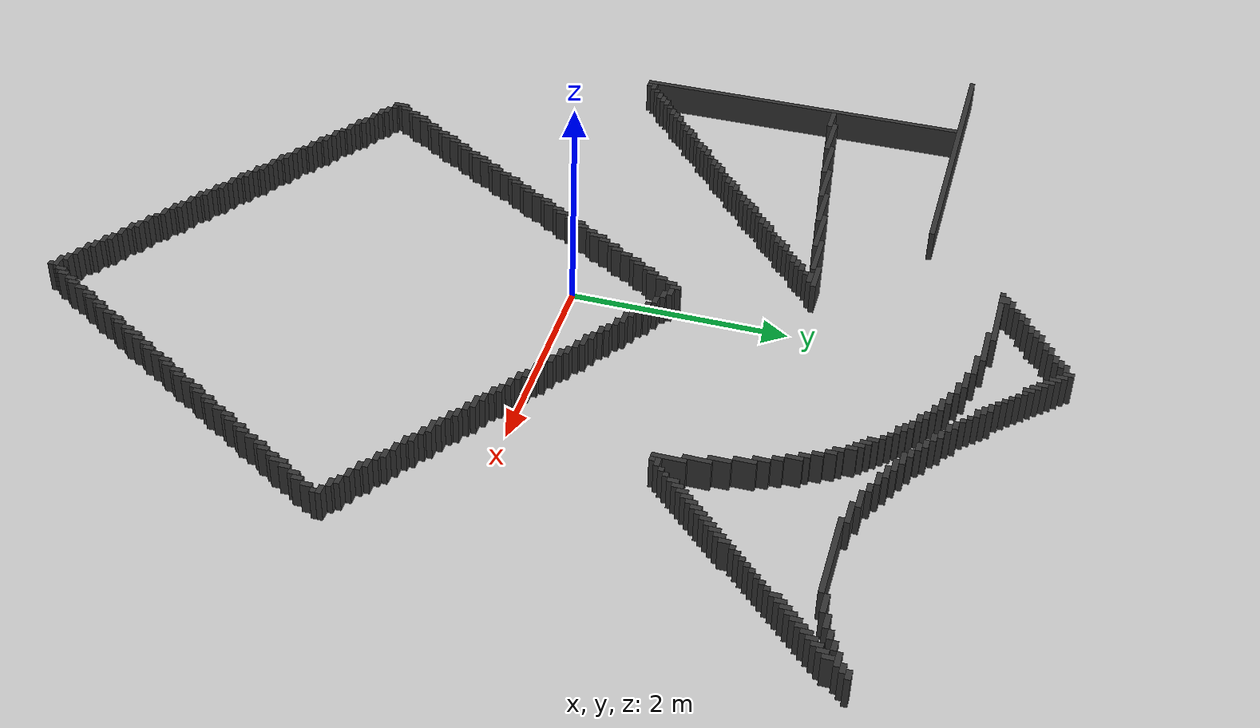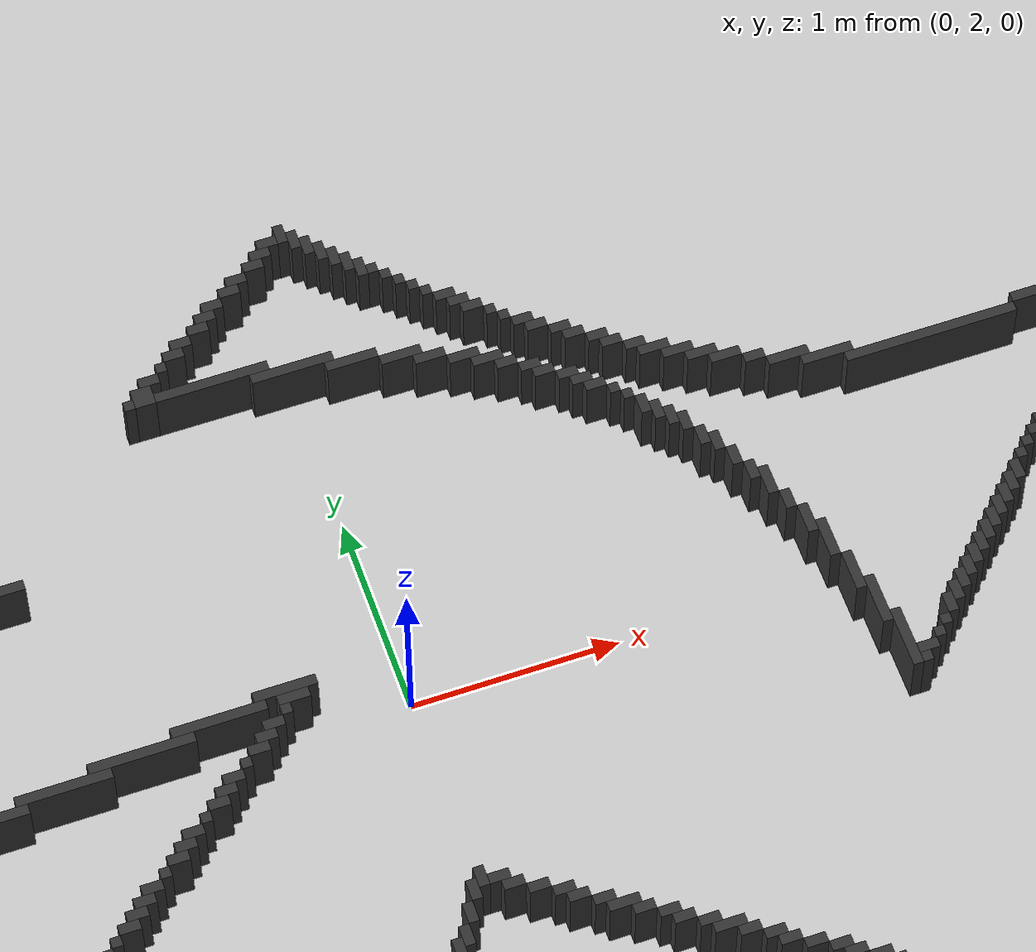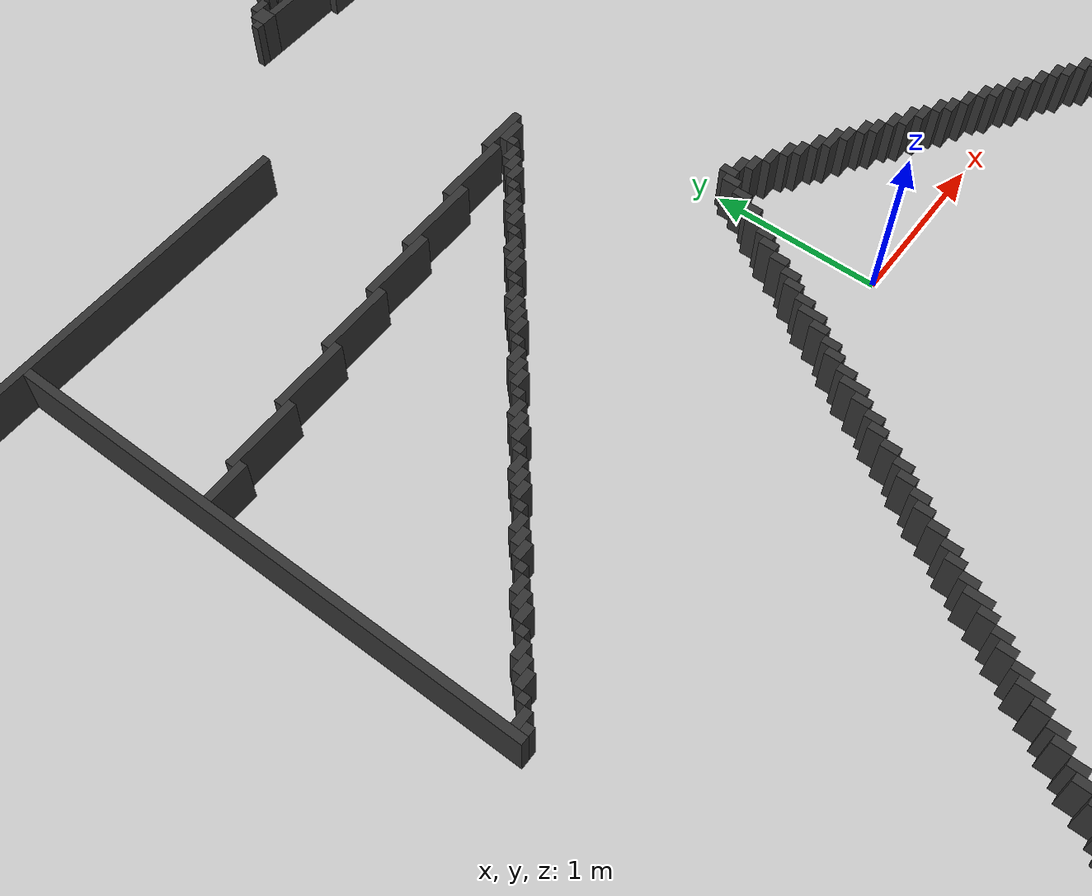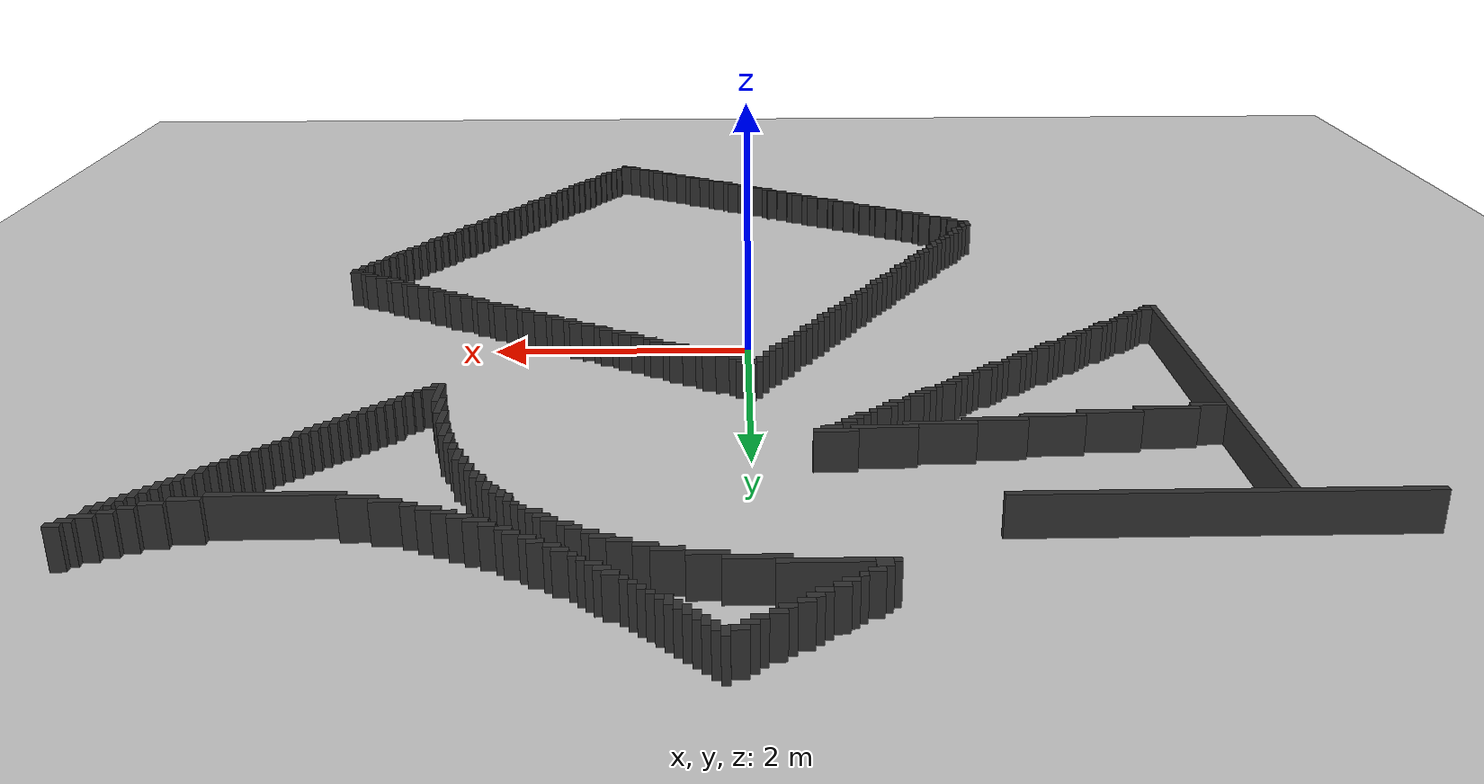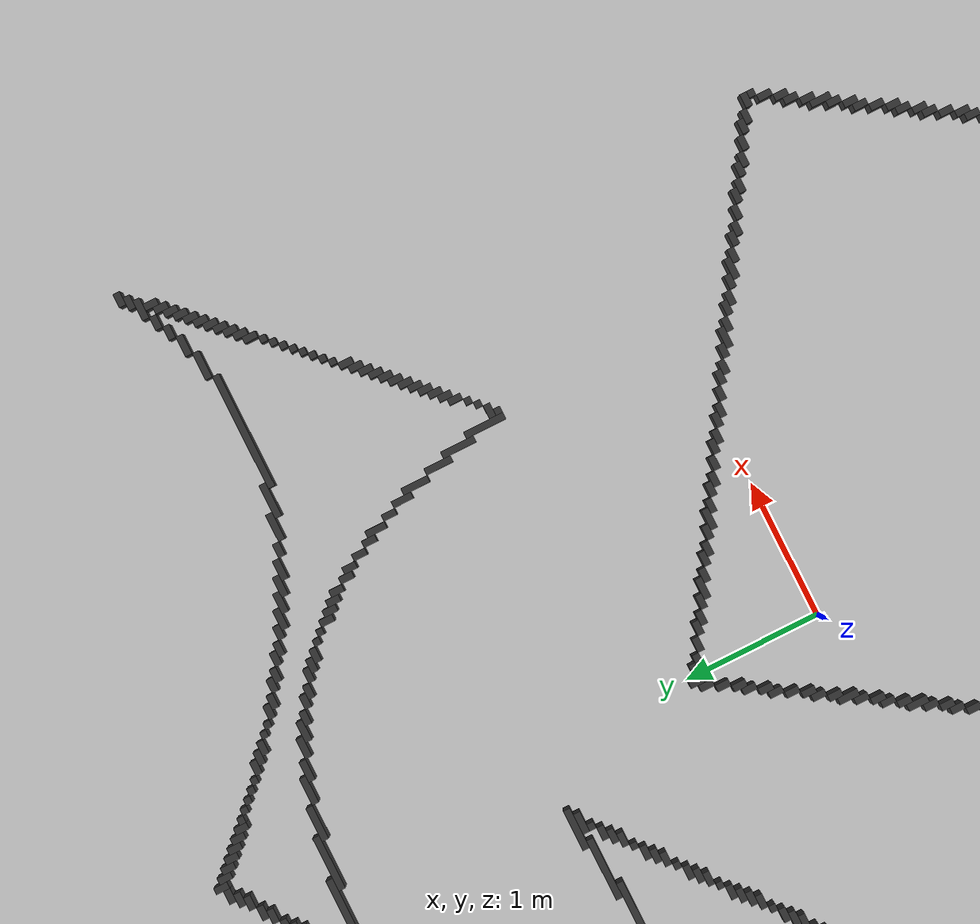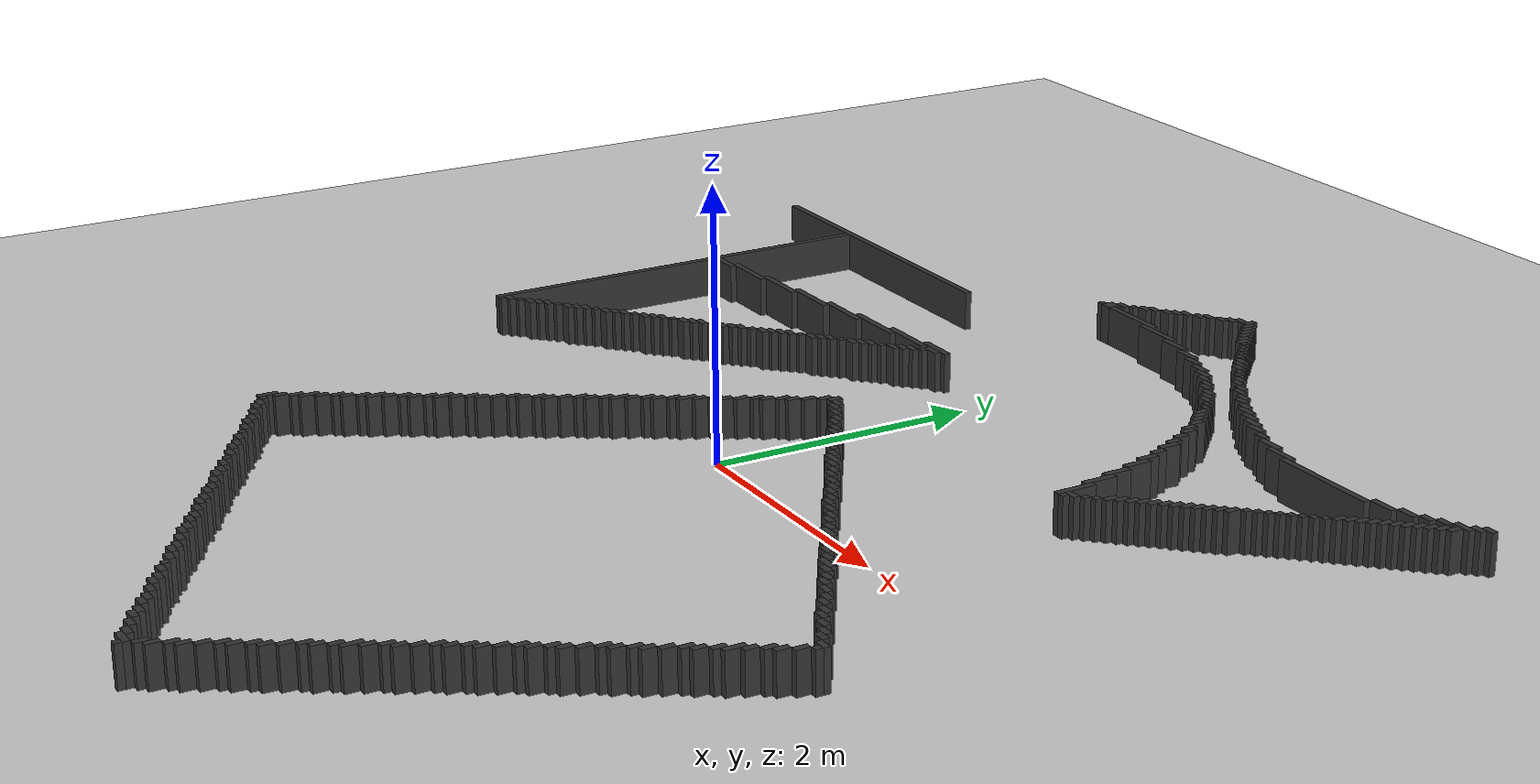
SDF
<?xml version="1.0" ?>
<sdf version="1.7">
  <world name="mapa_mundo">

    <plugin
      filename="gz-sim-physics-system"
      name="gz::sim::systems::Physics">
    </plugin>
    <plugin
      filename="gz-sim-user-commands-system"
      name="gz::sim::systems::UserCommands">
    </plugin>
    <plugin
      filename="gz-sim-scene-broadcaster-system"
      name="gz::sim::systems::SceneBroadcaster">
    </plugin>
    <plugin
      filename="gz-sim-sensors-system"
      name="gz::sim::systems::Sensors">
      <render_engine>ogre2</render_engine>
    </plugin>
    <plugin
      filename="gz-sim-imu-system"
      name="gz::sim::systems::Imu">
    </plugin>

    <!-- Luz direcional (sol) -->
    <light name='sun' type='directional'>
      <cast_shadows>true</cast_shadows>
      <pose>0 0 10 0 -0 0</pose>
      <diffuse>0.8 0.8 0.8 1</diffuse>
      <specular>0.2 0.2 0.2 1</specular>
      <direction>-0.5 0.1 -0.9</direction>
    </light>

    <!-- Plano de chão com o tamanho exato da imagem -->
    <model name='ground_plane'>
      <static>true</static>
      <link name='link'>
        <collision name='collision'>
          <geometry>
            <plane>
              <normal>0 0 1</normal>
              <size>10 10</size>
            </plane>
          </geometry>
          <surface>
            <friction>
              <ode>
                <mu>100</mu>
                <mu2>50</mu2>
              </ode>
            </friction>
          </surface>
        </collision>
        <visual name='visual'>
          <geometry>
            <plane>
              <normal>0 0 1</normal>
              <size>10 10</size>
            </plane>
          </geometry>
          <material>
            <ambient>0.8 0.8 0.8 1</ambient>
            <diffuse>0.8 0.8 0.8 1</diffuse>
            <specular>0.8 0.8 0.8 1</specular>
          </material>
        </visual>
      </link>
    </model>

    <!-- Modelos das paredes gerados a partir da imagem -->

    <model name="wall_0">
      <static>true</static>
      <link name="link">
        <collision name="collision">
          <geometry>
            <box>
              <size>0.05 0.1 0.3</size>
            </box>
          </geometry>
        </collision>
        <visual name="visual">
          <geometry>
            <box>
              <size>0.05 0.1 0.3</size>
            </box>
          </geometry>
          <material>
            <ambient>0.2 0.2 0.2 1</ambient>
            <diffuse>0.2 0.2 0.2 1</diffuse>
          </material>
        </visual>
        <pose>0.17500000000000002 4.45 0.15 0 0 0</pose>
      </link>
    </model>
    <model name="wall_1">
      <static>true</static>
      <link name="link">
        <collision name="collision">
          <geometry>
            <box>
              <size>0.1 0.05 0.3</size>
            </box>
          </geometry>
        </collision>
        <visual name="visual">
          <geometry>
            <box>
              <size>0.1 0.05 0.3</size>
            </box>
          </geometry>
          <material>
            <ambient>0.2 0.2 0.2 1</ambient>
            <diffuse>0.2 0.2 0.2 1</diffuse>
          </material>
        </visual>
        <pose>0.1 4.425 0.15 0 0 0</pose>
      </link>
    </model>
    <model name="wall_2">
      <static>true</static>
      <link name="link">
        <collision name="collision">
          <geometry>
            <box>
              <size>0.05 0.1 0.3</size>
            </box>
          </geometry>
        </collision>
        <visual name="visual">
          <geometry>
            <box>
              <size>0.05 0.1 0.3</size>
            </box>
          </geometry>
          <material>
            <ambient>0.2 0.2 0.2 1</ambient>
            <diffuse>0.2 0.2 0.2 1</diffuse>
          </material>
        </visual>
        <pose>0.225 4.4 0.15 0 0 0</pose>
      </link>
    </model>
    <model name="wall_3">
      <static>true</static>
      <link name="link">
        <collision name="collision">
          <geometry>
            <box>
              <size>0.1 0.05 0.3</size>
            </box>
          </geometry>
        </collision>
        <visual name="visual">
          <geometry>
            <box>
              <size>0.1 0.05 0.3</size>
            </box>
          </geometry>
          <material>
            <ambient>0.2 0.2 0.2 1</ambient>
            <diffuse>0.2 0.2 0.2 1</diffuse>
          </material>
        </visual>
        <pose>0.05 4.375 0.15 0 0 0</pose>
      </link>
    </model>
    <model name="wall_4">
      <static>true</static>
      <link name="link">
        <collision name="collision">
          <geometry>
            <box>
              <size>0.05 0.1 0.3</size>
            </box>
          </geometry>
        </collision>
        <visual name="visual">
          <geometry>
            <box>
              <size>0.05 0.1 0.3</size>
            </box>
          </geometry>
          <material>
            <ambient>0.2 0.2 0.2 1</ambient>
            <diffuse>0.2 0.2 0.2 1</diffuse>
          </material>
        </visual>
        <pose>0.275 4.3500000000000005 0.15 0 0 0</pose>
      </link>
    </model>
    <model name="wall_5">
      <static>true</static>
      <link name="link">
        <collision name="collision">
          <geometry>
            <box>
              <size>0.1 0.05 0.3</size>
            </box>
          </geometry>
        </collision>
        <visual name="visual">
          <geometry>
            <box>
              <size>0.1 0.05 0.3</size>
            </box>
          </geometry>
          <material>
            <ambient>0.2 0.2 0.2 1</ambient>
            <diffuse>0.2 0.2 0.2 1</diffuse>
          </material>
        </visual>
        <pose>0.0 4.325 0.15 0 0 0</pose>
      </link>
    </model>
    <model name="wall_6">
      <static>true</static>
      <link name="link">
        <collision name="collision">
          <geometry>
            <box>
              <size>0.05 0.1 0.3</size>
            </box>
          </geometry>
        </collision>
        <visual name="visual">
          <geometry>
            <box>
              <size>0.05 0.1 0.3</size>
            </box>
          </geometry>
          <material>
            <ambient>0.2 0.2 0.2 1</ambient>
            <diffuse>0.2 0.2 0.2 1</diffuse>
          </material>
        </visual>
        <pose>0.325 4.3 0.15 0 0 0</pose>
      </link>
    </model>
    <model name="wall_7">
      <static>true</static>
      <link name="link">
        <collision name="collision">
          <geometry>
            <box>
              <size>0.1 0.05 0.3</size>
            </box>
          </geometry>
        </collision>
        <visual name="visual">
          <geometry>
            <box>
              <size>0.1 0.05 0.3</size>
            </box>
          </geometry>
          <material>
            <ambient>0.2 0.2 0.2 1</ambient>
            <diffuse>0.2 0.2 0.2 1</diffuse>
          </material>
        </visual>
        <pose>-0.1 4.275 0.15 0 0 0</pose>
      </link>
    </model>
    <model name="wall_8">
      <static>true</static>
      <link name="link">
        <collision name="collision">
          <geometry>
            <box>
              <size>0.05 0.1 0.3</size>
            </box>
          </geometry>
        </collision>
        <visual name="visual">
          <geometry>
            <box>
              <size>0.05 0.1 0.3</size>
            </box>
          </geometry>
          <material>
            <ambient>0.2 0.2 0.2 1</ambient>
            <diffuse>0.2 0.2 0.2 1</diffuse>
          </material>
        </visual>
        <pose>0.375 4.25 0.15 0 0 0</pose>
      </link>
    </model>
    <model name="wall_9">
      <static>true</static>
      <link name="link">
        <collision name="collision">
          <geometry>
            <box>
              <size>0.1 0.05 0.3</size>
            </box>
          </geometry>
        </collision>
        <visual name="visual">
          <geometry>
            <box>
              <size>0.1 0.05 0.3</size>
            </box>
          </geometry>
          <material>
            <ambient>0.2 0.2 0.2 1</ambient>
            <diffuse>0.2 0.2 0.2 1</diffuse>
          </material>
        </visual>
        <pose>-0.15000000000000002 4.2250000000000005 0.15 0 0 0</pose>
      </link>
    </model>
    <model name="wall_10">
      <static>true</static>
      <link name="link">
        <collision name="collision">
          <geometry>
            <box>
              <size>0.05 0.1 0.3</size>
            </box>
          </geometry>
        </collision>
        <visual name="visual">
          <geometry>
            <box>
              <size>0.05 0.1 0.3</size>
            </box>
          </geometry>
          <material>
            <ambient>0.2 0.2 0.2 1</ambient>
            <diffuse>0.2 0.2 0.2 1</diffuse>
          </material>
        </visual>
        <pose>0.42500000000000004 4.2 0.15 0 0 0</pose>
      </link>
    </model>
    <model name="wall_11">
      <static>true</static>
      <link name="link">
        <collision name="collision">
          <geometry>
            <box>
              <size>0.1 0.05 0.3</size>
            </box>
          </geometry>
        </collision>
        <visual name="visual">
          <geometry>
            <box>
              <size>0.1 0.05 0.3</size>
            </box>
          </geometry>
          <material>
            <ambient>0.2 0.2 0.2 1</ambient>
            <diffuse>0.2 0.2 0.2 1</diffuse>
          </material>
        </visual>
        <pose>-0.25 4.175 0.15 0 0 0</pose>
      </link>
    </model>
    <model name="wall_12">
      <static>true</static>
      <link name="link">
        <collision name="collision">
          <geometry>
            <box>
              <size>0.05 0.1 0.3</size>
            </box>
          </geometry>
        </collision>
        <visual name="visual">
          <geometry>
            <box>
              <size>0.05 0.1 0.3</size>
            </box>
          </geometry>
          <material>
            <ambient>0.2 0.2 0.2 1</ambient>
            <diffuse>0.2 0.2 0.2 1</diffuse>
          </material>
        </visual>
        <pose>0.47500000000000003 4.15 0.15 0 0 0</pose>
      </link>
    </model>
    <model name="wall_13">
      <static>true</static>
      <link name="link">
        <collision name="collision">
          <geometry>
            <box>
              <size>0.1 0.05 0.3</size>
            </box>
          </geometry>
        </collision>
        <visual name="visual">
          <geometry>
            <box>
              <size>0.1 0.05 0.3</size>
            </box>
          </geometry>
          <material>
            <ambient>0.2 0.2 0.2 1</ambient>
            <diffuse>0.2 0.2 0.2 1</diffuse>
          </material>
        </visual>
        <pose>-0.30000000000000004 4.125 0.15 0 0 0</pose>
      </link>
    </model>
    <model name="wall_14">
      <static>true</static>
      <link name="link">
        <collision name="collision">
          <geometry>
            <box>
              <size>0.05 0.05 0.3</size>
            </box>
          </geometry>
        </collision>
        <visual name="visual">
          <geometry>
            <box>
              <size>0.05 0.05 0.3</size>
            </box>
          </geometry>
          <material>
            <ambient>0.2 0.2 0.2 1</ambient>
            <diffuse>0.2 0.2 0.2 1</diffuse>
          </material>
        </visual>
        <pose>0.525 4.125 0.15 0 0 0</pose>
      </link>
    </model>
    <model name="wall_15">
      <static>true</static>
      <link name="link">
        <collision name="collision">
          <geometry>
            <box>
              <size>0.1 0.05 0.3</size>
            </box>
          </geometry>
        </collision>
        <visual name="visual">
          <geometry>
            <box>
              <size>0.1 0.05 0.3</size>
            </box>
          </geometry>
          <material>
            <ambient>0.2 0.2 0.2 1</ambient>
            <diffuse>0.2 0.2 0.2 1</diffuse>
          </material>
        </visual>
        <pose>-0.35000000000000003 4.075 0.15 0 0 0</pose>
      </link>
    </model>
    <model name="wall_16">
      <static>true</static>
      <link name="link">
        <collision name="collision">
          <geometry>
            <box>
              <size>0.05 0.05 0.3</size>
            </box>
          </geometry>
        </collision>
        <visual name="visual">
          <geometry>
            <box>
              <size>0.05 0.05 0.3</size>
            </box>
          </geometry>
          <material>
            <ambient>0.2 0.2 0.2 1</ambient>
            <diffuse>0.2 0.2 0.2 1</diffuse>
          </material>
        </visual>
        <pose>0.5750000000000001 4.075 0.15 0 0 0</pose>
      </link>
    </model>
    <model name="wall_17">
      <static>true</static>
      <link name="link">
        <collision name="collision">
          <geometry>
            <box>
              <size>0.1 0.05 0.3</size>
            </box>
          </geometry>
        </collision>
        <visual name="visual">
          <geometry>
            <box>
              <size>0.1 0.05 0.3</size>
            </box>
          </geometry>
          <material>
            <ambient>0.2 0.2 0.2 1</ambient>
            <diffuse>0.2 0.2 0.2 1</diffuse>
          </material>
        </visual>
        <pose>-0.45 4.025 0.15 0 0 0</pose>
      </link>
    </model>
    <model name="wall_18">
      <static>true</static>
      <link name="link">
        <collision name="collision">
          <geometry>
            <box>
              <size>0.05 0.05 0.3</size>
            </box>
          </geometry>
        </collision>
        <visual name="visual">
          <geometry>
            <box>
              <size>0.05 0.05 0.3</size>
            </box>
          </geometry>
          <material>
            <ambient>0.2 0.2 0.2 1</ambient>
            <diffuse>0.2 0.2 0.2 1</diffuse>
          </material>
        </visual>
        <pose>0.625 4.025 0.15 0 0 0</pose>
      </link>
    </model>
    <model name="wall_19">
      <static>true</static>
      <link name="link">
        <collision name="collision">
          <geometry>
            <box>
              <size>0.1 0.05 0.3</size>
            </box>
          </geometry>
        </collision>
        <visual name="visual">
          <geometry>
            <box>
              <size>0.1 0.05 0.3</size>
            </box>
          </geometry>
          <material>
            <ambient>0.2 0.2 0.2 1</ambient>
            <diffuse>0.2 0.2 0.2 1</diffuse>
          </material>
        </visual>
        <pose>-0.5 3.975 0.15 0 0 0</pose>
      </link>
    </model>
    <model name="wall_20">
      <static>true</static>
      <link name="link">
        <collision name="collision">
          <geometry>
            <box>
              <size>0.05 0.05 0.3</size>
            </box>
          </geometry>
        </collision>
        <visual name="visual">
          <geometry>
            <box>
              <size>0.05 0.05 0.3</size>
            </box>
          </geometry>
          <material>
            <ambient>0.2 0.2 0.2 1</ambient>
            <diffuse>0.2 0.2 0.2 1</diffuse>
          </material>
        </visual>
        <pose>0.675 3.975 0.15 0 0 0</pose>
      </link>
    </model>
    <model name="wall_21">
      <static>true</static>
      <link name="link">
        <collision name="collision">
          <geometry>
            <box>
              <size>0.05 0.05 0.3</size>
            </box>
          </geometry>
        </collision>
        <visual name="visual">
          <geometry>
            <box>
              <size>0.05 0.05 0.3</size>
            </box>
          </geometry>
          <material>
            <ambient>0.2 0.2 0.2 1</ambient>
            <diffuse>0.2 0.2 0.2 1</diffuse>
          </material>
        </visual>
        <pose>-0.5750000000000001 3.9250000000000003 0.15 0 0 0</pose>
      </link>
    </model>
    <model name="wall_22">
      <static>true</static>
      <link name="link">
        <collision name="collision">
          <geometry>
            <box>
              <size>0.05 0.05 0.3</size>
            </box>
          </geometry>
        </collision>
        <visual name="visual">
          <geometry>
            <box>
              <size>0.05 0.05 0.3</size>
            </box>
          </geometry>
          <material>
            <ambient>0.2 0.2 0.2 1</ambient>
            <diffuse>0.2 0.2 0.2 1</diffuse>
          </material>
        </visual>
        <pose>0.7250000000000001 3.9250000000000003 0.15 0 0 0</pose>
      </link>
    </model>
    <model name="wall_23">
      <static>true</static>
      <link name="link">
        <collision name="collision">
          <geometry>
            <box>
              <size>0.1 0.05 0.3</size>
            </box>
          </geometry>
        </collision>
        <visual name="visual">
          <geometry>
            <box>
              <size>0.1 0.05 0.3</size>
            </box>
          </geometry>
          <material>
            <ambient>0.2 0.2 0.2 1</ambient>
            <diffuse>0.2 0.2 0.2 1</diffuse>
          </material>
        </visual>
        <pose>-0.65 3.875 0.15 0 0 0</pose>
      </link>
    </model>
    <model name="wall_24">
      <static>true</static>
      <link name="link">
        <collision name="collision">
          <geometry>
            <box>
              <size>0.1 0.05 0.3</size>
            </box>
          </geometry>
        </collision>
        <visual name="visual">
          <geometry>
            <box>
              <size>0.1 0.05 0.3</size>
            </box>
          </geometry>
          <material>
            <ambient>0.2 0.2 0.2 1</ambient>
            <diffuse>0.2 0.2 0.2 1</diffuse>
          </material>
        </visual>
        <pose>0.8 3.875 0.15 0 0 0</pose>
      </link>
    </model>
    <model name="wall_25">
      <static>true</static>
      <link name="link">
        <collision name="collision">
          <geometry>
            <box>
              <size>0.1 0.1 0.3</size>
            </box>
          </geometry>
        </collision>
        <visual name="visual">
          <geometry>
            <box>
              <size>0.1 0.1 0.3</size>
            </box>
          </geometry>
          <material>
            <ambient>0.2 0.2 0.2 1</ambient>
            <diffuse>0.2 0.2 0.2 1</diffuse>
          </material>
        </visual>
        <pose>-0.7000000000000001 3.8000000000000003 0.15 0 0 0</pose>
      </link>
    </model>
    <model name="wall_26">
      <static>true</static>
      <link name="link">
        <collision name="collision">
          <geometry>
            <box>
              <size>0.1 0.05 0.3</size>
            </box>
          </geometry>
        </collision>
        <visual name="visual">
          <geometry>
            <box>
              <size>0.1 0.05 0.3</size>
            </box>
          </geometry>
          <material>
            <ambient>0.2 0.2 0.2 1</ambient>
            <diffuse>0.2 0.2 0.2 1</diffuse>
          </material>
        </visual>
        <pose>0.8500000000000001 3.825 0.15 0 0 0</pose>
      </link>
    </model>
    <model name="wall_27">
      <static>true</static>
      <link name="link">
        <collision name="collision">
          <geometry>
            <box>
              <size>0.05 0.05 0.3</size>
            </box>
          </geometry>
        </collision>
        <visual name="visual">
          <geometry>
            <box>
              <size>0.05 0.05 0.3</size>
            </box>
          </geometry>
          <material>
            <ambient>0.2 0.2 0.2 1</ambient>
            <diffuse>0.2 0.2 0.2 1</diffuse>
          </material>
        </visual>
        <pose>-0.775 3.7750000000000004 0.15 0 0 0</pose>
      </link>
    </model>
    <model name="wall_28">
      <static>true</static>
      <link name="link">
        <collision name="collision">
          <geometry>
            <box>
              <size>0.55 0.05 0.3</size>
            </box>
          </geometry>
        </collision>
        <visual name="visual">
          <geometry>
            <box>
              <size>0.55 0.05 0.3</size>
            </box>
          </geometry>
          <material>
            <ambient>0.2 0.2 0.2 1</ambient>
            <diffuse>0.2 0.2 0.2 1</diffuse>
          </material>
        </visual>
        <pose>-0.375 3.7750000000000004 0.15 0 0 0</pose>
      </link>
    </model>
    <model name="wall_29">
      <static>true</static>
      <link name="link">
        <collision name="collision">
          <geometry>
            <box>
              <size>0.1 0.05 0.3</size>
            </box>
          </geometry>
        </collision>
        <visual name="visual">
          <geometry>
            <box>
              <size>0.1 0.05 0.3</size>
            </box>
          </geometry>
          <material>
            <ambient>0.2 0.2 0.2 1</ambient>
            <diffuse>0.2 0.2 0.2 1</diffuse>
          </material>
        </visual>
        <pose>0.9 3.7750000000000004 0.15 0 0 0</pose>
      </link>
    </model>
    <model name="wall_30">
      <static>true</static>
      <link name="link">
        <collision name="collision">
          <geometry>
            <box>
              <size>0.4 0.05 0.3</size>
            </box>
          </geometry>
        </collision>
        <visual name="visual">
          <geometry>
            <box>
              <size>0.4 0.05 0.3</size>
            </box>
          </geometry>
          <material>
            <ambient>0.2 0.2 0.2 1</ambient>
            <diffuse>0.2 0.2 0.2 1</diffuse>
          </material>
        </visual>
        <pose>0.0 3.725 0.15 0 0 0</pose>
      </link>
    </model>
    <model name="wall_31">
      <static>true</static>
      <link name="link">
        <collision name="collision">
          <geometry>
            <box>
              <size>0.05 0.05 0.3</size>
            </box>
          </geometry>
        </collision>
        <visual name="visual">
          <geometry>
            <box>
              <size>0.05 0.05 0.3</size>
            </box>
          </geometry>
          <material>
            <ambient>0.2 0.2 0.2 1</ambient>
            <diffuse>0.2 0.2 0.2 1</diffuse>
          </material>
        </visual>
        <pose>0.9750000000000001 3.725 0.15 0 0 0</pose>
      </link>
    </model>
    <model name="wall_32">
      <static>true</static>
      <link name="link">
        <collision name="collision">
          <geometry>
            <box>
              <size>0.25 0.05 0.3</size>
            </box>
          </geometry>
        </collision>
        <visual name="visual">
          <geometry>
            <box>
              <size>0.25 0.05 0.3</size>
            </box>
          </geometry>
          <material>
            <ambient>0.2 0.2 0.2 1</ambient>
            <diffuse>0.2 0.2 0.2 1</diffuse>
          </material>
        </visual>
        <pose>0.275 3.6750000000000003 0.15 0 0 0</pose>
      </link>
    </model>
    <model name="wall_33">
      <static>true</static>
      <link name="link">
        <collision name="collision">
          <geometry>
            <box>
              <size>0.05 0.05 0.3</size>
            </box>
          </geometry>
        </collision>
        <visual name="visual">
          <geometry>
            <box>
              <size>0.05 0.05 0.3</size>
            </box>
          </geometry>
          <material>
            <ambient>0.2 0.2 0.2 1</ambient>
            <diffuse>0.2 0.2 0.2 1</diffuse>
          </material>
        </visual>
        <pose>1.0250000000000001 3.6750000000000003 0.15 0 0 0</pose>
      </link>
    </model>
    <model name="wall_34">
      <static>true</static>
      <link name="link">
        <collision name="collision">
          <geometry>
            <box>
              <size>0.2 0.05 0.3</size>
            </box>
          </geometry>
        </collision>
        <visual name="visual">
          <geometry>
            <box>
              <size>0.2 0.05 0.3</size>
            </box>
          </geometry>
          <material>
            <ambient>0.2 0.2 0.2 1</ambient>
            <diffuse>0.2 0.2 0.2 1</diffuse>
          </material>
        </visual>
        <pose>0.5 3.625 0.15 0 0 0</pose>
      </link>
    </model>
    <model name="wall_35">
      <static>true</static>
      <link name="link">
        <collision name="collision">
          <geometry>
            <box>
              <size>0.1 0.05 0.3</size>
            </box>
          </geometry>
        </collision>
        <visual name="visual">
          <geometry>
            <box>
              <size>0.1 0.05 0.3</size>
            </box>
          </geometry>
          <material>
            <ambient>0.2 0.2 0.2 1</ambient>
            <diffuse>0.2 0.2 0.2 1</diffuse>
          </material>
        </visual>
        <pose>1.1 3.625 0.15 0 0 0</pose>
      </link>
    </model>
    <model name="wall_36">
      <static>true</static>
      <link name="link">
        <collision name="collision">
          <geometry>
            <box>
              <size>0.15000000000000002 0.05 0.3</size>
            </box>
          </geometry>
        </collision>
        <visual name="visual">
          <geometry>
            <box>
              <size>0.15000000000000002 0.05 0.3</size>
            </box>
          </geometry>
          <material>
            <ambient>0.2 0.2 0.2 1</ambient>
            <diffuse>0.2 0.2 0.2 1</diffuse>
          </material>
        </visual>
        <pose>0.625 3.575 0.15 0 0 0</pose>
      </link>
    </model>
    <model name="wall_37">
      <static>true</static>
      <link name="link">
        <collision name="collision">
          <geometry>
            <box>
              <size>0.1 0.05 0.3</size>
            </box>
          </geometry>
        </collision>
        <visual name="visual">
          <geometry>
            <box>
              <size>0.1 0.05 0.3</size>
            </box>
          </geometry>
          <material>
            <ambient>0.2 0.2 0.2 1</ambient>
            <diffuse>0.2 0.2 0.2 1</diffuse>
          </material>
        </visual>
        <pose>1.1500000000000001 3.575 0.15 0 0 0</pose>
      </link>
    </model>
    <model name="wall_38">
      <static>true</static>
      <link name="link">
        <collision name="collision">
          <geometry>
            <box>
              <size>0.15000000000000002 0.05 0.3</size>
            </box>
          </geometry>
        </collision>
        <visual name="visual">
          <geometry>
            <box>
              <size>0.15000000000000002 0.05 0.3</size>
            </box>
          </geometry>
          <material>
            <ambient>0.2 0.2 0.2 1</ambient>
            <diffuse>0.2 0.2 0.2 1</diffuse>
          </material>
        </visual>
        <pose>0.775 3.5250000000000004 0.15 0 0 0</pose>
      </link>
    </model>
    <model name="wall_39">
      <static>true</static>
      <link name="link">
        <collision name="collision">
          <geometry>
            <box>
              <size>0.1 0.05 0.3</size>
            </box>
          </geometry>
        </collision>
        <visual name="visual">
          <geometry>
            <box>
              <size>0.1 0.05 0.3</size>
            </box>
          </geometry>
          <material>
            <ambient>0.2 0.2 0.2 1</ambient>
            <diffuse>0.2 0.2 0.2 1</diffuse>
          </material>
        </visual>
        <pose>1.25 3.5250000000000004 0.15 0 0 0</pose>
      </link>
    </model>
    <model name="wall_40">
      <static>true</static>
      <link name="link">
        <collision name="collision">
          <geometry>
            <box>
              <size>0.15000000000000002 0.05 0.3</size>
            </box>
          </geometry>
        </collision>
        <visual name="visual">
          <geometry>
            <box>
              <size>0.15000000000000002 0.05 0.3</size>
            </box>
          </geometry>
          <material>
            <ambient>0.2 0.2 0.2 1</ambient>
            <diffuse>0.2 0.2 0.2 1</diffuse>
          </material>
        </visual>
        <pose>0.875 3.475 0.15 0 0 0</pose>
      </link>
    </model>
    <model name="wall_41">
      <static>true</static>
      <link name="link">
        <collision name="collision">
          <geometry>
            <box>
              <size>0.1 0.05 0.3</size>
            </box>
          </geometry>
        </collision>
        <visual name="visual">
          <geometry>
            <box>
              <size>0.1 0.05 0.3</size>
            </box>
          </geometry>
          <material>
            <ambient>0.2 0.2 0.2 1</ambient>
            <diffuse>0.2 0.2 0.2 1</diffuse>
          </material>
        </visual>
        <pose>1.3 3.475 0.15 0 0 0</pose>
      </link>
    </model>
    <model name="wall_42">
      <static>true</static>
      <link name="link">
        <collision name="collision">
          <geometry>
            <box>
              <size>0.1 0.05 0.3</size>
            </box>
          </geometry>
        </collision>
        <visual name="visual">
          <geometry>
            <box>
              <size>0.1 0.05 0.3</size>
            </box>
          </geometry>
          <material>
            <ambient>0.2 0.2 0.2 1</ambient>
            <diffuse>0.2 0.2 0.2 1</diffuse>
          </material>
        </visual>
        <pose>0.9500000000000001 3.4250000000000003 0.15 0 0 0</pose>
      </link>
    </model>
    <model name="wall_43">
      <static>true</static>
      <link name="link">
        <collision name="collision">
          <geometry>
            <box>
              <size>0.1 0.05 0.3</size>
            </box>
          </geometry>
        </collision>
        <visual name="visual">
          <geometry>
            <box>
              <size>0.1 0.05 0.3</size>
            </box>
          </geometry>
          <material>
            <ambient>0.2 0.2 0.2 1</ambient>
            <diffuse>0.2 0.2 0.2 1</diffuse>
          </material>
        </visual>
        <pose>1.4000000000000001 3.4250000000000003 0.15 0 0 0</pose>
      </link>
    </model>
    <model name="wall_44">
      <static>true</static>
      <link name="link">
        <collision name="collision">
          <geometry>
            <box>
              <size>0.1 0.05 0.3</size>
            </box>
          </geometry>
        </collision>
        <visual name="visual">
          <geometry>
            <box>
              <size>0.1 0.05 0.3</size>
            </box>
          </geometry>
          <material>
            <ambient>0.2 0.2 0.2 1</ambient>
            <diffuse>0.2 0.2 0.2 1</diffuse>
          </material>
        </visual>
        <pose>1.05 3.375 0.15 0 0 0</pose>
      </link>
    </model>
    <model name="wall_45">
      <static>true</static>
      <link name="link">
        <collision name="collision">
          <geometry>
            <box>
              <size>0.1 0.05 0.3</size>
            </box>
          </geometry>
        </collision>
        <visual name="visual">
          <geometry>
            <box>
              <size>0.1 0.05 0.3</size>
            </box>
          </geometry>
          <material>
            <ambient>0.2 0.2 0.2 1</ambient>
            <diffuse>0.2 0.2 0.2 1</diffuse>
          </material>
        </visual>
        <pose>1.4500000000000002 3.375 0.15 0 0 0</pose>
      </link>
    </model>
    <model name="wall_46">
      <static>true</static>
      <link name="link">
        <collision name="collision">
          <geometry>
            <box>
              <size>0.1 0.05 0.3</size>
            </box>
          </geometry>
        </collision>
        <visual name="visual">
          <geometry>
            <box>
              <size>0.1 0.05 0.3</size>
            </box>
          </geometry>
          <material>
            <ambient>0.2 0.2 0.2 1</ambient>
            <diffuse>0.2 0.2 0.2 1</diffuse>
          </material>
        </visual>
        <pose>1.1 3.325 0.15 0 0 0</pose>
      </link>
    </model>
    <model name="wall_47">
      <static>true</static>
      <link name="link">
        <collision name="collision">
          <geometry>
            <box>
              <size>0.1 0.05 0.3</size>
            </box>
          </geometry>
        </collision>
        <visual name="visual">
          <geometry>
            <box>
              <size>0.1 0.05 0.3</size>
            </box>
          </geometry>
          <material>
            <ambient>0.2 0.2 0.2 1</ambient>
            <diffuse>0.2 0.2 0.2 1</diffuse>
          </material>
        </visual>
        <pose>1.55 3.325 0.15 0 0 0</pose>
      </link>
    </model>
    <model name="wall_48">
      <static>true</static>
      <link name="link">
        <collision name="collision">
          <geometry>
            <box>
              <size>0.1 0.05 0.3</size>
            </box>
          </geometry>
        </collision>
        <visual name="visual">
          <geometry>
            <box>
              <size>0.1 0.05 0.3</size>
            </box>
          </geometry>
          <material>
            <ambient>0.2 0.2 0.2 1</ambient>
            <diffuse>0.2 0.2 0.2 1</diffuse>
          </material>
        </visual>
        <pose>1.2000000000000002 3.2750000000000004 0.15 0 0 0</pose>
      </link>
    </model>
    <model name="wall_49">
      <static>true</static>
      <link name="link">
        <collision name="collision">
          <geometry>
            <box>
              <size>0.15000000000000002 0.05 0.3</size>
            </box>
          </geometry>
        </collision>
        <visual name="visual">
          <geometry>
            <box>
              <size>0.15000000000000002 0.05 0.3</size>
            </box>
          </geometry>
          <material>
            <ambient>0.2 0.2 0.2 1</ambient>
            <diffuse>0.2 0.2 0.2 1</diffuse>
          </material>
        </visual>
        <pose>1.625 3.2750000000000004 0.15 0 0 0</pose>
      </link>
    </model>
    <model name="wall_50">
      <static>true</static>
      <link name="link">
        <collision name="collision">
          <geometry>
            <box>
              <size>0.1 0.05 0.3</size>
            </box>
          </geometry>
        </collision>
        <visual name="visual">
          <geometry>
            <box>
              <size>0.1 0.05 0.3</size>
            </box>
          </geometry>
          <material>
            <ambient>0.2 0.2 0.2 1</ambient>
            <diffuse>0.2 0.2 0.2 1</diffuse>
          </material>
        </visual>
        <pose>4.05 3.2750000000000004 0.15 0 0 0</pose>
      </link>
    </model>
    <model name="wall_51">
      <static>true</static>
      <link name="link">
        <collision name="collision">
          <geometry>
            <box>
              <size>0.1 0.05 0.3</size>
            </box>
          </geometry>
        </collision>
        <visual name="visual">
          <geometry>
            <box>
              <size>0.1 0.05 0.3</size>
            </box>
          </geometry>
          <material>
            <ambient>0.2 0.2 0.2 1</ambient>
            <diffuse>0.2 0.2 0.2 1</diffuse>
          </material>
        </visual>
        <pose>1.25 3.225 0.15 0 0 0</pose>
      </link>
    </model>
    <model name="wall_52">
      <static>true</static>
      <link name="link">
        <collision name="collision">
          <geometry>
            <box>
              <size>0.15000000000000002 0.05 0.3</size>
            </box>
          </geometry>
        </collision>
        <visual name="visual">
          <geometry>
            <box>
              <size>0.15000000000000002 0.05 0.3</size>
            </box>
          </geometry>
          <material>
            <ambient>0.2 0.2 0.2 1</ambient>
            <diffuse>0.2 0.2 0.2 1</diffuse>
          </material>
        </visual>
        <pose>1.725 3.225 0.15 0 0 0</pose>
      </link>
    </model>
    <model name="wall_53">
      <static>true</static>
      <link name="link">
        <collision name="collision">
          <geometry>
            <box>
              <size>0.1 0.05 0.3</size>
            </box>
          </geometry>
        </collision>
        <visual name="visual">
          <geometry>
            <box>
              <size>0.1 0.05 0.3</size>
            </box>
          </geometry>
          <material>
            <ambient>0.2 0.2 0.2 1</ambient>
            <diffuse>0.2 0.2 0.2 1</diffuse>
          </material>
        </visual>
        <pose>4.0 3.225 0.15 0 0 0</pose>
      </link>
    </model>
    <model name="wall_54">
      <static>true</static>
      <link name="link">
        <collision name="collision">
          <geometry>
            <box>
              <size>0.1 0.05 0.3</size>
            </box>
          </geometry>
        </collision>
        <visual name="visual">
          <geometry>
            <box>
              <size>0.1 0.05 0.3</size>
            </box>
          </geometry>
          <material>
            <ambient>0.2 0.2 0.2 1</ambient>
            <diffuse>0.2 0.2 0.2 1</diffuse>
          </material>
        </visual>
        <pose>1.3 3.1750000000000003 0.15 0 0 0</pose>
      </link>
    </model>
    <model name="wall_55">
      <static>true</static>
      <link name="link">
        <collision name="collision">
          <geometry>
            <box>
              <size>0.15000000000000002 0.05 0.3</size>
            </box>
          </geometry>
        </collision>
        <visual name="visual">
          <geometry>
            <box>
              <size>0.15000000000000002 0.05 0.3</size>
            </box>
          </geometry>
          <material>
            <ambient>0.2 0.2 0.2 1</ambient>
            <diffuse>0.2 0.2 0.2 1</diffuse>
          </material>
        </visual>
        <pose>1.8250000000000002 3.1750000000000003 0.15 0 0 0</pose>
      </link>
    </model>
    <model name="wall_56">
      <static>true</static>
      <link name="link">
        <collision name="collision">
          <geometry>
            <box>
              <size>0.15000000000000002 0.05 0.3</size>
            </box>
          </geometry>
        </collision>
        <visual name="visual">
          <geometry>
            <box>
              <size>0.15000000000000002 0.05 0.3</size>
            </box>
          </geometry>
          <material>
            <ambient>0.2 0.2 0.2 1</ambient>
            <diffuse>0.2 0.2 0.2 1</diffuse>
          </material>
        </visual>
        <pose>3.9250000000000003 3.1750000000000003 0.15 0 0 0</pose>
      </link>
    </model>
    <model name="wall_57">
      <static>true</static>
      <link name="link">
        <collision name="collision">
          <geometry>
            <box>
              <size>0.05 0.05 0.3</size>
            </box>
          </geometry>
        </collision>
        <visual name="visual">
          <geometry>
            <box>
              <size>0.05 0.05 0.3</size>
            </box>
          </geometry>
          <material>
            <ambient>0.2 0.2 0.2 1</ambient>
            <diffuse>0.2 0.2 0.2 1</diffuse>
          </material>
        </visual>
        <pose>1.375 3.125 0.15 0 0 0</pose>
      </link>
    </model>
    <model name="wall_58">
      <static>true</static>
      <link name="link">
        <collision name="collision">
          <geometry>
            <box>
              <size>0.15000000000000002 0.05 0.3</size>
            </box>
          </geometry>
        </collision>
        <visual name="visual">
          <geometry>
            <box>
              <size>0.15000000000000002 0.05 0.3</size>
            </box>
          </geometry>
          <material>
            <ambient>0.2 0.2 0.2 1</ambient>
            <diffuse>0.2 0.2 0.2 1</diffuse>
          </material>
        </visual>
        <pose>1.925 3.125 0.15 0 0 0</pose>
      </link>
    </model>
    <model name="wall_59">
      <static>true</static>
      <link name="link">
        <collision name="collision">
          <geometry>
            <box>
              <size>0.1 0.05 0.3</size>
            </box>
          </geometry>
        </collision>
        <visual name="visual">
          <geometry>
            <box>
              <size>0.1 0.05 0.3</size>
            </box>
          </geometry>
          <material>
            <ambient>0.2 0.2 0.2 1</ambient>
            <diffuse>0.2 0.2 0.2 1</diffuse>
          </material>
        </visual>
        <pose>3.8000000000000003 3.125 0.15 0 0 0</pose>
      </link>
    </model>
    <model name="wall_60">
      <static>true</static>
      <link name="link">
        <collision name="collision">
          <geometry>
            <box>
              <size>0.05 0.1 0.3</size>
            </box>
          </geometry>
        </collision>
        <visual name="visual">
          <geometry>
            <box>
              <size>0.05 0.1 0.3</size>
            </box>
          </geometry>
          <material>
            <ambient>0.2 0.2 0.2 1</ambient>
            <diffuse>0.2 0.2 0.2 1</diffuse>
          </material>
        </visual>
        <pose>3.9250000000000003 3.1 0.15 0 0 0</pose>
      </link>
    </model>
    <model name="wall_61">
      <static>true</static>
      <link name="link">
        <collision name="collision">
          <geometry>
            <box>
              <size>0.05 0.05 0.3</size>
            </box>
          </geometry>
        </collision>
        <visual name="visual">
          <geometry>
            <box>
              <size>0.05 0.05 0.3</size>
            </box>
          </geometry>
          <material>
            <ambient>0.2 0.2 0.2 1</ambient>
            <diffuse>0.2 0.2 0.2 1</diffuse>
          </material>
        </visual>
        <pose>1.425 3.075 0.15 0 0 0</pose>
      </link>
    </model>
    <model name="wall_62">
      <static>true</static>
      <link name="link">
        <collision name="collision">
          <geometry>
            <box>
              <size>0.1 0.05 0.3</size>
            </box>
          </geometry>
        </collision>
        <visual name="visual">
          <geometry>
            <box>
              <size>0.1 0.05 0.3</size>
            </box>
          </geometry>
          <material>
            <ambient>0.2 0.2 0.2 1</ambient>
            <diffuse>0.2 0.2 0.2 1</diffuse>
          </material>
        </visual>
        <pose>2.0500000000000003 3.075 0.15 0 0 0</pose>
      </link>
    </model>
    <model name="wall_63">
      <static>true</static>
      <link name="link">
        <collision name="collision">
          <geometry>
            <box>
              <size>0.1 0.05 0.3</size>
            </box>
          </geometry>
        </collision>
        <visual name="visual">
          <geometry>
            <box>
              <size>0.1 0.05 0.3</size>
            </box>
          </geometry>
          <material>
            <ambient>0.2 0.2 0.2 1</ambient>
            <diffuse>0.2 0.2 0.2 1</diffuse>
          </material>
        </visual>
        <pose>3.7 3.075 0.15 0 0 0</pose>
      </link>
    </model>
    <model name="wall_64">
      <static>true</static>
      <link name="link">
        <collision name="collision">
          <geometry>
            <box>
              <size>0.05 0.1 0.3</size>
            </box>
          </geometry>
        </collision>
        <visual name="visual">
          <geometry>
            <box>
              <size>0.05 0.1 0.3</size>
            </box>
          </geometry>
          <material>
            <ambient>0.2 0.2 0.2 1</ambient>
            <diffuse>0.2 0.2 0.2 1</diffuse>
          </material>
        </visual>
        <pose>3.875 3.0500000000000003 0.15 0 0 0</pose>
      </link>
    </model>
    <model name="wall_65">
      <static>true</static>
      <link name="link">
        <collision name="collision">
          <geometry>
            <box>
              <size>2.7 0.05 0.3</size>
            </box>
          </geometry>
        </collision>
        <visual name="visual">
          <geometry>
            <box>
              <size>2.7 0.05 0.3</size>
            </box>
          </geometry>
          <material>
            <ambient>0.2 0.2 0.2 1</ambient>
            <diffuse>0.2 0.2 0.2 1</diffuse>
          </material>
        </visual>
        <pose>-2.85 3.0250000000000004 0.15 0 0 0</pose>
      </link>
    </model>
    <model name="wall_66">
      <static>true</static>
      <link name="link">
        <collision name="collision">
          <geometry>
            <box>
              <size>0.05 0.1 0.3</size>
            </box>
          </geometry>
        </collision>
        <visual name="visual">
          <geometry>
            <box>
              <size>0.05 0.1 0.3</size>
            </box>
          </geometry>
          <material>
            <ambient>0.2 0.2 0.2 1</ambient>
            <diffuse>0.2 0.2 0.2 1</diffuse>
          </material>
        </visual>
        <pose>1.475 3.0 0.15 0 0 0</pose>
      </link>
    </model>
    <model name="wall_67">
      <static>true</static>
      <link name="link">
        <collision name="collision">
          <geometry>
            <box>
              <size>0.2 0.05 0.3</size>
            </box>
          </geometry>
        </collision>
        <visual name="visual">
          <geometry>
            <box>
              <size>0.2 0.05 0.3</size>
            </box>
          </geometry>
          <material>
            <ambient>0.2 0.2 0.2 1</ambient>
            <diffuse>0.2 0.2 0.2 1</diffuse>
          </material>
        </visual>
        <pose>2.2 3.0250000000000004 0.15 0 0 0</pose>
      </link>
    </model>
    <model name="wall_68">
      <static>true</static>
      <link name="link">
        <collision name="collision">
          <geometry>
            <box>
              <size>0.15000000000000002 0.05 0.3</size>
            </box>
          </geometry>
        </collision>
        <visual name="visual">
          <geometry>
            <box>
              <size>0.15000000000000002 0.05 0.3</size>
            </box>
          </geometry>
          <material>
            <ambient>0.2 0.2 0.2 1</ambient>
            <diffuse>0.2 0.2 0.2 1</diffuse>
          </material>
        </visual>
        <pose>3.575 3.0250000000000004 0.15 0 0 0</pose>
      </link>
    </model>
    <model name="wall_69">
      <static>true</static>
      <link name="link">
        <collision name="collision">
          <geometry>
            <box>
              <size>0.05 0.1 0.3</size>
            </box>
          </geometry>
        </collision>
        <visual name="visual">
          <geometry>
            <box>
              <size>0.05 0.1 0.3</size>
            </box>
          </geometry>
          <material>
            <ambient>0.2 0.2 0.2 1</ambient>
            <diffuse>0.2 0.2 0.2 1</diffuse>
          </material>
        </visual>
        <pose>3.825 3.0 0.15 0 0 0</pose>
      </link>
    </model>
    <model name="wall_70">
      <static>true</static>
      <link name="link">
        <collision name="collision">
          <geometry>
            <box>
              <size>0.05 3.1500000000000004 0.3</size>
            </box>
          </geometry>
        </collision>
        <visual name="visual">
          <geometry>
            <box>
              <size>0.05 3.1500000000000004 0.3</size>
            </box>
          </geometry>
          <material>
            <ambient>0.2 0.2 0.2 1</ambient>
            <diffuse>0.2 0.2 0.2 1</diffuse>
          </material>
        </visual>
        <pose>-3.2750000000000004 1.425 0.15 0 0 0</pose>
      </link>
    </model>
    <model name="wall_71">
      <static>true</static>
      <link name="link">
        <collision name="collision">
          <geometry>
            <box>
              <size>0.05 0.1 0.3</size>
            </box>
          </geometry>
        </collision>
        <visual name="visual">
          <geometry>
            <box>
              <size>0.05 0.1 0.3</size>
            </box>
          </geometry>
          <material>
            <ambient>0.2 0.2 0.2 1</ambient>
            <diffuse>0.2 0.2 0.2 1</diffuse>
          </material>
        </visual>
        <pose>1.5250000000000001 2.95 0.15 0 0 0</pose>
      </link>
    </model>
    <model name="wall_72">
      <static>true</static>
      <link name="link">
        <collision name="collision">
          <geometry>
            <box>
              <size>0.25 0.05 0.3</size>
            </box>
          </geometry>
        </collision>
        <visual name="visual">
          <geometry>
            <box>
              <size>0.25 0.05 0.3</size>
            </box>
          </geometry>
          <material>
            <ambient>0.2 0.2 0.2 1</ambient>
            <diffuse>0.2 0.2 0.2 1</diffuse>
          </material>
        </visual>
        <pose>2.375 2.975 0.15 0 0 0</pose>
      </link>
    </model>
    <model name="wall_73">
      <static>true</static>
      <link name="link">
        <collision name="collision">
          <geometry>
            <box>
              <size>0.2 0.05 0.3</size>
            </box>
          </geometry>
        </collision>
        <visual name="visual">
          <geometry>
            <box>
              <size>0.2 0.05 0.3</size>
            </box>
          </geometry>
          <material>
            <ambient>0.2 0.2 0.2 1</ambient>
            <diffuse>0.2 0.2 0.2 1</diffuse>
          </material>
        </visual>
        <pose>3.4000000000000004 2.975 0.15 0 0 0</pose>
      </link>
    </model>
    <model name="wall_74">
      <static>true</static>
      <link name="link">
        <collision name="collision">
          <geometry>
            <box>
              <size>0.05 0.1 0.3</size>
            </box>
          </geometry>
        </collision>
        <visual name="visual">
          <geometry>
            <box>
              <size>0.05 0.1 0.3</size>
            </box>
          </geometry>
          <material>
            <ambient>0.2 0.2 0.2 1</ambient>
            <diffuse>0.2 0.2 0.2 1</diffuse>
          </material>
        </visual>
        <pose>3.7750000000000004 2.95 0.15 0 0 0</pose>
      </link>
    </model>
    <model name="wall_75">
      <static>true</static>
      <link name="link">
        <collision name="collision">
          <geometry>
            <box>
              <size>0.05 0.1 0.3</size>
            </box>
          </geometry>
        </collision>
        <visual name="visual">
          <geometry>
            <box>
              <size>0.05 0.1 0.3</size>
            </box>
          </geometry>
          <material>
            <ambient>0.2 0.2 0.2 1</ambient>
            <diffuse>0.2 0.2 0.2 1</diffuse>
          </material>
        </visual>
        <pose>1.5750000000000002 2.9000000000000004 0.15 0 0 0</pose>
      </link>
    </model>
    <model name="wall_76">
      <static>true</static>
      <link name="link">
        <collision name="collision">
          <geometry>
            <box>
              <size>0.8500000000000001 0.05 0.3</size>
            </box>
          </geometry>
        </collision>
        <visual name="visual">
          <geometry>
            <box>
              <size>0.8500000000000001 0.05 0.3</size>
            </box>
          </geometry>
          <material>
            <ambient>0.2 0.2 0.2 1</ambient>
            <diffuse>0.2 0.2 0.2 1</diffuse>
          </material>
        </visual>
        <pose>2.875 2.9250000000000003 0.15 0 0 0</pose>
      </link>
    </model>
    <model name="wall_77">
      <static>true</static>
      <link name="link">
        <collision name="collision">
          <geometry>
            <box>
              <size>0.05 0.1 0.3</size>
            </box>
          </geometry>
        </collision>
        <visual name="visual">
          <geometry>
            <box>
              <size>0.05 0.1 0.3</size>
            </box>
          </geometry>
          <material>
            <ambient>0.2 0.2 0.2 1</ambient>
            <diffuse>0.2 0.2 0.2 1</diffuse>
          </material>
        </visual>
        <pose>3.725 2.9000000000000004 0.15 0 0 0</pose>
      </link>
    </model>
    <model name="wall_78">
      <static>true</static>
      <link name="link">
        <collision name="collision">
          <geometry>
            <box>
              <size>0.05 0.1 0.3</size>
            </box>
          </geometry>
        </collision>
        <visual name="visual">
          <geometry>
            <box>
              <size>0.05 0.1 0.3</size>
            </box>
          </geometry>
          <material>
            <ambient>0.2 0.2 0.2 1</ambient>
            <diffuse>0.2 0.2 0.2 1</diffuse>
          </material>
        </visual>
        <pose>1.625 2.85 0.15 0 0 0</pose>
      </link>
    </model>
    <model name="wall_79">
      <static>true</static>
      <link name="link">
        <collision name="collision">
          <geometry>
            <box>
              <size>0.05 0.1 0.3</size>
            </box>
          </geometry>
        </collision>
        <visual name="visual">
          <geometry>
            <box>
              <size>0.05 0.1 0.3</size>
            </box>
          </geometry>
          <material>
            <ambient>0.2 0.2 0.2 1</ambient>
            <diffuse>0.2 0.2 0.2 1</diffuse>
          </material>
        </visual>
        <pose>3.6750000000000003 2.85 0.15 0 0 0</pose>
      </link>
    </model>
    <model name="wall_80">
      <static>true</static>
      <link name="link">
        <collision name="collision">
          <geometry>
            <box>
              <size>0.05 0.1 0.3</size>
            </box>
          </geometry>
        </collision>
        <visual name="visual">
          <geometry>
            <box>
              <size>0.05 0.1 0.3</size>
            </box>
          </geometry>
          <material>
            <ambient>0.2 0.2 0.2 1</ambient>
            <diffuse>0.2 0.2 0.2 1</diffuse>
          </material>
        </visual>
        <pose>3.625 2.8000000000000003 0.15 0 0 0</pose>
      </link>
    </model>
    <model name="wall_81">
      <static>true</static>
      <link name="link">
        <collision name="collision">
          <geometry>
            <box>
              <size>0.05 0.1 0.3</size>
            </box>
          </geometry>
        </collision>
        <visual name="visual">
          <geometry>
            <box>
              <size>0.05 0.1 0.3</size>
            </box>
          </geometry>
          <material>
            <ambient>0.2 0.2 0.2 1</ambient>
            <diffuse>0.2 0.2 0.2 1</diffuse>
          </material>
        </visual>
        <pose>1.675 2.75 0.15 0 0 0</pose>
      </link>
    </model>
    <model name="wall_82">
      <static>true</static>
      <link name="link">
        <collision name="collision">
          <geometry>
            <box>
              <size>0.05 0.1 0.3</size>
            </box>
          </geometry>
        </collision>
        <visual name="visual">
          <geometry>
            <box>
              <size>0.05 0.1 0.3</size>
            </box>
          </geometry>
          <material>
            <ambient>0.2 0.2 0.2 1</ambient>
            <diffuse>0.2 0.2 0.2 1</diffuse>
          </material>
        </visual>
        <pose>3.575 2.75 0.15 0 0 0</pose>
      </link>
    </model>
    <model name="wall_83">
      <static>true</static>
      <link name="link">
        <collision name="collision">
          <geometry>
            <box>
              <size>0.05 0.1 0.3</size>
            </box>
          </geometry>
        </collision>
        <visual name="visual">
          <geometry>
            <box>
              <size>0.05 0.1 0.3</size>
            </box>
          </geometry>
          <material>
            <ambient>0.2 0.2 0.2 1</ambient>
            <diffuse>0.2 0.2 0.2 1</diffuse>
          </material>
        </visual>
        <pose>1.725 2.7 0.15 0 0 0</pose>
      </link>
    </model>
    <model name="wall_84">
      <static>true</static>
      <link name="link">
        <collision name="collision">
          <geometry>
            <box>
              <size>0.05 0.1 0.3</size>
            </box>
          </geometry>
        </collision>
        <visual name="visual">
          <geometry>
            <box>
              <size>0.05 0.1 0.3</size>
            </box>
          </geometry>
          <material>
            <ambient>0.2 0.2 0.2 1</ambient>
            <diffuse>0.2 0.2 0.2 1</diffuse>
          </material>
        </visual>
        <pose>3.5250000000000004 2.7 0.15 0 0 0</pose>
      </link>
    </model>
    <model name="wall_85">
      <static>true</static>
      <link name="link">
        <collision name="collision">
          <geometry>
            <box>
              <size>0.05 0.1 0.3</size>
            </box>
          </geometry>
        </collision>
        <visual name="visual">
          <geometry>
            <box>
              <size>0.05 0.1 0.3</size>
            </box>
          </geometry>
          <material>
            <ambient>0.2 0.2 0.2 1</ambient>
            <diffuse>0.2 0.2 0.2 1</diffuse>
          </material>
        </visual>
        <pose>3.475 2.6500000000000004 0.15 0 0 0</pose>
      </link>
    </model>
    <model name="wall_86">
      <static>true</static>
      <link name="link">
        <collision name="collision">
          <geometry>
            <box>
              <size>0.05 0.1 0.3</size>
            </box>
          </geometry>
        </collision>
        <visual name="visual">
          <geometry>
            <box>
              <size>0.05 0.1 0.3</size>
            </box>
          </geometry>
          <material>
            <ambient>0.2 0.2 0.2 1</ambient>
            <diffuse>0.2 0.2 0.2 1</diffuse>
          </material>
        </visual>
        <pose>1.7750000000000001 2.6 0.15 0 0 0</pose>
      </link>
    </model>
    <model name="wall_87">
      <static>true</static>
      <link name="link">
        <collision name="collision">
          <geometry>
            <box>
              <size>0.05 0.1 0.3</size>
            </box>
          </geometry>
        </collision>
        <visual name="visual">
          <geometry>
            <box>
              <size>0.05 0.1 0.3</size>
            </box>
          </geometry>
          <material>
            <ambient>0.2 0.2 0.2 1</ambient>
            <diffuse>0.2 0.2 0.2 1</diffuse>
          </material>
        </visual>
        <pose>3.4250000000000003 2.6 0.15 0 0 0</pose>
      </link>
    </model>
    <model name="wall_88">
      <static>true</static>
      <link name="link">
        <collision name="collision">
          <geometry>
            <box>
              <size>0.05 0.1 0.3</size>
            </box>
          </geometry>
        </collision>
        <visual name="visual">
          <geometry>
            <box>
              <size>0.05 0.1 0.3</size>
            </box>
          </geometry>
          <material>
            <ambient>0.2 0.2 0.2 1</ambient>
            <diffuse>0.2 0.2 0.2 1</diffuse>
          </material>
        </visual>
        <pose>1.8250000000000002 2.5 0.15 0 0 0</pose>
      </link>
    </model>
    <model name="wall_89">
      <static>true</static>
      <link name="link">
        <collision name="collision">
          <geometry>
            <box>
              <size>0.05 0.05 0.3</size>
            </box>
          </geometry>
        </collision>
        <visual name="visual">
          <geometry>
            <box>
              <size>0.05 0.05 0.3</size>
            </box>
          </geometry>
          <material>
            <ambient>0.2 0.2 0.2 1</ambient>
            <diffuse>0.2 0.2 0.2 1</diffuse>
          </material>
        </visual>
        <pose>3.375 2.5250000000000004 0.15 0 0 0</pose>
      </link>
    </model>
    <model name="wall_90">
      <static>true</static>
      <link name="link">
        <collision name="collision">
          <geometry>
            <box>
              <size>0.05 0.15000000000000002 0.3</size>
            </box>
          </geometry>
        </collision>
        <visual name="visual">
          <geometry>
            <box>
              <size>0.05 0.15000000000000002 0.3</size>
            </box>
          </geometry>
          <material>
            <ambient>0.2 0.2 0.2 1</ambient>
            <diffuse>0.2 0.2 0.2 1</diffuse>
          </material>
        </visual>
        <pose>1.875 2.4250000000000003 0.15 0 0 0</pose>
      </link>
    </model>
    <model name="wall_91">
      <static>true</static>
      <link name="link">
        <collision name="collision">
          <geometry>
            <box>
              <size>0.05 0.05 0.3</size>
            </box>
          </geometry>
        </collision>
        <visual name="visual">
          <geometry>
            <box>
              <size>0.05 0.05 0.3</size>
            </box>
          </geometry>
          <material>
            <ambient>0.2 0.2 0.2 1</ambient>
            <diffuse>0.2 0.2 0.2 1</diffuse>
          </material>
        </visual>
        <pose>3.325 2.475 0.15 0 0 0</pose>
      </link>
    </model>
    <model name="wall_92">
      <static>true</static>
      <link name="link">
        <collision name="collision">
          <geometry>
            <box>
              <size>0.05 0.05 0.3</size>
            </box>
          </geometry>
        </collision>
        <visual name="visual">
          <geometry>
            <box>
              <size>0.05 0.05 0.3</size>
            </box>
          </geometry>
          <material>
            <ambient>0.2 0.2 0.2 1</ambient>
            <diffuse>0.2 0.2 0.2 1</diffuse>
          </material>
        </visual>
        <pose>3.2750000000000004 2.4250000000000003 0.15 0 0 0</pose>
      </link>
    </model>
    <model name="wall_93">
      <static>true</static>
      <link name="link">
        <collision name="collision">
          <geometry>
            <box>
              <size>0.05 0.05 0.3</size>
            </box>
          </geometry>
        </collision>
        <visual name="visual">
          <geometry>
            <box>
              <size>0.05 0.05 0.3</size>
            </box>
          </geometry>
          <material>
            <ambient>0.2 0.2 0.2 1</ambient>
            <diffuse>0.2 0.2 0.2 1</diffuse>
          </material>
        </visual>
        <pose>3.225 2.375 0.15 0 0 0</pose>
      </link>
    </model>
    <model name="wall_94">
      <static>true</static>
      <link name="link">
        <collision name="collision">
          <geometry>
            <box>
              <size>0.05 0.1 0.3</size>
            </box>
          </geometry>
        </collision>
        <visual name="visual">
          <geometry>
            <box>
              <size>0.05 0.1 0.3</size>
            </box>
          </geometry>
          <material>
            <ambient>0.2 0.2 0.2 1</ambient>
            <diffuse>0.2 0.2 0.2 1</diffuse>
          </material>
        </visual>
        <pose>1.925 2.3000000000000003 0.15 0 0 0</pose>
      </link>
    </model>
    <model name="wall_95">
      <static>true</static>
      <link name="link">
        <collision name="collision">
          <geometry>
            <box>
              <size>0.05 0.05 0.3</size>
            </box>
          </geometry>
        </collision>
        <visual name="visual">
          <geometry>
            <box>
              <size>0.05 0.05 0.3</size>
            </box>
          </geometry>
          <material>
            <ambient>0.2 0.2 0.2 1</ambient>
            <diffuse>0.2 0.2 0.2 1</diffuse>
          </material>
        </visual>
        <pose>3.1750000000000003 2.325 0.15 0 0 0</pose>
      </link>
    </model>
    <model name="wall_96">
      <static>true</static>
      <link name="link">
        <collision name="collision">
          <geometry>
            <box>
              <size>0.05 0.05 0.3</size>
            </box>
          </geometry>
        </collision>
        <visual name="visual">
          <geometry>
            <box>
              <size>0.05 0.05 0.3</size>
            </box>
          </geometry>
          <material>
            <ambient>0.2 0.2 0.2 1</ambient>
            <diffuse>0.2 0.2 0.2 1</diffuse>
          </material>
        </visual>
        <pose>3.125 2.275 0.15 0 0 0</pose>
      </link>
    </model>
    <model name="wall_97">
      <static>true</static>
      <link name="link">
        <collision name="collision">
          <geometry>
            <box>
              <size>0.05 0.15000000000000002 0.3</size>
            </box>
          </geometry>
        </collision>
        <visual name="visual">
          <geometry>
            <box>
              <size>0.05 0.15000000000000002 0.3</size>
            </box>
          </geometry>
          <material>
            <ambient>0.2 0.2 0.2 1</ambient>
            <diffuse>0.2 0.2 0.2 1</diffuse>
          </material>
        </visual>
        <pose>1.975 2.1750000000000003 0.15 0 0 0</pose>
      </link>
    </model>
    <model name="wall_98">
      <static>true</static>
      <link name="link">
        <collision name="collision">
          <geometry>
            <box>
              <size>0.05 0.05 0.3</size>
            </box>
          </geometry>
        </collision>
        <visual name="visual">
          <geometry>
            <box>
              <size>0.05 0.05 0.3</size>
            </box>
          </geometry>
          <material>
            <ambient>0.2 0.2 0.2 1</ambient>
            <diffuse>0.2 0.2 0.2 1</diffuse>
          </material>
        </visual>
        <pose>3.075 2.225 0.15 0 0 0</pose>
      </link>
    </model>
    <model name="wall_99">
      <static>true</static>
      <link name="link">
        <collision name="collision">
          <geometry>
            <box>
              <size>0.05 0.05 0.3</size>
            </box>
          </geometry>
        </collision>
        <visual name="visual">
          <geometry>
            <box>
              <size>0.05 0.05 0.3</size>
            </box>
          </geometry>
          <material>
            <ambient>0.2 0.2 0.2 1</ambient>
            <diffuse>0.2 0.2 0.2 1</diffuse>
          </material>
        </visual>
        <pose>3.0250000000000004 2.1750000000000003 0.15 0 0 0</pose>
      </link>
    </model>
    <model name="wall_100">
      <static>true</static>
      <link name="link">
        <collision name="collision">
          <geometry>
            <box>
              <size>0.30000000000000004 0.05 0.3</size>
            </box>
          </geometry>
        </collision>
        <visual name="visual">
          <geometry>
            <box>
              <size>0.30000000000000004 0.05 0.3</size>
            </box>
          </geometry>
          <material>
            <ambient>0.2 0.2 0.2 1</ambient>
            <diffuse>0.2 0.2 0.2 1</diffuse>
          </material>
        </visual>
        <pose>-0.55 2.125 0.15 0 0 0</pose>
      </link>
    </model>
    <model name="wall_101">
      <static>true</static>
      <link name="link">
        <collision name="collision">
          <geometry>
            <box>
              <size>0.05 0.2 0.3</size>
            </box>
          </geometry>
        </collision>
        <visual name="visual">
          <geometry>
            <box>
              <size>0.05 0.2 0.3</size>
            </box>
          </geometry>
          <material>
            <ambient>0.2 0.2 0.2 1</ambient>
            <diffuse>0.2 0.2 0.2 1</diffuse>
          </material>
        </visual>
        <pose>2.025 2.0500000000000003 0.15 0 0 0</pose>
      </link>
    </model>
    <model name="wall_102">
      <static>true</static>
      <link name="link">
        <collision name="collision">
          <geometry>
            <box>
              <size>0.05 0.1 0.3</size>
            </box>
          </geometry>
        </collision>
        <visual name="visual">
          <geometry>
            <box>
              <size>0.05 0.1 0.3</size>
            </box>
          </geometry>
          <material>
            <ambient>0.2 0.2 0.2 1</ambient>
            <diffuse>0.2 0.2 0.2 1</diffuse>
          </material>
        </visual>
        <pose>2.975 2.1 0.15 0 0 0</pose>
      </link>
    </model>
    <model name="wall_103">
      <static>true</static>
      <link name="link">
        <collision name="collision">
          <geometry>
            <box>
              <size>0.45 0.05 0.3</size>
            </box>
          </geometry>
        </collision>
        <visual name="visual">
          <geometry>
            <box>
              <size>0.45 0.05 0.3</size>
            </box>
          </geometry>
          <material>
            <ambient>0.2 0.2 0.2 1</ambient>
            <diffuse>0.2 0.2 0.2 1</diffuse>
          </material>
        </visual>
        <pose>-0.875 2.075 0.15 0 0 0</pose>
      </link>
    </model>
    <model name="wall_104">
      <static>true</static>
      <link name="link">
        <collision name="collision">
          <geometry>
            <box>
              <size>0.15000000000000002 0.05 0.3</size>
            </box>
          </geometry>
        </collision>
        <visual name="visual">
          <geometry>
            <box>
              <size>0.15000000000000002 0.05 0.3</size>
            </box>
          </geometry>
          <material>
            <ambient>0.2 0.2 0.2 1</ambient>
            <diffuse>0.2 0.2 0.2 1</diffuse>
          </material>
        </visual>
        <pose>-0.525 2.075 0.15 0 0 0</pose>
      </link>
    </model>
    <model name="wall_105">
      <static>true</static>
      <link name="link">
        <collision name="collision">
          <geometry>
            <box>
              <size>0.05 0.1 0.3</size>
            </box>
          </geometry>
        </collision>
        <visual name="visual">
          <geometry>
            <box>
              <size>0.05 0.1 0.3</size>
            </box>
          </geometry>
          <material>
            <ambient>0.2 0.2 0.2 1</ambient>
            <diffuse>0.2 0.2 0.2 1</diffuse>
          </material>
        </visual>
        <pose>2.9250000000000003 2.0500000000000003 0.15 0 0 0</pose>
      </link>
    </model>
    <model name="wall_106">
      <static>true</static>
      <link name="link">
        <collision name="collision">
          <geometry>
            <box>
              <size>0.5 0.05 0.3</size>
            </box>
          </geometry>
        </collision>
        <visual name="visual">
          <geometry>
            <box>
              <size>0.5 0.05 0.3</size>
            </box>
          </geometry>
          <material>
            <ambient>0.2 0.2 0.2 1</ambient>
            <diffuse>0.2 0.2 0.2 1</diffuse>
          </material>
        </visual>
        <pose>-1.25 2.025 0.15 0 0 0</pose>
      </link>
    </model>
    <model name="wall_107">
      <static>true</static>
      <link name="link">
        <collision name="collision">
          <geometry>
            <box>
              <size>0.05 0.05 0.3</size>
            </box>
          </geometry>
        </collision>
        <visual name="visual">
          <geometry>
            <box>
              <size>0.05 0.05 0.3</size>
            </box>
          </geometry>
          <material>
            <ambient>0.2 0.2 0.2 1</ambient>
            <diffuse>0.2 0.2 0.2 1</diffuse>
          </material>
        </visual>
        <pose>-0.5750000000000001 2.025 0.15 0 0 0</pose>
      </link>
    </model>
    <model name="wall_108">
      <static>true</static>
      <link name="link">
        <collision name="collision">
          <geometry>
            <box>
              <size>0.05 0.1 0.3</size>
            </box>
          </geometry>
        </collision>
        <visual name="visual">
          <geometry>
            <box>
              <size>0.05 0.1 0.3</size>
            </box>
          </geometry>
          <material>
            <ambient>0.2 0.2 0.2 1</ambient>
            <diffuse>0.2 0.2 0.2 1</diffuse>
          </material>
        </visual>
        <pose>2.875 2.0 0.15 0 0 0</pose>
      </link>
    </model>
    <model name="wall_109">
      <static>true</static>
      <link name="link">
        <collision name="collision">
          <geometry>
            <box>
              <size>0.45 0.05 0.3</size>
            </box>
          </geometry>
        </collision>
        <visual name="visual">
          <geometry>
            <box>
              <size>0.45 0.05 0.3</size>
            </box>
          </geometry>
          <material>
            <ambient>0.2 0.2 0.2 1</ambient>
            <diffuse>0.2 0.2 0.2 1</diffuse>
          </material>
        </visual>
        <pose>-1.625 1.975 0.15 0 0 0</pose>
      </link>
    </model>
    <model name="wall_110">
      <static>true</static>
      <link name="link">
        <collision name="collision">
          <geometry>
            <box>
              <size>0.1 0.05 0.3</size>
            </box>
          </geometry>
        </collision>
        <visual name="visual">
          <geometry>
            <box>
              <size>0.1 0.05 0.3</size>
            </box>
          </geometry>
          <material>
            <ambient>0.2 0.2 0.2 1</ambient>
            <diffuse>0.2 0.2 0.2 1</diffuse>
          </material>
        </visual>
        <pose>-0.65 1.975 0.15 0 0 0</pose>
      </link>
    </model>
    <model name="wall_111">
      <static>true</static>
      <link name="link">
        <collision name="collision">
          <geometry>
            <box>
              <size>0.05 0.1 0.3</size>
            </box>
          </geometry>
        </collision>
        <visual name="visual">
          <geometry>
            <box>
              <size>0.05 0.1 0.3</size>
            </box>
          </geometry>
          <material>
            <ambient>0.2 0.2 0.2 1</ambient>
            <diffuse>0.2 0.2 0.2 1</diffuse>
          </material>
        </visual>
        <pose>2.825 1.9500000000000002 0.15 0 0 0</pose>
      </link>
    </model>
    <model name="wall_112">
      <static>true</static>
      <link name="link">
        <collision name="collision">
          <geometry>
            <box>
              <size>0.45 0.05 0.3</size>
            </box>
          </geometry>
        </collision>
        <visual name="visual">
          <geometry>
            <box>
              <size>0.45 0.05 0.3</size>
            </box>
          </geometry>
          <material>
            <ambient>0.2 0.2 0.2 1</ambient>
            <diffuse>0.2 0.2 0.2 1</diffuse>
          </material>
        </visual>
        <pose>-2.025 1.925 0.15 0 0 0</pose>
      </link>
    </model>
    <model name="wall_113">
      <static>true</static>
      <link name="link">
        <collision name="collision">
          <geometry>
            <box>
              <size>0.1 0.05 0.3</size>
            </box>
          </geometry>
        </collision>
        <visual name="visual">
          <geometry>
            <box>
              <size>0.1 0.05 0.3</size>
            </box>
          </geometry>
          <material>
            <ambient>0.2 0.2 0.2 1</ambient>
            <diffuse>0.2 0.2 0.2 1</diffuse>
          </material>
        </visual>
        <pose>-0.7000000000000001 1.925 0.15 0 0 0</pose>
      </link>
    </model>
    <model name="wall_114">
      <static>true</static>
      <link name="link">
        <collision name="collision">
          <geometry>
            <box>
              <size>0.05 0.2 0.3</size>
            </box>
          </geometry>
        </collision>
        <visual name="visual">
          <geometry>
            <box>
              <size>0.05 0.2 0.3</size>
            </box>
          </geometry>
          <material>
            <ambient>0.2 0.2 0.2 1</ambient>
            <diffuse>0.2 0.2 0.2 1</diffuse>
          </material>
        </visual>
        <pose>2.075 1.85 0.15 0 0 0</pose>
      </link>
    </model>
    <model name="wall_115">
      <static>true</static>
      <link name="link">
        <collision name="collision">
          <geometry>
            <box>
              <size>0.05 0.1 0.3</size>
            </box>
          </geometry>
        </collision>
        <visual name="visual">
          <geometry>
            <box>
              <size>0.05 0.1 0.3</size>
            </box>
          </geometry>
          <material>
            <ambient>0.2 0.2 0.2 1</ambient>
            <diffuse>0.2 0.2 0.2 1</diffuse>
          </material>
        </visual>
        <pose>2.7750000000000004 1.9000000000000001 0.15 0 0 0</pose>
      </link>
    </model>
    <model name="wall_116">
      <static>true</static>
      <link name="link">
        <collision name="collision">
          <geometry>
            <box>
              <size>0.45 0.05 0.3</size>
            </box>
          </geometry>
        </collision>
        <visual name="visual">
          <geometry>
            <box>
              <size>0.45 0.05 0.3</size>
            </box>
          </geometry>
          <material>
            <ambient>0.2 0.2 0.2 1</ambient>
            <diffuse>0.2 0.2 0.2 1</diffuse>
          </material>
        </visual>
        <pose>-2.4250000000000003 1.875 0.15 0 0 0</pose>
      </link>
    </model>
    <model name="wall_117">
      <static>true</static>
      <link name="link">
        <collision name="collision">
          <geometry>
            <box>
              <size>0.1 0.05 0.3</size>
            </box>
          </geometry>
        </collision>
        <visual name="visual">
          <geometry>
            <box>
              <size>0.1 0.05 0.3</size>
            </box>
          </geometry>
          <material>
            <ambient>0.2 0.2 0.2 1</ambient>
            <diffuse>0.2 0.2 0.2 1</diffuse>
          </material>
        </visual>
        <pose>-0.75 1.875 0.15 0 0 0</pose>
      </link>
    </model>
    <model name="wall_118">
      <static>true</static>
      <link name="link">
        <collision name="collision">
          <geometry>
            <box>
              <size>0.05 0.1 0.3</size>
            </box>
          </geometry>
        </collision>
        <visual name="visual">
          <geometry>
            <box>
              <size>0.05 0.1 0.3</size>
            </box>
          </geometry>
          <material>
            <ambient>0.2 0.2 0.2 1</ambient>
            <diffuse>0.2 0.2 0.2 1</diffuse>
          </material>
        </visual>
        <pose>2.725 1.85 0.15 0 0 0</pose>
      </link>
    </model>
    <model name="wall_119">
      <static>true</static>
      <link name="link">
        <collision name="collision">
          <geometry>
            <box>
              <size>0.45 0.05 0.3</size>
            </box>
          </geometry>
        </collision>
        <visual name="visual">
          <geometry>
            <box>
              <size>0.45 0.05 0.3</size>
            </box>
          </geometry>
          <material>
            <ambient>0.2 0.2 0.2 1</ambient>
            <diffuse>0.2 0.2 0.2 1</diffuse>
          </material>
        </visual>
        <pose>-2.825 1.8250000000000002 0.15 0 0 0</pose>
      </link>
    </model>
    <model name="wall_120">
      <static>true</static>
      <link name="link">
        <collision name="collision">
          <geometry>
            <box>
              <size>0.05 0.05 0.3</size>
            </box>
          </geometry>
        </collision>
        <visual name="visual">
          <geometry>
            <box>
              <size>0.05 0.05 0.3</size>
            </box>
          </geometry>
          <material>
            <ambient>0.2 0.2 0.2 1</ambient>
            <diffuse>0.2 0.2 0.2 1</diffuse>
          </material>
        </visual>
        <pose>-0.8250000000000001 1.8250000000000002 0.15 0 0 0</pose>
      </link>
    </model>
    <model name="wall_121">
      <static>true</static>
      <link name="link">
        <collision name="collision">
          <geometry>
            <box>
              <size>0.05 0.1 0.3</size>
            </box>
          </geometry>
        </collision>
        <visual name="visual">
          <geometry>
            <box>
              <size>0.05 0.1 0.3</size>
            </box>
          </geometry>
          <material>
            <ambient>0.2 0.2 0.2 1</ambient>
            <diffuse>0.2 0.2 0.2 1</diffuse>
          </material>
        </visual>
        <pose>2.6750000000000003 1.8 0.15 0 0 0</pose>
      </link>
    </model>
    <model name="wall_122">
      <static>true</static>
      <link name="link">
        <collision name="collision">
          <geometry>
            <box>
              <size>0.25 0.05 0.3</size>
            </box>
          </geometry>
        </collision>
        <visual name="visual">
          <geometry>
            <box>
              <size>0.25 0.05 0.3</size>
            </box>
          </geometry>
          <material>
            <ambient>0.2 0.2 0.2 1</ambient>
            <diffuse>0.2 0.2 0.2 1</diffuse>
          </material>
        </visual>
        <pose>-3.125 1.7750000000000001 0.15 0 0 0</pose>
      </link>
    </model>
    <model name="wall_123">
      <static>true</static>
      <link name="link">
        <collision name="collision">
          <geometry>
            <box>
              <size>0.1 0.05 0.3</size>
            </box>
          </geometry>
        </collision>
        <visual name="visual">
          <geometry>
            <box>
              <size>0.1 0.05 0.3</size>
            </box>
          </geometry>
          <material>
            <ambient>0.2 0.2 0.2 1</ambient>
            <diffuse>0.2 0.2 0.2 1</diffuse>
          </material>
        </visual>
        <pose>-0.9 1.7750000000000001 0.15 0 0 0</pose>
      </link>
    </model>
    <model name="wall_124">
      <static>true</static>
      <link name="link">
        <collision name="collision">
          <geometry>
            <box>
              <size>0.05 0.25 0.3</size>
            </box>
          </geometry>
        </collision>
        <visual name="visual">
          <geometry>
            <box>
              <size>0.05 0.25 0.3</size>
            </box>
          </geometry>
          <material>
            <ambient>0.2 0.2 0.2 1</ambient>
            <diffuse>0.2 0.2 0.2 1</diffuse>
          </material>
        </visual>
        <pose>2.125 1.675 0.15 0 0 0</pose>
      </link>
    </model>
    <model name="wall_125">
      <static>true</static>
      <link name="link">
        <collision name="collision">
          <geometry>
            <box>
              <size>0.05 0.1 0.3</size>
            </box>
          </geometry>
        </collision>
        <visual name="visual">
          <geometry>
            <box>
              <size>0.05 0.1 0.3</size>
            </box>
          </geometry>
          <material>
            <ambient>0.2 0.2 0.2 1</ambient>
            <diffuse>0.2 0.2 0.2 1</diffuse>
          </material>
        </visual>
        <pose>2.625 1.75 0.15 0 0 0</pose>
      </link>
    </model>
    <model name="wall_126">
      <static>true</static>
      <link name="link">
        <collision name="collision">
          <geometry>
            <box>
              <size>0.1 0.05 0.3</size>
            </box>
          </geometry>
        </collision>
        <visual name="visual">
          <geometry>
            <box>
              <size>0.1 0.05 0.3</size>
            </box>
          </geometry>
          <material>
            <ambient>0.2 0.2 0.2 1</ambient>
            <diffuse>0.2 0.2 0.2 1</diffuse>
          </material>
        </visual>
        <pose>-0.9500000000000001 1.725 0.15 0 0 0</pose>
      </link>
    </model>
    <model name="wall_127">
      <static>true</static>
      <link name="link">
        <collision name="collision">
          <geometry>
            <box>
              <size>0.05 0.1 0.3</size>
            </box>
          </geometry>
        </collision>
        <visual name="visual">
          <geometry>
            <box>
              <size>0.05 0.1 0.3</size>
            </box>
          </geometry>
          <material>
            <ambient>0.2 0.2 0.2 1</ambient>
            <diffuse>0.2 0.2 0.2 1</diffuse>
          </material>
        </visual>
        <pose>2.575 1.7000000000000002 0.15 0 0 0</pose>
      </link>
    </model>
    <model name="wall_128">
      <static>true</static>
      <link name="link">
        <collision name="collision">
          <geometry>
            <box>
              <size>0.1 0.05 0.3</size>
            </box>
          </geometry>
        </collision>
        <visual name="visual">
          <geometry>
            <box>
              <size>0.1 0.05 0.3</size>
            </box>
          </geometry>
          <material>
            <ambient>0.2 0.2 0.2 1</ambient>
            <diffuse>0.2 0.2 0.2 1</diffuse>
          </material>
        </visual>
        <pose>-1.0 1.675 0.15 0 0 0</pose>
      </link>
    </model>
    <model name="wall_129">
      <static>true</static>
      <link name="link">
        <collision name="collision">
          <geometry>
            <box>
              <size>0.05 0.1 0.3</size>
            </box>
          </geometry>
        </collision>
        <visual name="visual">
          <geometry>
            <box>
              <size>0.05 0.1 0.3</size>
            </box>
          </geometry>
          <material>
            <ambient>0.2 0.2 0.2 1</ambient>
            <diffuse>0.2 0.2 0.2 1</diffuse>
          </material>
        </visual>
        <pose>2.5250000000000004 1.6500000000000001 0.15 0 0 0</pose>
      </link>
    </model>
    <model name="wall_130">
      <static>true</static>
      <link name="link">
        <collision name="collision">
          <geometry>
            <box>
              <size>0.05 0.05 0.3</size>
            </box>
          </geometry>
        </collision>
        <visual name="visual">
          <geometry>
            <box>
              <size>0.05 0.05 0.3</size>
            </box>
          </geometry>
          <material>
            <ambient>0.2 0.2 0.2 1</ambient>
            <diffuse>0.2 0.2 0.2 1</diffuse>
          </material>
        </visual>
        <pose>-1.075 1.625 0.15 0 0 0</pose>
      </link>
    </model>
    <model name="wall_131">
      <static>true</static>
      <link name="link">
        <collision name="collision">
          <geometry>
            <box>
              <size>0.05 0.1 0.3</size>
            </box>
          </geometry>
        </collision>
        <visual name="visual">
          <geometry>
            <box>
              <size>0.05 0.1 0.3</size>
            </box>
          </geometry>
          <material>
            <ambient>0.2 0.2 0.2 1</ambient>
            <diffuse>0.2 0.2 0.2 1</diffuse>
          </material>
        </visual>
        <pose>2.475 1.6 0.15 0 0 0</pose>
      </link>
    </model>
    <model name="wall_132">
      <static>true</static>
      <link name="link">
        <collision name="collision">
          <geometry>
            <box>
              <size>0.1 0.05 0.3</size>
            </box>
          </geometry>
        </collision>
        <visual name="visual">
          <geometry>
            <box>
              <size>0.1 0.05 0.3</size>
            </box>
          </geometry>
          <material>
            <ambient>0.2 0.2 0.2 1</ambient>
            <diffuse>0.2 0.2 0.2 1</diffuse>
          </material>
        </visual>
        <pose>-1.1500000000000001 1.5750000000000002 0.15 0 0 0</pose>
      </link>
    </model>
    <model name="wall_133">
      <static>true</static>
      <link name="link">
        <collision name="collision">
          <geometry>
            <box>
              <size>0.05 0.30000000000000004 0.3</size>
            </box>
          </geometry>
        </collision>
        <visual name="visual">
          <geometry>
            <box>
              <size>0.05 0.30000000000000004 0.3</size>
            </box>
          </geometry>
          <material>
            <ambient>0.2 0.2 0.2 1</ambient>
            <diffuse>0.2 0.2 0.2 1</diffuse>
          </material>
        </visual>
        <pose>2.1750000000000003 1.4500000000000002 0.15 0 0 0</pose>
      </link>
    </model>
    <model name="wall_134">
      <static>true</static>
      <link name="link">
        <collision name="collision">
          <geometry>
            <box>
              <size>0.05 0.1 0.3</size>
            </box>
          </geometry>
        </collision>
        <visual name="visual">
          <geometry>
            <box>
              <size>0.05 0.1 0.3</size>
            </box>
          </geometry>
          <material>
            <ambient>0.2 0.2 0.2 1</ambient>
            <diffuse>0.2 0.2 0.2 1</diffuse>
          </material>
        </visual>
        <pose>2.4250000000000003 1.55 0.15 0 0 0</pose>
      </link>
    </model>
    <model name="wall_135">
      <static>true</static>
      <link name="link">
        <collision name="collision">
          <geometry>
            <box>
              <size>0.1 0.05 0.3</size>
            </box>
          </geometry>
        </collision>
        <visual name="visual">
          <geometry>
            <box>
              <size>0.1 0.05 0.3</size>
            </box>
          </geometry>
          <material>
            <ambient>0.2 0.2 0.2 1</ambient>
            <diffuse>0.2 0.2 0.2 1</diffuse>
          </material>
        </visual>
        <pose>-1.2000000000000002 1.5250000000000001 0.15 0 0 0</pose>
      </link>
    </model>
    <model name="wall_136">
      <static>true</static>
      <link name="link">
        <collision name="collision">
          <geometry>
            <box>
              <size>0.1 0.05 0.3</size>
            </box>
          </geometry>
        </collision>
        <visual name="visual">
          <geometry>
            <box>
              <size>0.1 0.05 0.3</size>
            </box>
          </geometry>
          <material>
            <ambient>0.2 0.2 0.2 1</ambient>
            <diffuse>0.2 0.2 0.2 1</diffuse>
          </material>
        </visual>
        <pose>-1.25 1.475 0.15 0 0 0</pose>
      </link>
    </model>
    <model name="wall_137">
      <static>true</static>
      <link name="link">
        <collision name="collision">
          <geometry>
            <box>
              <size>0.05 0.05 0.3</size>
            </box>
          </geometry>
        </collision>
        <visual name="visual">
          <geometry>
            <box>
              <size>0.05 0.05 0.3</size>
            </box>
          </geometry>
          <material>
            <ambient>0.2 0.2 0.2 1</ambient>
            <diffuse>0.2 0.2 0.2 1</diffuse>
          </material>
        </visual>
        <pose>2.375 1.475 0.15 0 0 0</pose>
      </link>
    </model>
    <model name="wall_138">
      <static>true</static>
      <link name="link">
        <collision name="collision">
          <geometry>
            <box>
              <size>0.05 0.05 0.3</size>
            </box>
          </geometry>
        </collision>
        <visual name="visual">
          <geometry>
            <box>
              <size>0.05 0.05 0.3</size>
            </box>
          </geometry>
          <material>
            <ambient>0.2 0.2 0.2 1</ambient>
            <diffuse>0.2 0.2 0.2 1</diffuse>
          </material>
        </visual>
        <pose>-1.3250000000000002 1.425 0.15 0 0 0</pose>
      </link>
    </model>
    <model name="wall_139">
      <static>true</static>
      <link name="link">
        <collision name="collision">
          <geometry>
            <box>
              <size>0.05 0.05 0.3</size>
            </box>
          </geometry>
        </collision>
        <visual name="visual">
          <geometry>
            <box>
              <size>0.05 0.05 0.3</size>
            </box>
          </geometry>
          <material>
            <ambient>0.2 0.2 0.2 1</ambient>
            <diffuse>0.2 0.2 0.2 1</diffuse>
          </material>
        </visual>
        <pose>2.325 1.425 0.15 0 0 0</pose>
      </link>
    </model>
    <model name="wall_140">
      <static>true</static>
      <link name="link">
        <collision name="collision">
          <geometry>
            <box>
              <size>0.1 0.05 0.3</size>
            </box>
          </geometry>
        </collision>
        <visual name="visual">
          <geometry>
            <box>
              <size>0.1 0.05 0.3</size>
            </box>
          </geometry>
          <material>
            <ambient>0.2 0.2 0.2 1</ambient>
            <diffuse>0.2 0.2 0.2 1</diffuse>
          </material>
        </visual>
        <pose>-1.4000000000000001 1.375 0.15 0 0 0</pose>
      </link>
    </model>
    <model name="wall_141">
      <static>true</static>
      <link name="link">
        <collision name="collision">
          <geometry>
            <box>
              <size>0.1 0.05 0.3</size>
            </box>
          </geometry>
        </collision>
        <visual name="visual">
          <geometry>
            <box>
              <size>0.1 0.05 0.3</size>
            </box>
          </geometry>
          <material>
            <ambient>0.2 0.2 0.2 1</ambient>
            <diffuse>0.2 0.2 0.2 1</diffuse>
          </material>
        </visual>
        <pose>2.25 1.375 0.15 0 0 0</pose>
      </link>
    </model>
    <model name="wall_142">
      <static>true</static>
      <link name="link">
        <collision name="collision">
          <geometry>
            <box>
              <size>0.1 0.05 0.3</size>
            </box>
          </geometry>
        </collision>
        <visual name="visual">
          <geometry>
            <box>
              <size>0.1 0.05 0.3</size>
            </box>
          </geometry>
          <material>
            <ambient>0.2 0.2 0.2 1</ambient>
            <diffuse>0.2 0.2 0.2 1</diffuse>
          </material>
        </visual>
        <pose>-1.4500000000000002 1.3250000000000002 0.15 0 0 0</pose>
      </link>
    </model>
    <model name="wall_143">
      <static>true</static>
      <link name="link">
        <collision name="collision">
          <geometry>
            <box>
              <size>0.05 0.05 0.3</size>
            </box>
          </geometry>
        </collision>
        <visual name="visual">
          <geometry>
            <box>
              <size>0.05 0.05 0.3</size>
            </box>
          </geometry>
          <material>
            <ambient>0.2 0.2 0.2 1</ambient>
            <diffuse>0.2 0.2 0.2 1</diffuse>
          </material>
        </visual>
        <pose>2.225 1.3250000000000002 0.15 0 0 0</pose>
      </link>
    </model>
    <model name="wall_144">
      <static>true</static>
      <link name="link">
        <collision name="collision">
          <geometry>
            <box>
              <size>0.1 0.05 0.3</size>
            </box>
          </geometry>
        </collision>
        <visual name="visual">
          <geometry>
            <box>
              <size>0.1 0.05 0.3</size>
            </box>
          </geometry>
          <material>
            <ambient>0.2 0.2 0.2 1</ambient>
            <diffuse>0.2 0.2 0.2 1</diffuse>
          </material>
        </visual>
        <pose>-1.5 1.2750000000000001 0.15 0 0 0</pose>
      </link>
    </model>
    <model name="wall_145">
      <static>true</static>
      <link name="link">
        <collision name="collision">
          <geometry>
            <box>
              <size>0.1 0.05 0.3</size>
            </box>
          </geometry>
        </collision>
        <visual name="visual">
          <geometry>
            <box>
              <size>0.1 0.05 0.3</size>
            </box>
          </geometry>
          <material>
            <ambient>0.2 0.2 0.2 1</ambient>
            <diffuse>0.2 0.2 0.2 1</diffuse>
          </material>
        </visual>
        <pose>-1.55 1.225 0.15 0 0 0</pose>
      </link>
    </model>
    <model name="wall_146">
      <static>true</static>
      <link name="link">
        <collision name="collision">
          <geometry>
            <box>
              <size>0.05 0.05 0.3</size>
            </box>
          </geometry>
        </collision>
        <visual name="visual">
          <geometry>
            <box>
              <size>0.05 0.05 0.3</size>
            </box>
          </geometry>
          <material>
            <ambient>0.2 0.2 0.2 1</ambient>
            <diffuse>0.2 0.2 0.2 1</diffuse>
          </material>
        </visual>
        <pose>-1.625 1.175 0.15 0 0 0</pose>
      </link>
    </model>
    <model name="wall_147">
      <static>true</static>
      <link name="link">
        <collision name="collision">
          <geometry>
            <box>
              <size>0.1 0.05 0.3</size>
            </box>
          </geometry>
        </collision>
        <visual name="visual">
          <geometry>
            <box>
              <size>0.1 0.05 0.3</size>
            </box>
          </geometry>
          <material>
            <ambient>0.2 0.2 0.2 1</ambient>
            <diffuse>0.2 0.2 0.2 1</diffuse>
          </material>
        </visual>
        <pose>-1.7000000000000002 1.125 0.15 0 0 0</pose>
      </link>
    </model>
    <model name="wall_148">
      <static>true</static>
      <link name="link">
        <collision name="collision">
          <geometry>
            <box>
              <size>0.1 0.05 0.3</size>
            </box>
          </geometry>
        </collision>
        <visual name="visual">
          <geometry>
            <box>
              <size>0.1 0.05 0.3</size>
            </box>
          </geometry>
          <material>
            <ambient>0.2 0.2 0.2 1</ambient>
            <diffuse>0.2 0.2 0.2 1</diffuse>
          </material>
        </visual>
        <pose>-1.75 1.075 0.15 0 0 0</pose>
      </link>
    </model>
    <model name="wall_149">
      <static>true</static>
      <link name="link">
        <collision name="collision">
          <geometry>
            <box>
              <size>0.1 0.05 0.3</size>
            </box>
          </geometry>
        </collision>
        <visual name="visual">
          <geometry>
            <box>
              <size>0.1 0.05 0.3</size>
            </box>
          </geometry>
          <material>
            <ambient>0.2 0.2 0.2 1</ambient>
            <diffuse>0.2 0.2 0.2 1</diffuse>
          </material>
        </visual>
        <pose>-1.8 1.0250000000000001 0.15 0 0 0</pose>
      </link>
    </model>
    <model name="wall_150">
      <static>true</static>
      <link name="link">
        <collision name="collision">
          <geometry>
            <box>
              <size>0.05 0.05 0.3</size>
            </box>
          </geometry>
        </collision>
        <visual name="visual">
          <geometry>
            <box>
              <size>0.05 0.05 0.3</size>
            </box>
          </geometry>
          <material>
            <ambient>0.2 0.2 0.2 1</ambient>
            <diffuse>0.2 0.2 0.2 1</diffuse>
          </material>
        </visual>
        <pose>-1.875 0.9750000000000001 0.15 0 0 0</pose>
      </link>
    </model>
    <model name="wall_151">
      <static>true</static>
      <link name="link">
        <collision name="collision">
          <geometry>
            <box>
              <size>0.05 0.1 0.3</size>
            </box>
          </geometry>
        </collision>
        <visual name="visual">
          <geometry>
            <box>
              <size>0.05 0.1 0.3</size>
            </box>
          </geometry>
          <material>
            <ambient>0.2 0.2 0.2 1</ambient>
            <diffuse>0.2 0.2 0.2 1</diffuse>
          </material>
        </visual>
        <pose>-0.025 0.9500000000000001 0.15 0 0 0</pose>
      </link>
    </model>
    <model name="wall_152">
      <static>true</static>
      <link name="link">
        <collision name="collision">
          <geometry>
            <box>
              <size>0.1 0.05 0.3</size>
            </box>
          </geometry>
        </collision>
        <visual name="visual">
          <geometry>
            <box>
              <size>0.1 0.05 0.3</size>
            </box>
          </geometry>
          <material>
            <ambient>0.2 0.2 0.2 1</ambient>
            <diffuse>0.2 0.2 0.2 1</diffuse>
          </material>
        </visual>
        <pose>-1.9500000000000002 0.925 0.15 0 0 0</pose>
      </link>
    </model>
    <model name="wall_153">
      <static>true</static>
      <link name="link">
        <collision name="collision">
          <geometry>
            <box>
              <size>0.05 0.1 0.3</size>
            </box>
          </geometry>
        </collision>
        <visual name="visual">
          <geometry>
            <box>
              <size>0.05 0.1 0.3</size>
            </box>
          </geometry>
          <material>
            <ambient>0.2 0.2 0.2 1</ambient>
            <diffuse>0.2 0.2 0.2 1</diffuse>
          </material>
        </visual>
        <pose>-0.07500000000000001 0.9 0.15 0 0 0</pose>
      </link>
    </model>
    <model name="wall_154">
      <static>true</static>
      <link name="link">
        <collision name="collision">
          <geometry>
            <box>
              <size>0.1 0.05 0.3</size>
            </box>
          </geometry>
        </collision>
        <visual name="visual">
          <geometry>
            <box>
              <size>0.1 0.05 0.3</size>
            </box>
          </geometry>
          <material>
            <ambient>0.2 0.2 0.2 1</ambient>
            <diffuse>0.2 0.2 0.2 1</diffuse>
          </material>
        </visual>
        <pose>0.05 0.925 0.15 0 0 0</pose>
      </link>
    </model>
    <model name="wall_155">
      <static>true</static>
      <link name="link">
        <collision name="collision">
          <geometry>
            <box>
              <size>0.1 0.05 0.3</size>
            </box>
          </geometry>
        </collision>
        <visual name="visual">
          <geometry>
            <box>
              <size>0.1 0.05 0.3</size>
            </box>
          </geometry>
          <material>
            <ambient>0.2 0.2 0.2 1</ambient>
            <diffuse>0.2 0.2 0.2 1</diffuse>
          </material>
        </visual>
        <pose>-2.0 0.875 0.15 0 0 0</pose>
      </link>
    </model>
    <model name="wall_156">
      <static>true</static>
      <link name="link">
        <collision name="collision">
          <geometry>
            <box>
              <size>0.1 0.05 0.3</size>
            </box>
          </geometry>
        </collision>
        <visual name="visual">
          <geometry>
            <box>
              <size>0.1 0.05 0.3</size>
            </box>
          </geometry>
          <material>
            <ambient>0.2 0.2 0.2 1</ambient>
            <diffuse>0.2 0.2 0.2 1</diffuse>
          </material>
        </visual>
        <pose>0.1 0.875 0.15 0 0 0</pose>
      </link>
    </model>
    <model name="wall_157">
      <static>true</static>
      <link name="link">
        <collision name="collision">
          <geometry>
            <box>
              <size>0.1 0.05 0.3</size>
            </box>
          </geometry>
        </collision>
        <visual name="visual">
          <geometry>
            <box>
              <size>0.1 0.05 0.3</size>
            </box>
          </geometry>
          <material>
            <ambient>0.2 0.2 0.2 1</ambient>
            <diffuse>0.2 0.2 0.2 1</diffuse>
          </material>
        </visual>
        <pose>-2.0500000000000003 0.8250000000000001 0.15 0 0 0</pose>
      </link>
    </model>
    <model name="wall_158">
      <static>true</static>
      <link name="link">
        <collision name="collision">
          <geometry>
            <box>
              <size>0.05 0.1 0.3</size>
            </box>
          </geometry>
        </collision>
        <visual name="visual">
          <geometry>
            <box>
              <size>0.05 0.1 0.3</size>
            </box>
          </geometry>
          <material>
            <ambient>0.2 0.2 0.2 1</ambient>
            <diffuse>0.2 0.2 0.2 1</diffuse>
          </material>
        </visual>
        <pose>-0.125 0.8 0.15 0 0 0</pose>
      </link>
    </model>
    <model name="wall_159">
      <static>true</static>
      <link name="link">
        <collision name="collision">
          <geometry>
            <box>
              <size>0.1 0.05 0.3</size>
            </box>
          </geometry>
        </collision>
        <visual name="visual">
          <geometry>
            <box>
              <size>0.1 0.05 0.3</size>
            </box>
          </geometry>
          <material>
            <ambient>0.2 0.2 0.2 1</ambient>
            <diffuse>0.2 0.2 0.2 1</diffuse>
          </material>
        </visual>
        <pose>0.2 0.8250000000000001 0.15 0 0 0</pose>
      </link>
    </model>
    <model name="wall_160">
      <static>true</static>
      <link name="link">
        <collision name="collision">
          <geometry>
            <box>
              <size>0.05 0.05 0.3</size>
            </box>
          </geometry>
        </collision>
        <visual name="visual">
          <geometry>
            <box>
              <size>0.05 0.05 0.3</size>
            </box>
          </geometry>
          <material>
            <ambient>0.2 0.2 0.2 1</ambient>
            <diffuse>0.2 0.2 0.2 1</diffuse>
          </material>
        </visual>
        <pose>-2.125 0.775 0.15 0 0 0</pose>
      </link>
    </model>
    <model name="wall_161">
      <static>true</static>
      <link name="link">
        <collision name="collision">
          <geometry>
            <box>
              <size>0.1 0.05 0.3</size>
            </box>
          </geometry>
        </collision>
        <visual name="visual">
          <geometry>
            <box>
              <size>0.1 0.05 0.3</size>
            </box>
          </geometry>
          <material>
            <ambient>0.2 0.2 0.2 1</ambient>
            <diffuse>0.2 0.2 0.2 1</diffuse>
          </material>
        </visual>
        <pose>0.30000000000000004 0.775 0.15 0 0 0</pose>
      </link>
    </model>
    <model name="wall_162">
      <static>true</static>
      <link name="link">
        <collision name="collision">
          <geometry>
            <box>
              <size>0.1 0.05 0.3</size>
            </box>
          </geometry>
        </collision>
        <visual name="visual">
          <geometry>
            <box>
              <size>0.1 0.05 0.3</size>
            </box>
          </geometry>
          <material>
            <ambient>0.2 0.2 0.2 1</ambient>
            <diffuse>0.2 0.2 0.2 1</diffuse>
          </material>
        </visual>
        <pose>-2.2 0.7250000000000001 0.15 0 0 0</pose>
      </link>
    </model>
    <model name="wall_163">
      <static>true</static>
      <link name="link">
        <collision name="collision">
          <geometry>
            <box>
              <size>0.05 0.1 0.3</size>
            </box>
          </geometry>
        </collision>
        <visual name="visual">
          <geometry>
            <box>
              <size>0.05 0.1 0.3</size>
            </box>
          </geometry>
          <material>
            <ambient>0.2 0.2 0.2 1</ambient>
            <diffuse>0.2 0.2 0.2 1</diffuse>
          </material>
        </visual>
        <pose>-0.17500000000000002 0.7000000000000001 0.15 0 0 0</pose>
      </link>
    </model>
    <model name="wall_164">
      <static>true</static>
      <link name="link">
        <collision name="collision">
          <geometry>
            <box>
              <size>0.1 0.05 0.3</size>
            </box>
          </geometry>
        </collision>
        <visual name="visual">
          <geometry>
            <box>
              <size>0.1 0.05 0.3</size>
            </box>
          </geometry>
          <material>
            <ambient>0.2 0.2 0.2 1</ambient>
            <diffuse>0.2 0.2 0.2 1</diffuse>
          </material>
        </visual>
        <pose>0.35000000000000003 0.7250000000000001 0.15 0 0 0</pose>
      </link>
    </model>
    <model name="wall_165">
      <static>true</static>
      <link name="link">
        <collision name="collision">
          <geometry>
            <box>
              <size>0.1 0.05 0.3</size>
            </box>
          </geometry>
        </collision>
        <visual name="visual">
          <geometry>
            <box>
              <size>0.1 0.05 0.3</size>
            </box>
          </geometry>
          <material>
            <ambient>0.2 0.2 0.2 1</ambient>
            <diffuse>0.2 0.2 0.2 1</diffuse>
          </material>
        </visual>
        <pose>-2.25 0.675 0.15 0 0 0</pose>
      </link>
    </model>
    <model name="wall_166">
      <static>true</static>
      <link name="link">
        <collision name="collision">
          <geometry>
            <box>
              <size>0.05 0.1 0.3</size>
            </box>
          </geometry>
        </collision>
        <visual name="visual">
          <geometry>
            <box>
              <size>0.05 0.1 0.3</size>
            </box>
          </geometry>
          <material>
            <ambient>0.2 0.2 0.2 1</ambient>
            <diffuse>0.2 0.2 0.2 1</diffuse>
          </material>
        </visual>
        <pose>-0.225 0.65 0.15 0 0 0</pose>
      </link>
    </model>
    <model name="wall_167">
      <static>true</static>
      <link name="link">
        <collision name="collision">
          <geometry>
            <box>
              <size>0.1 0.05 0.3</size>
            </box>
          </geometry>
        </collision>
        <visual name="visual">
          <geometry>
            <box>
              <size>0.1 0.05 0.3</size>
            </box>
          </geometry>
          <material>
            <ambient>0.2 0.2 0.2 1</ambient>
            <diffuse>0.2 0.2 0.2 1</diffuse>
          </material>
        </visual>
        <pose>0.45 0.675 0.15 0 0 0</pose>
      </link>
    </model>
    <model name="wall_168">
      <static>true</static>
      <link name="link">
        <collision name="collision">
          <geometry>
            <box>
              <size>0.1 0.05 0.3</size>
            </box>
          </geometry>
        </collision>
        <visual name="visual">
          <geometry>
            <box>
              <size>0.1 0.05 0.3</size>
            </box>
          </geometry>
          <material>
            <ambient>0.2 0.2 0.2 1</ambient>
            <diffuse>0.2 0.2 0.2 1</diffuse>
          </material>
        </visual>
        <pose>-2.3000000000000003 0.625 0.15 0 0 0</pose>
      </link>
    </model>
    <model name="wall_169">
      <static>true</static>
      <link name="link">
        <collision name="collision">
          <geometry>
            <box>
              <size>0.15000000000000002 0.05 0.3</size>
            </box>
          </geometry>
        </collision>
        <visual name="visual">
          <geometry>
            <box>
              <size>0.15000000000000002 0.05 0.3</size>
            </box>
          </geometry>
          <material>
            <ambient>0.2 0.2 0.2 1</ambient>
            <diffuse>0.2 0.2 0.2 1</diffuse>
          </material>
        </visual>
        <pose>0.525 0.625 0.15 0 0 0</pose>
      </link>
    </model>
    <model name="wall_170">
      <static>true</static>
      <link name="link">
        <collision name="collision">
          <geometry>
            <box>
              <size>0.05 0.05 0.3</size>
            </box>
          </geometry>
        </collision>
        <visual name="visual">
          <geometry>
            <box>
              <size>0.05 0.05 0.3</size>
            </box>
          </geometry>
          <material>
            <ambient>0.2 0.2 0.2 1</ambient>
            <diffuse>0.2 0.2 0.2 1</diffuse>
          </material>
        </visual>
        <pose>-2.375 0.5750000000000001 0.15 0 0 0</pose>
      </link>
    </model>
    <model name="wall_171">
      <static>true</static>
      <link name="link">
        <collision name="collision">
          <geometry>
            <box>
              <size>0.05 0.1 0.3</size>
            </box>
          </geometry>
        </collision>
        <visual name="visual">
          <geometry>
            <box>
              <size>0.05 0.1 0.3</size>
            </box>
          </geometry>
          <material>
            <ambient>0.2 0.2 0.2 1</ambient>
            <diffuse>0.2 0.2 0.2 1</diffuse>
          </material>
        </visual>
        <pose>-0.275 0.55 0.15 0 0 0</pose>
      </link>
    </model>
    <model name="wall_172">
      <static>true</static>
      <link name="link">
        <collision name="collision">
          <geometry>
            <box>
              <size>0.1 0.05 0.3</size>
            </box>
          </geometry>
        </collision>
        <visual name="visual">
          <geometry>
            <box>
              <size>0.1 0.05 0.3</size>
            </box>
          </geometry>
          <material>
            <ambient>0.2 0.2 0.2 1</ambient>
            <diffuse>0.2 0.2 0.2 1</diffuse>
          </material>
        </visual>
        <pose>0.6000000000000001 0.5750000000000001 0.15 0 0 0</pose>
      </link>
    </model>
    <model name="wall_173">
      <static>true</static>
      <link name="link">
        <collision name="collision">
          <geometry>
            <box>
              <size>0.1 0.05 0.3</size>
            </box>
          </geometry>
        </collision>
        <visual name="visual">
          <geometry>
            <box>
              <size>0.1 0.05 0.3</size>
            </box>
          </geometry>
          <material>
            <ambient>0.2 0.2 0.2 1</ambient>
            <diffuse>0.2 0.2 0.2 1</diffuse>
          </material>
        </visual>
        <pose>-2.45 0.525 0.15 0 0 0</pose>
      </link>
    </model>
    <model name="wall_174">
      <static>true</static>
      <link name="link">
        <collision name="collision">
          <geometry>
            <box>
              <size>0.05 0.1 0.3</size>
            </box>
          </geometry>
        </collision>
        <visual name="visual">
          <geometry>
            <box>
              <size>0.05 0.1 0.3</size>
            </box>
          </geometry>
          <material>
            <ambient>0.2 0.2 0.2 1</ambient>
            <diffuse>0.2 0.2 0.2 1</diffuse>
          </material>
        </visual>
        <pose>-0.325 0.5 0.15 0 0 0</pose>
      </link>
    </model>
    <model name="wall_175">
      <static>true</static>
      <link name="link">
        <collision name="collision">
          <geometry>
            <box>
              <size>0.1 0.05 0.3</size>
            </box>
          </geometry>
        </collision>
        <visual name="visual">
          <geometry>
            <box>
              <size>0.1 0.05 0.3</size>
            </box>
          </geometry>
          <material>
            <ambient>0.2 0.2 0.2 1</ambient>
            <diffuse>0.2 0.2 0.2 1</diffuse>
          </material>
        </visual>
        <pose>0.7000000000000001 0.525 0.15 0 0 0</pose>
      </link>
    </model>
    <model name="wall_176">
      <static>true</static>
      <link name="link">
        <collision name="collision">
          <geometry>
            <box>
              <size>0.1 0.05 0.3</size>
            </box>
          </geometry>
        </collision>
        <visual name="visual">
          <geometry>
            <box>
              <size>0.1 0.05 0.3</size>
            </box>
          </geometry>
          <material>
            <ambient>0.2 0.2 0.2 1</ambient>
            <diffuse>0.2 0.2 0.2 1</diffuse>
          </material>
        </visual>
        <pose>-2.5 0.47500000000000003 0.15 0 0 0</pose>
      </link>
    </model>
    <model name="wall_177">
      <static>true</static>
      <link name="link">
        <collision name="collision">
          <geometry>
            <box>
              <size>0.1 0.05 0.3</size>
            </box>
          </geometry>
        </collision>
        <visual name="visual">
          <geometry>
            <box>
              <size>0.1 0.05 0.3</size>
            </box>
          </geometry>
          <material>
            <ambient>0.2 0.2 0.2 1</ambient>
            <diffuse>0.2 0.2 0.2 1</diffuse>
          </material>
        </visual>
        <pose>0.75 0.47500000000000003 0.15 0 0 0</pose>
      </link>
    </model>
    <model name="wall_178">
      <static>true</static>
      <link name="link">
        <collision name="collision">
          <geometry>
            <box>
              <size>0.1 0.05 0.3</size>
            </box>
          </geometry>
        </collision>
        <visual name="visual">
          <geometry>
            <box>
              <size>0.1 0.05 0.3</size>
            </box>
          </geometry>
          <material>
            <ambient>0.2 0.2 0.2 1</ambient>
            <diffuse>0.2 0.2 0.2 1</diffuse>
          </material>
        </visual>
        <pose>-2.5500000000000003 0.42500000000000004 0.15 0 0 0</pose>
      </link>
    </model>
    <model name="wall_179">
      <static>true</static>
      <link name="link">
        <collision name="collision">
          <geometry>
            <box>
              <size>0.05 0.1 0.3</size>
            </box>
          </geometry>
        </collision>
        <visual name="visual">
          <geometry>
            <box>
              <size>0.05 0.1 0.3</size>
            </box>
          </geometry>
          <material>
            <ambient>0.2 0.2 0.2 1</ambient>
            <diffuse>0.2 0.2 0.2 1</diffuse>
          </material>
        </visual>
        <pose>-0.375 0.4 0.15 0 0 0</pose>
      </link>
    </model>
    <model name="wall_180">
      <static>true</static>
      <link name="link">
        <collision name="collision">
          <geometry>
            <box>
              <size>0.1 0.05 0.3</size>
            </box>
          </geometry>
        </collision>
        <visual name="visual">
          <geometry>
            <box>
              <size>0.1 0.05 0.3</size>
            </box>
          </geometry>
          <material>
            <ambient>0.2 0.2 0.2 1</ambient>
            <diffuse>0.2 0.2 0.2 1</diffuse>
          </material>
        </visual>
        <pose>0.8500000000000001 0.42500000000000004 0.15 0 0 0</pose>
      </link>
    </model>
    <model name="wall_181">
      <static>true</static>
      <link name="link">
        <collision name="collision">
          <geometry>
            <box>
              <size>0.05 0.05 0.3</size>
            </box>
          </geometry>
        </collision>
        <visual name="visual">
          <geometry>
            <box>
              <size>0.05 0.05 0.3</size>
            </box>
          </geometry>
          <material>
            <ambient>0.2 0.2 0.2 1</ambient>
            <diffuse>0.2 0.2 0.2 1</diffuse>
          </material>
        </visual>
        <pose>-2.625 0.375 0.15 0 0 0</pose>
      </link>
    </model>
    <model name="wall_182">
      <static>true</static>
      <link name="link">
        <collision name="collision">
          <geometry>
            <box>
              <size>0.15000000000000002 0.05 0.3</size>
            </box>
          </geometry>
        </collision>
        <visual name="visual">
          <geometry>
            <box>
              <size>0.15000000000000002 0.05 0.3</size>
            </box>
          </geometry>
          <material>
            <ambient>0.2 0.2 0.2 1</ambient>
            <diffuse>0.2 0.2 0.2 1</diffuse>
          </material>
        </visual>
        <pose>0.925 0.375 0.15 0 0 0</pose>
      </link>
    </model>
    <model name="wall_183">
      <static>true</static>
      <link name="link">
        <collision name="collision">
          <geometry>
            <box>
              <size>0.1 0.05 0.3</size>
            </box>
          </geometry>
        </collision>
        <visual name="visual">
          <geometry>
            <box>
              <size>0.1 0.05 0.3</size>
            </box>
          </geometry>
          <material>
            <ambient>0.2 0.2 0.2 1</ambient>
            <diffuse>0.2 0.2 0.2 1</diffuse>
          </material>
        </visual>
        <pose>-2.7 0.325 0.15 0 0 0</pose>
      </link>
    </model>
    <model name="wall_184">
      <static>true</static>
      <link name="link">
        <collision name="collision">
          <geometry>
            <box>
              <size>0.05 0.1 0.3</size>
            </box>
          </geometry>
        </collision>
        <visual name="visual">
          <geometry>
            <box>
              <size>0.05 0.1 0.3</size>
            </box>
          </geometry>
          <material>
            <ambient>0.2 0.2 0.2 1</ambient>
            <diffuse>0.2 0.2 0.2 1</diffuse>
          </material>
        </visual>
        <pose>-0.42500000000000004 0.30000000000000004 0.15 0 0 0</pose>
      </link>
    </model>
    <model name="wall_185">
      <static>true</static>
      <link name="link">
        <collision name="collision">
          <geometry>
            <box>
              <size>0.1 0.05 0.3</size>
            </box>
          </geometry>
        </collision>
        <visual name="visual">
          <geometry>
            <box>
              <size>0.1 0.05 0.3</size>
            </box>
          </geometry>
          <material>
            <ambient>0.2 0.2 0.2 1</ambient>
            <diffuse>0.2 0.2 0.2 1</diffuse>
          </material>
        </visual>
        <pose>1.0 0.325 0.15 0 0 0</pose>
      </link>
    </model>
    <model name="wall_186">
      <static>true</static>
      <link name="link">
        <collision name="collision">
          <geometry>
            <box>
              <size>0.1 0.05 0.3</size>
            </box>
          </geometry>
        </collision>
        <visual name="visual">
          <geometry>
            <box>
              <size>0.1 0.05 0.3</size>
            </box>
          </geometry>
          <material>
            <ambient>0.2 0.2 0.2 1</ambient>
            <diffuse>0.2 0.2 0.2 1</diffuse>
          </material>
        </visual>
        <pose>-2.75 0.275 0.15 0 0 0</pose>
      </link>
    </model>
    <model name="wall_187">
      <static>true</static>
      <link name="link">
        <collision name="collision">
          <geometry>
            <box>
              <size>0.05 0.1 0.3</size>
            </box>
          </geometry>
        </collision>
        <visual name="visual">
          <geometry>
            <box>
              <size>0.05 0.1 0.3</size>
            </box>
          </geometry>
          <material>
            <ambient>0.2 0.2 0.2 1</ambient>
            <diffuse>0.2 0.2 0.2 1</diffuse>
          </material>
        </visual>
        <pose>-0.47500000000000003 0.25 0.15 0 0 0</pose>
      </link>
    </model>
    <model name="wall_188">
      <static>true</static>
      <link name="link">
        <collision name="collision">
          <geometry>
            <box>
              <size>0.1 0.05 0.3</size>
            </box>
          </geometry>
        </collision>
        <visual name="visual">
          <geometry>
            <box>
              <size>0.1 0.05 0.3</size>
            </box>
          </geometry>
          <material>
            <ambient>0.2 0.2 0.2 1</ambient>
            <diffuse>0.2 0.2 0.2 1</diffuse>
          </material>
        </visual>
        <pose>1.1 0.275 0.15 0 0 0</pose>
      </link>
    </model>
    <model name="wall_189">
      <static>true</static>
      <link name="link">
        <collision name="collision">
          <geometry>
            <box>
              <size>0.1 0.05 0.3</size>
            </box>
          </geometry>
        </collision>
        <visual name="visual">
          <geometry>
            <box>
              <size>0.1 0.05 0.3</size>
            </box>
          </geometry>
          <material>
            <ambient>0.2 0.2 0.2 1</ambient>
            <diffuse>0.2 0.2 0.2 1</diffuse>
          </material>
        </visual>
        <pose>-2.8000000000000003 0.225 0.15 0 0 0</pose>
      </link>
    </model>
    <model name="wall_190">
      <static>true</static>
      <link name="link">
        <collision name="collision">
          <geometry>
            <box>
              <size>0.1 0.05 0.3</size>
            </box>
          </geometry>
        </collision>
        <visual name="visual">
          <geometry>
            <box>
              <size>0.1 0.05 0.3</size>
            </box>
          </geometry>
          <material>
            <ambient>0.2 0.2 0.2 1</ambient>
            <diffuse>0.2 0.2 0.2 1</diffuse>
          </material>
        </visual>
        <pose>1.1500000000000001 0.225 0.15 0 0 0</pose>
      </link>
    </model>
    <model name="wall_191">
      <static>true</static>
      <link name="link">
        <collision name="collision">
          <geometry>
            <box>
              <size>0.05 0.05 0.3</size>
            </box>
          </geometry>
        </collision>
        <visual name="visual">
          <geometry>
            <box>
              <size>0.05 0.05 0.3</size>
            </box>
          </geometry>
          <material>
            <ambient>0.2 0.2 0.2 1</ambient>
            <diffuse>0.2 0.2 0.2 1</diffuse>
          </material>
        </visual>
        <pose>-2.875 0.17500000000000002 0.15 0 0 0</pose>
      </link>
    </model>
    <model name="wall_192">
      <static>true</static>
      <link name="link">
        <collision name="collision">
          <geometry>
            <box>
              <size>0.05 0.1 0.3</size>
            </box>
          </geometry>
        </collision>
        <visual name="visual">
          <geometry>
            <box>
              <size>0.05 0.1 0.3</size>
            </box>
          </geometry>
          <material>
            <ambient>0.2 0.2 0.2 1</ambient>
            <diffuse>0.2 0.2 0.2 1</diffuse>
          </material>
        </visual>
        <pose>-0.525 0.15000000000000002 0.15 0 0 0</pose>
      </link>
    </model>
    <model name="wall_193">
      <static>true</static>
      <link name="link">
        <collision name="collision">
          <geometry>
            <box>
              <size>0.1 0.05 0.3</size>
            </box>
          </geometry>
        </collision>
        <visual name="visual">
          <geometry>
            <box>
              <size>0.1 0.05 0.3</size>
            </box>
          </geometry>
          <material>
            <ambient>0.2 0.2 0.2 1</ambient>
            <diffuse>0.2 0.2 0.2 1</diffuse>
          </material>
        </visual>
        <pose>1.25 0.17500000000000002 0.15 0 0 0</pose>
      </link>
    </model>
    <model name="wall_194">
      <static>true</static>
      <link name="link">
        <collision name="collision">
          <geometry>
            <box>
              <size>0.1 0.05 0.3</size>
            </box>
          </geometry>
        </collision>
        <visual name="visual">
          <geometry>
            <box>
              <size>0.1 0.05 0.3</size>
            </box>
          </geometry>
          <material>
            <ambient>0.2 0.2 0.2 1</ambient>
            <diffuse>0.2 0.2 0.2 1</diffuse>
          </material>
        </visual>
        <pose>-2.95 0.125 0.15 0 0 0</pose>
      </link>
    </model>
    <model name="wall_195">
      <static>true</static>
      <link name="link">
        <collision name="collision">
          <geometry>
            <box>
              <size>0.05 0.15000000000000002 0.3</size>
            </box>
          </geometry>
        </collision>
        <visual name="visual">
          <geometry>
            <box>
              <size>0.05 0.15000000000000002 0.3</size>
            </box>
          </geometry>
          <material>
            <ambient>0.2 0.2 0.2 1</ambient>
            <diffuse>0.2 0.2 0.2 1</diffuse>
          </material>
        </visual>
        <pose>-0.5750000000000001 0.07500000000000001 0.15 0 0 0</pose>
      </link>
    </model>
    <model name="wall_196">
      <static>true</static>
      <link name="link">
        <collision name="collision">
          <geometry>
            <box>
              <size>0.1 0.05 0.3</size>
            </box>
          </geometry>
        </collision>
        <visual name="visual">
          <geometry>
            <box>
              <size>0.1 0.05 0.3</size>
            </box>
          </geometry>
          <material>
            <ambient>0.2 0.2 0.2 1</ambient>
            <diffuse>0.2 0.2 0.2 1</diffuse>
          </material>
        </visual>
        <pose>1.35 0.125 0.15 0 0 0</pose>
      </link>
    </model>
    <model name="wall_197">
      <static>true</static>
      <link name="link">
        <collision name="collision">
          <geometry>
            <box>
              <size>0.1 0.05 0.3</size>
            </box>
          </geometry>
        </collision>
        <visual name="visual">
          <geometry>
            <box>
              <size>0.1 0.05 0.3</size>
            </box>
          </geometry>
          <material>
            <ambient>0.2 0.2 0.2 1</ambient>
            <diffuse>0.2 0.2 0.2 1</diffuse>
          </material>
        </visual>
        <pose>-3.0 0.07500000000000001 0.15 0 0 0</pose>
      </link>
    </model>
    <model name="wall_198">
      <static>true</static>
      <link name="link">
        <collision name="collision">
          <geometry>
            <box>
              <size>0.1 0.05 0.3</size>
            </box>
          </geometry>
        </collision>
        <visual name="visual">
          <geometry>
            <box>
              <size>0.1 0.05 0.3</size>
            </box>
          </geometry>
          <material>
            <ambient>0.2 0.2 0.2 1</ambient>
            <diffuse>0.2 0.2 0.2 1</diffuse>
          </material>
        </visual>
        <pose>1.4000000000000001 0.07500000000000001 0.15 0 0 0</pose>
      </link>
    </model>
    <model name="wall_199">
      <static>true</static>
      <link name="link">
        <collision name="collision">
          <geometry>
            <box>
              <size>0.1 0.05 0.3</size>
            </box>
          </geometry>
        </collision>
        <visual name="visual">
          <geometry>
            <box>
              <size>0.1 0.05 0.3</size>
            </box>
          </geometry>
          <material>
            <ambient>0.2 0.2 0.2 1</ambient>
            <diffuse>0.2 0.2 0.2 1</diffuse>
          </material>
        </visual>
        <pose>-3.0500000000000003 0.025 0.15 0 0 0</pose>
      </link>
    </model>
    <model name="wall_200">
      <static>true</static>
      <link name="link">
        <collision name="collision">
          <geometry>
            <box>
              <size>0.05 0.1 0.3</size>
            </box>
          </geometry>
        </collision>
        <visual name="visual">
          <geometry>
            <box>
              <size>0.05 0.1 0.3</size>
            </box>
          </geometry>
          <material>
            <ambient>0.2 0.2 0.2 1</ambient>
            <diffuse>0.2 0.2 0.2 1</diffuse>
          </material>
        </visual>
        <pose>-0.625 0.0 0.15 0 0 0</pose>
      </link>
    </model>
    <model name="wall_201">
      <static>true</static>
      <link name="link">
        <collision name="collision">
          <geometry>
            <box>
              <size>0.1 0.05 0.3</size>
            </box>
          </geometry>
        </collision>
        <visual name="visual">
          <geometry>
            <box>
              <size>0.1 0.05 0.3</size>
            </box>
          </geometry>
          <material>
            <ambient>0.2 0.2 0.2 1</ambient>
            <diffuse>0.2 0.2 0.2 1</diffuse>
          </material>
        </visual>
        <pose>1.5 0.025 0.15 0 0 0</pose>
      </link>
    </model>
    <model name="wall_202">
      <static>true</static>
      <link name="link">
        <collision name="collision">
          <geometry>
            <box>
              <size>0.05 0.05 0.3</size>
            </box>
          </geometry>
        </collision>
        <visual name="visual">
          <geometry>
            <box>
              <size>0.05 0.05 0.3</size>
            </box>
          </geometry>
          <material>
            <ambient>0.2 0.2 0.2 1</ambient>
            <diffuse>0.2 0.2 0.2 1</diffuse>
          </material>
        </visual>
        <pose>-3.125 -0.025 0.15 0 0 0</pose>
      </link>
    </model>
    <model name="wall_203">
      <static>true</static>
      <link name="link">
        <collision name="collision">
          <geometry>
            <box>
              <size>0.1 0.05 0.3</size>
            </box>
          </geometry>
        </collision>
        <visual name="visual">
          <geometry>
            <box>
              <size>0.1 0.05 0.3</size>
            </box>
          </geometry>
          <material>
            <ambient>0.2 0.2 0.2 1</ambient>
            <diffuse>0.2 0.2 0.2 1</diffuse>
          </material>
        </visual>
        <pose>1.55 -0.025 0.15 0 0 0</pose>
      </link>
    </model>
    <model name="wall_204">
      <static>true</static>
      <link name="link">
        <collision name="collision">
          <geometry>
            <box>
              <size>0.1 0.05 0.3</size>
            </box>
          </geometry>
        </collision>
        <visual name="visual">
          <geometry>
            <box>
              <size>0.1 0.05 0.3</size>
            </box>
          </geometry>
          <material>
            <ambient>0.2 0.2 0.2 1</ambient>
            <diffuse>0.2 0.2 0.2 1</diffuse>
          </material>
        </visual>
        <pose>-3.2 -0.07500000000000001 0.15 0 0 0</pose>
      </link>
    </model>
    <model name="wall_205">
      <static>true</static>
      <link name="link">
        <collision name="collision">
          <geometry>
            <box>
              <size>0.05 0.1 0.3</size>
            </box>
          </geometry>
        </collision>
        <visual name="visual">
          <geometry>
            <box>
              <size>0.05 0.1 0.3</size>
            </box>
          </geometry>
          <material>
            <ambient>0.2 0.2 0.2 1</ambient>
            <diffuse>0.2 0.2 0.2 1</diffuse>
          </material>
        </visual>
        <pose>-0.675 -0.1 0.15 0 0 0</pose>
      </link>
    </model>
    <model name="wall_206">
      <static>true</static>
      <link name="link">
        <collision name="collision">
          <geometry>
            <box>
              <size>0.1 0.05 0.3</size>
            </box>
          </geometry>
        </collision>
        <visual name="visual">
          <geometry>
            <box>
              <size>0.1 0.05 0.3</size>
            </box>
          </geometry>
          <material>
            <ambient>0.2 0.2 0.2 1</ambient>
            <diffuse>0.2 0.2 0.2 1</diffuse>
          </material>
        </visual>
        <pose>1.6500000000000001 -0.07500000000000001 0.15 0 0 0</pose>
      </link>
    </model>
    <model name="wall_207">
      <static>true</static>
      <link name="link">
        <collision name="collision">
          <geometry>
            <box>
              <size>0.05 0.05 0.3</size>
            </box>
          </geometry>
        </collision>
        <visual name="visual">
          <geometry>
            <box>
              <size>0.05 0.05 0.3</size>
            </box>
          </geometry>
          <material>
            <ambient>0.2 0.2 0.2 1</ambient>
            <diffuse>0.2 0.2 0.2 1</diffuse>
          </material>
        </visual>
        <pose>-3.225 -0.125 0.15 0 0 0</pose>
      </link>
    </model>
    <model name="wall_208">
      <static>true</static>
      <link name="link">
        <collision name="collision">
          <geometry>
            <box>
              <size>0.05 0.1 0.3</size>
            </box>
          </geometry>
        </collision>
        <visual name="visual">
          <geometry>
            <box>
              <size>0.05 0.1 0.3</size>
            </box>
          </geometry>
          <material>
            <ambient>0.2 0.2 0.2 1</ambient>
            <diffuse>0.2 0.2 0.2 1</diffuse>
          </material>
        </visual>
        <pose>-0.7250000000000001 -0.15000000000000002 0.15 0 0 0</pose>
      </link>
    </model>
    <model name="wall_209">
      <static>true</static>
      <link name="link">
        <collision name="collision">
          <geometry>
            <box>
              <size>0.1 0.05 0.3</size>
            </box>
          </geometry>
        </collision>
        <visual name="visual">
          <geometry>
            <box>
              <size>0.1 0.05 0.3</size>
            </box>
          </geometry>
          <material>
            <ambient>0.2 0.2 0.2 1</ambient>
            <diffuse>0.2 0.2 0.2 1</diffuse>
          </material>
        </visual>
        <pose>1.75 -0.125 0.15 0 0 0</pose>
      </link>
    </model>
    <model name="wall_210">
      <static>true</static>
      <link name="link">
        <collision name="collision">
          <geometry>
            <box>
              <size>0.1 0.05 0.3</size>
            </box>
          </geometry>
        </collision>
        <visual name="visual">
          <geometry>
            <box>
              <size>0.1 0.05 0.3</size>
            </box>
          </geometry>
          <material>
            <ambient>0.2 0.2 0.2 1</ambient>
            <diffuse>0.2 0.2 0.2 1</diffuse>
          </material>
        </visual>
        <pose>1.8 -0.17500000000000002 0.15 0 0 0</pose>
      </link>
    </model>
    <model name="wall_211">
      <static>true</static>
      <link name="link">
        <collision name="collision">
          <geometry>
            <box>
              <size>0.05 0.1 0.3</size>
            </box>
          </geometry>
        </collision>
        <visual name="visual">
          <geometry>
            <box>
              <size>0.05 0.1 0.3</size>
            </box>
          </geometry>
          <material>
            <ambient>0.2 0.2 0.2 1</ambient>
            <diffuse>0.2 0.2 0.2 1</diffuse>
          </material>
        </visual>
        <pose>-0.775 -0.25 0.15 0 0 0</pose>
      </link>
    </model>
    <model name="wall_212">
      <static>true</static>
      <link name="link">
        <collision name="collision">
          <geometry>
            <box>
              <size>0.1 0.05 0.3</size>
            </box>
          </geometry>
        </collision>
        <visual name="visual">
          <geometry>
            <box>
              <size>0.1 0.05 0.3</size>
            </box>
          </geometry>
          <material>
            <ambient>0.2 0.2 0.2 1</ambient>
            <diffuse>0.2 0.2 0.2 1</diffuse>
          </material>
        </visual>
        <pose>1.9000000000000001 -0.225 0.15 0 0 0</pose>
      </link>
    </model>
    <model name="wall_213">
      <static>true</static>
      <link name="link">
        <collision name="collision">
          <geometry>
            <box>
              <size>0.05 0.15000000000000002 0.3</size>
            </box>
          </geometry>
        </collision>
        <visual name="visual">
          <geometry>
            <box>
              <size>0.05 0.15000000000000002 0.3</size>
            </box>
          </geometry>
          <material>
            <ambient>0.2 0.2 0.2 1</ambient>
            <diffuse>0.2 0.2 0.2 1</diffuse>
          </material>
        </visual>
        <pose>-0.8250000000000001 -0.325 0.15 0 0 0</pose>
      </link>
    </model>
    <model name="wall_214">
      <static>true</static>
      <link name="link">
        <collision name="collision">
          <geometry>
            <box>
              <size>0.15000000000000002 0.05 0.3</size>
            </box>
          </geometry>
        </collision>
        <visual name="visual">
          <geometry>
            <box>
              <size>0.15000000000000002 0.05 0.3</size>
            </box>
          </geometry>
          <material>
            <ambient>0.2 0.2 0.2 1</ambient>
            <diffuse>0.2 0.2 0.2 1</diffuse>
          </material>
        </visual>
        <pose>1.975 -0.275 0.15 0 0 0</pose>
      </link>
    </model>
    <model name="wall_215">
      <static>true</static>
      <link name="link">
        <collision name="collision">
          <geometry>
            <box>
              <size>0.1 0.05 0.3</size>
            </box>
          </geometry>
        </collision>
        <visual name="visual">
          <geometry>
            <box>
              <size>0.1 0.05 0.3</size>
            </box>
          </geometry>
          <material>
            <ambient>0.2 0.2 0.2 1</ambient>
            <diffuse>0.2 0.2 0.2 1</diffuse>
          </material>
        </visual>
        <pose>2.0500000000000003 -0.325 0.15 0 0 0</pose>
      </link>
    </model>
    <model name="wall_216">
      <static>true</static>
      <link name="link">
        <collision name="collision">
          <geometry>
            <box>
              <size>0.05 0.1 0.3</size>
            </box>
          </geometry>
        </collision>
        <visual name="visual">
          <geometry>
            <box>
              <size>0.05 0.1 0.3</size>
            </box>
          </geometry>
          <material>
            <ambient>0.2 0.2 0.2 1</ambient>
            <diffuse>0.2 0.2 0.2 1</diffuse>
          </material>
        </visual>
        <pose>-0.875 -0.4 0.15 0 0 0</pose>
      </link>
    </model>
    <model name="wall_217">
      <static>true</static>
      <link name="link">
        <collision name="collision">
          <geometry>
            <box>
              <size>0.1 0.05 0.3</size>
            </box>
          </geometry>
        </collision>
        <visual name="visual">
          <geometry>
            <box>
              <size>0.1 0.05 0.3</size>
            </box>
          </geometry>
          <material>
            <ambient>0.2 0.2 0.2 1</ambient>
            <diffuse>0.2 0.2 0.2 1</diffuse>
          </material>
        </visual>
        <pose>2.15 -0.375 0.15 0 0 0</pose>
      </link>
    </model>
    <model name="wall_218">
      <static>true</static>
      <link name="link">
        <collision name="collision">
          <geometry>
            <box>
              <size>0.1 0.05 0.3</size>
            </box>
          </geometry>
        </collision>
        <visual name="visual">
          <geometry>
            <box>
              <size>0.1 0.05 0.3</size>
            </box>
          </geometry>
          <material>
            <ambient>0.2 0.2 0.2 1</ambient>
            <diffuse>0.2 0.2 0.2 1</diffuse>
          </material>
        </visual>
        <pose>2.2 -0.42500000000000004 0.15 0 0 0</pose>
      </link>
    </model>
    <model name="wall_219">
      <static>true</static>
      <link name="link">
        <collision name="collision">
          <geometry>
            <box>
              <size>0.05 0.1 0.3</size>
            </box>
          </geometry>
        </collision>
        <visual name="visual">
          <geometry>
            <box>
              <size>0.05 0.1 0.3</size>
            </box>
          </geometry>
          <material>
            <ambient>0.2 0.2 0.2 1</ambient>
            <diffuse>0.2 0.2 0.2 1</diffuse>
          </material>
        </visual>
        <pose>-0.925 -0.5 0.15 0 0 0</pose>
      </link>
    </model>
    <model name="wall_220">
      <static>true</static>
      <link name="link">
        <collision name="collision">
          <geometry>
            <box>
              <size>0.1 0.05 0.3</size>
            </box>
          </geometry>
        </collision>
        <visual name="visual">
          <geometry>
            <box>
              <size>0.1 0.05 0.3</size>
            </box>
          </geometry>
          <material>
            <ambient>0.2 0.2 0.2 1</ambient>
            <diffuse>0.2 0.2 0.2 1</diffuse>
          </material>
        </visual>
        <pose>2.3000000000000003 -0.47500000000000003 0.15 0 0 0</pose>
      </link>
    </model>
    <model name="wall_221">
      <static>true</static>
      <link name="link">
        <collision name="collision">
          <geometry>
            <box>
              <size>0.05 0.1 0.3</size>
            </box>
          </geometry>
        </collision>
        <visual name="visual">
          <geometry>
            <box>
              <size>0.05 0.1 0.3</size>
            </box>
          </geometry>
          <material>
            <ambient>0.2 0.2 0.2 1</ambient>
            <diffuse>0.2 0.2 0.2 1</diffuse>
          </material>
        </visual>
        <pose>-0.9750000000000001 -0.55 0.15 0 0 0</pose>
      </link>
    </model>
    <model name="wall_222">
      <static>true</static>
      <link name="link">
        <collision name="collision">
          <geometry>
            <box>
              <size>0.15000000000000002 0.05 0.3</size>
            </box>
          </geometry>
        </collision>
        <visual name="visual">
          <geometry>
            <box>
              <size>0.15000000000000002 0.05 0.3</size>
            </box>
          </geometry>
          <material>
            <ambient>0.2 0.2 0.2 1</ambient>
            <diffuse>0.2 0.2 0.2 1</diffuse>
          </material>
        </visual>
        <pose>2.375 -0.525 0.15 0 0 0</pose>
      </link>
    </model>
    <model name="wall_223">
      <static>true</static>
      <link name="link">
        <collision name="collision">
          <geometry>
            <box>
              <size>0.1 0.05 0.3</size>
            </box>
          </geometry>
        </collision>
        <visual name="visual">
          <geometry>
            <box>
              <size>0.1 0.05 0.3</size>
            </box>
          </geometry>
          <material>
            <ambient>0.2 0.2 0.2 1</ambient>
            <diffuse>0.2 0.2 0.2 1</diffuse>
          </material>
        </visual>
        <pose>2.45 -0.5750000000000001 0.15 0 0 0</pose>
      </link>
    </model>
    <model name="wall_224">
      <static>true</static>
      <link name="link">
        <collision name="collision">
          <geometry>
            <box>
              <size>0.05 0.1 0.3</size>
            </box>
          </geometry>
        </collision>
        <visual name="visual">
          <geometry>
            <box>
              <size>0.05 0.1 0.3</size>
            </box>
          </geometry>
          <material>
            <ambient>0.2 0.2 0.2 1</ambient>
            <diffuse>0.2 0.2 0.2 1</diffuse>
          </material>
        </visual>
        <pose>-1.0250000000000001 -0.65 0.15 0 0 0</pose>
      </link>
    </model>
    <model name="wall_225">
      <static>true</static>
      <link name="link">
        <collision name="collision">
          <geometry>
            <box>
              <size>0.1 0.05 0.3</size>
            </box>
          </geometry>
        </collision>
        <visual name="visual">
          <geometry>
            <box>
              <size>0.1 0.05 0.3</size>
            </box>
          </geometry>
          <material>
            <ambient>0.2 0.2 0.2 1</ambient>
            <diffuse>0.2 0.2 0.2 1</diffuse>
          </material>
        </visual>
        <pose>2.5500000000000003 -0.625 0.15 0 0 0</pose>
      </link>
    </model>
    <model name="wall_226">
      <static>true</static>
      <link name="link">
        <collision name="collision">
          <geometry>
            <box>
              <size>0.1 0.05 0.3</size>
            </box>
          </geometry>
        </collision>
        <visual name="visual">
          <geometry>
            <box>
              <size>0.1 0.05 0.3</size>
            </box>
          </geometry>
          <material>
            <ambient>0.2 0.2 0.2 1</ambient>
            <diffuse>0.2 0.2 0.2 1</diffuse>
          </material>
        </visual>
        <pose>2.6 -0.675 0.15 0 0 0</pose>
      </link>
    </model>
    <model name="wall_227">
      <static>true</static>
      <link name="link">
        <collision name="collision">
          <geometry>
            <box>
              <size>0.05 0.1 0.3</size>
            </box>
          </geometry>
        </collision>
        <visual name="visual">
          <geometry>
            <box>
              <size>0.05 0.1 0.3</size>
            </box>
          </geometry>
          <material>
            <ambient>0.2 0.2 0.2 1</ambient>
            <diffuse>0.2 0.2 0.2 1</diffuse>
          </material>
        </visual>
        <pose>-1.075 -0.75 0.15 0 0 0</pose>
      </link>
    </model>
    <model name="wall_228">
      <static>true</static>
      <link name="link">
        <collision name="collision">
          <geometry>
            <box>
              <size>0.1 0.05 0.3</size>
            </box>
          </geometry>
        </collision>
        <visual name="visual">
          <geometry>
            <box>
              <size>0.1 0.05 0.3</size>
            </box>
          </geometry>
          <material>
            <ambient>0.2 0.2 0.2 1</ambient>
            <diffuse>0.2 0.2 0.2 1</diffuse>
          </material>
        </visual>
        <pose>2.7 -0.7250000000000001 0.15 0 0 0</pose>
      </link>
    </model>
    <model name="wall_229">
      <static>true</static>
      <link name="link">
        <collision name="collision">
          <geometry>
            <box>
              <size>0.05 0.1 0.3</size>
            </box>
          </geometry>
        </collision>
        <visual name="visual">
          <geometry>
            <box>
              <size>0.05 0.1 0.3</size>
            </box>
          </geometry>
          <material>
            <ambient>0.2 0.2 0.2 1</ambient>
            <diffuse>0.2 0.2 0.2 1</diffuse>
          </material>
        </visual>
        <pose>-1.125 -0.8 0.15 0 0 0</pose>
      </link>
    </model>
    <model name="wall_230">
      <static>true</static>
      <link name="link">
        <collision name="collision">
          <geometry>
            <box>
              <size>0.1 0.05 0.3</size>
            </box>
          </geometry>
        </collision>
        <visual name="visual">
          <geometry>
            <box>
              <size>0.1 0.05 0.3</size>
            </box>
          </geometry>
          <material>
            <ambient>0.2 0.2 0.2 1</ambient>
            <diffuse>0.2 0.2 0.2 1</diffuse>
          </material>
        </visual>
        <pose>2.8000000000000003 -0.775 0.15 0 0 0</pose>
      </link>
    </model>
    <model name="wall_231">
      <static>true</static>
      <link name="link">
        <collision name="collision">
          <geometry>
            <box>
              <size>0.1 0.05 0.3</size>
            </box>
          </geometry>
        </collision>
        <visual name="visual">
          <geometry>
            <box>
              <size>0.1 0.05 0.3</size>
            </box>
          </geometry>
          <material>
            <ambient>0.2 0.2 0.2 1</ambient>
            <diffuse>0.2 0.2 0.2 1</diffuse>
          </material>
        </visual>
        <pose>2.85 -0.8250000000000001 0.15 0 0 0</pose>
      </link>
    </model>
    <model name="wall_232">
      <static>true</static>
      <link name="link">
        <collision name="collision">
          <geometry>
            <box>
              <size>0.05 0.1 0.3</size>
            </box>
          </geometry>
        </collision>
        <visual name="visual">
          <geometry>
            <box>
              <size>0.05 0.1 0.3</size>
            </box>
          </geometry>
          <material>
            <ambient>0.2 0.2 0.2 1</ambient>
            <diffuse>0.2 0.2 0.2 1</diffuse>
          </material>
        </visual>
        <pose>-1.175 -0.9 0.15 0 0 0</pose>
      </link>
    </model>
    <model name="wall_233">
      <static>true</static>
      <link name="link">
        <collision name="collision">
          <geometry>
            <box>
              <size>0.1 0.05 0.3</size>
            </box>
          </geometry>
        </collision>
        <visual name="visual">
          <geometry>
            <box>
              <size>0.1 0.05 0.3</size>
            </box>
          </geometry>
          <material>
            <ambient>0.2 0.2 0.2 1</ambient>
            <diffuse>0.2 0.2 0.2 1</diffuse>
          </material>
        </visual>
        <pose>2.95 -0.875 0.15 0 0 0</pose>
      </link>
    </model>
    <model name="wall_234">
      <static>true</static>
      <link name="link">
        <collision name="collision">
          <geometry>
            <box>
              <size>0.05 0.1 0.3</size>
            </box>
          </geometry>
        </collision>
        <visual name="visual">
          <geometry>
            <box>
              <size>0.05 0.1 0.3</size>
            </box>
          </geometry>
          <material>
            <ambient>0.2 0.2 0.2 1</ambient>
            <diffuse>0.2 0.2 0.2 1</diffuse>
          </material>
        </visual>
        <pose>-1.225 -0.9500000000000001 0.15 0 0 0</pose>
      </link>
    </model>
    <model name="wall_235">
      <static>true</static>
      <link name="link">
        <collision name="collision">
          <geometry>
            <box>
              <size>0.1 0.05 0.3</size>
            </box>
          </geometry>
        </collision>
        <visual name="visual">
          <geometry>
            <box>
              <size>0.1 0.05 0.3</size>
            </box>
          </geometry>
          <material>
            <ambient>0.2 0.2 0.2 1</ambient>
            <diffuse>0.2 0.2 0.2 1</diffuse>
          </material>
        </visual>
        <pose>3.0 -0.925 0.15 0 0 0</pose>
      </link>
    </model>
    <model name="wall_236">
      <static>true</static>
      <link name="link">
        <collision name="collision">
          <geometry>
            <box>
              <size>0.1 0.05 0.3</size>
            </box>
          </geometry>
        </collision>
        <visual name="visual">
          <geometry>
            <box>
              <size>0.1 0.05 0.3</size>
            </box>
          </geometry>
          <material>
            <ambient>0.2 0.2 0.2 1</ambient>
            <diffuse>0.2 0.2 0.2 1</diffuse>
          </material>
        </visual>
        <pose>3.1 -0.9750000000000001 0.15 0 0 0</pose>
      </link>
    </model>
    <model name="wall_237">
      <static>true</static>
      <link name="link">
        <collision name="collision">
          <geometry>
            <box>
              <size>0.05 0.1 0.3</size>
            </box>
          </geometry>
        </collision>
        <visual name="visual">
          <geometry>
            <box>
              <size>0.05 0.1 0.3</size>
            </box>
          </geometry>
          <material>
            <ambient>0.2 0.2 0.2 1</ambient>
            <diffuse>0.2 0.2 0.2 1</diffuse>
          </material>
        </visual>
        <pose>-1.2750000000000001 -1.05 0.15 0 0 0</pose>
      </link>
    </model>
    <model name="wall_238">
      <static>true</static>
      <link name="link">
        <collision name="collision">
          <geometry>
            <box>
              <size>0.1 0.05 0.3</size>
            </box>
          </geometry>
        </collision>
        <visual name="visual">
          <geometry>
            <box>
              <size>0.1 0.05 0.3</size>
            </box>
          </geometry>
          <material>
            <ambient>0.2 0.2 0.2 1</ambient>
            <diffuse>0.2 0.2 0.2 1</diffuse>
          </material>
        </visual>
        <pose>3.2 -1.0250000000000001 0.15 0 0 0</pose>
      </link>
    </model>
    <model name="wall_239">
      <static>true</static>
      <link name="link">
        <collision name="collision">
          <geometry>
            <box>
              <size>0.1 0.05 0.3</size>
            </box>
          </geometry>
        </collision>
        <visual name="visual">
          <geometry>
            <box>
              <size>0.1 0.05 0.3</size>
            </box>
          </geometry>
          <material>
            <ambient>0.2 0.2 0.2 1</ambient>
            <diffuse>0.2 0.2 0.2 1</diffuse>
          </material>
        </visual>
        <pose>3.25 -1.075 0.15 0 0 0</pose>
      </link>
    </model>
    <model name="wall_240">
      <static>true</static>
      <link name="link">
        <collision name="collision">
          <geometry>
            <box>
              <size>0.05 0.1 0.3</size>
            </box>
          </geometry>
        </collision>
        <visual name="visual">
          <geometry>
            <box>
              <size>0.05 0.1 0.3</size>
            </box>
          </geometry>
          <material>
            <ambient>0.2 0.2 0.2 1</ambient>
            <diffuse>0.2 0.2 0.2 1</diffuse>
          </material>
        </visual>
        <pose>-1.3250000000000002 -1.1500000000000001 0.15 0 0 0</pose>
      </link>
    </model>
    <model name="wall_241">
      <static>true</static>
      <link name="link">
        <collision name="collision">
          <geometry>
            <box>
              <size>0.1 0.05 0.3</size>
            </box>
          </geometry>
        </collision>
        <visual name="visual">
          <geometry>
            <box>
              <size>0.1 0.05 0.3</size>
            </box>
          </geometry>
          <material>
            <ambient>0.2 0.2 0.2 1</ambient>
            <diffuse>0.2 0.2 0.2 1</diffuse>
          </material>
        </visual>
        <pose>3.35 -1.125 0.15 0 0 0</pose>
      </link>
    </model>
    <model name="wall_242">
      <static>true</static>
      <link name="link">
        <collision name="collision">
          <geometry>
            <box>
              <size>0.05 0.1 0.3</size>
            </box>
          </geometry>
        </collision>
        <visual name="visual">
          <geometry>
            <box>
              <size>0.05 0.1 0.3</size>
            </box>
          </geometry>
          <material>
            <ambient>0.2 0.2 0.2 1</ambient>
            <diffuse>0.2 0.2 0.2 1</diffuse>
          </material>
        </visual>
        <pose>-1.375 -1.2000000000000002 0.15 0 0 0</pose>
      </link>
    </model>
    <model name="wall_243">
      <static>true</static>
      <link name="link">
        <collision name="collision">
          <geometry>
            <box>
              <size>0.05 0.05 0.3</size>
            </box>
          </geometry>
        </collision>
        <visual name="visual">
          <geometry>
            <box>
              <size>0.05 0.05 0.3</size>
            </box>
          </geometry>
          <material>
            <ambient>0.2 0.2 0.2 1</ambient>
            <diffuse>0.2 0.2 0.2 1</diffuse>
          </material>
        </visual>
        <pose>3.375 -1.175 0.15 0 0 0</pose>
      </link>
    </model>
    <model name="wall_244">
      <static>true</static>
      <link name="link">
        <collision name="collision">
          <geometry>
            <box>
              <size>0.05 0.1 0.3</size>
            </box>
          </geometry>
        </collision>
        <visual name="visual">
          <geometry>
            <box>
              <size>0.05 0.1 0.3</size>
            </box>
          </geometry>
          <material>
            <ambient>0.2 0.2 0.2 1</ambient>
            <diffuse>0.2 0.2 0.2 1</diffuse>
          </material>
        </visual>
        <pose>3.325 -1.25 0.15 0 0 0</pose>
      </link>
    </model>
    <model name="wall_245">
      <static>true</static>
      <link name="link">
        <collision name="collision">
          <geometry>
            <box>
              <size>0.05 0.1 0.3</size>
            </box>
          </geometry>
        </collision>
        <visual name="visual">
          <geometry>
            <box>
              <size>0.05 0.1 0.3</size>
            </box>
          </geometry>
          <material>
            <ambient>0.2 0.2 0.2 1</ambient>
            <diffuse>0.2 0.2 0.2 1</diffuse>
          </material>
        </visual>
        <pose>-1.425 -1.3 0.15 0 0 0</pose>
      </link>
    </model>
    <model name="wall_246">
      <static>true</static>
      <link name="link">
        <collision name="collision">
          <geometry>
            <box>
              <size>0.05 0.15000000000000002 0.3</size>
            </box>
          </geometry>
        </collision>
        <visual name="visual">
          <geometry>
            <box>
              <size>0.05 0.15000000000000002 0.3</size>
            </box>
          </geometry>
          <material>
            <ambient>0.2 0.2 0.2 1</ambient>
            <diffuse>0.2 0.2 0.2 1</diffuse>
          </material>
        </visual>
        <pose>-1.475 -1.375 0.15 0 0 0</pose>
      </link>
    </model>
    <model name="wall_247">
      <static>true</static>
      <link name="link">
        <collision name="collision">
          <geometry>
            <box>
              <size>0.05 0.1 0.3</size>
            </box>
          </geometry>
        </collision>
        <visual name="visual">
          <geometry>
            <box>
              <size>0.05 0.1 0.3</size>
            </box>
          </geometry>
          <material>
            <ambient>0.2 0.2 0.2 1</ambient>
            <diffuse>0.2 0.2 0.2 1</diffuse>
          </material>
        </visual>
        <pose>3.2750000000000004 -1.35 0.15 0 0 0</pose>
      </link>
    </model>
    <model name="wall_248">
      <static>true</static>
      <link name="link">
        <collision name="collision">
          <geometry>
            <box>
              <size>0.05 0.1 0.3</size>
            </box>
          </geometry>
        </collision>
        <visual name="visual">
          <geometry>
            <box>
              <size>0.05 0.1 0.3</size>
            </box>
          </geometry>
          <material>
            <ambient>0.2 0.2 0.2 1</ambient>
            <diffuse>0.2 0.2 0.2 1</diffuse>
          </material>
        </visual>
        <pose>3.225 -1.4000000000000001 0.15 0 0 0</pose>
      </link>
    </model>
    <model name="wall_249">
      <static>true</static>
      <link name="link">
        <collision name="collision">
          <geometry>
            <box>
              <size>0.05 0.1 0.3</size>
            </box>
          </geometry>
        </collision>
        <visual name="visual">
          <geometry>
            <box>
              <size>0.05 0.1 0.3</size>
            </box>
          </geometry>
          <material>
            <ambient>0.2 0.2 0.2 1</ambient>
            <diffuse>0.2 0.2 0.2 1</diffuse>
          </material>
        </visual>
        <pose>-1.5250000000000001 -1.4500000000000002 0.15 0 0 0</pose>
      </link>
    </model>
    <model name="wall_250">
      <static>true</static>
      <link name="link">
        <collision name="collision">
          <geometry>
            <box>
              <size>0.05 0.1 0.3</size>
            </box>
          </geometry>
        </collision>
        <visual name="visual">
          <geometry>
            <box>
              <size>0.05 0.1 0.3</size>
            </box>
          </geometry>
          <material>
            <ambient>0.2 0.2 0.2 1</ambient>
            <diffuse>0.2 0.2 0.2 1</diffuse>
          </material>
        </visual>
        <pose>3.1750000000000003 -1.5 0.15 0 0 0</pose>
      </link>
    </model>
    <model name="wall_251">
      <static>true</static>
      <link name="link">
        <collision name="collision">
          <geometry>
            <box>
              <size>0.05 0.1 0.3</size>
            </box>
          </geometry>
        </collision>
        <visual name="visual">
          <geometry>
            <box>
              <size>0.05 0.1 0.3</size>
            </box>
          </geometry>
          <material>
            <ambient>0.2 0.2 0.2 1</ambient>
            <diffuse>0.2 0.2 0.2 1</diffuse>
          </material>
        </visual>
        <pose>-1.5750000000000002 -1.55 0.15 0 0 0</pose>
      </link>
    </model>
    <model name="wall_252">
      <static>true</static>
      <link name="link">
        <collision name="collision">
          <geometry>
            <box>
              <size>0.05 0.15000000000000002 0.3</size>
            </box>
          </geometry>
        </collision>
        <visual name="visual">
          <geometry>
            <box>
              <size>0.05 0.15000000000000002 0.3</size>
            </box>
          </geometry>
          <material>
            <ambient>0.2 0.2 0.2 1</ambient>
            <diffuse>0.2 0.2 0.2 1</diffuse>
          </material>
        </visual>
        <pose>3.125 -1.5750000000000002 0.15 0 0 0</pose>
      </link>
    </model>
    <model name="wall_253">
      <static>true</static>
      <link name="link">
        <collision name="collision">
          <geometry>
            <box>
              <size>0.05 0.1 0.3</size>
            </box>
          </geometry>
        </collision>
        <visual name="visual">
          <geometry>
            <box>
              <size>0.05 0.1 0.3</size>
            </box>
          </geometry>
          <material>
            <ambient>0.2 0.2 0.2 1</ambient>
            <diffuse>0.2 0.2 0.2 1</diffuse>
          </material>
        </visual>
        <pose>-1.625 -1.6 0.15 0 0 0</pose>
      </link>
    </model>
    <model name="wall_254">
      <static>true</static>
      <link name="link">
        <collision name="collision">
          <geometry>
            <box>
              <size>0.05 0.1 0.3</size>
            </box>
          </geometry>
        </collision>
        <visual name="visual">
          <geometry>
            <box>
              <size>0.05 0.1 0.3</size>
            </box>
          </geometry>
          <material>
            <ambient>0.2 0.2 0.2 1</ambient>
            <diffuse>0.2 0.2 0.2 1</diffuse>
          </material>
        </visual>
        <pose>3.075 -1.6500000000000001 0.15 0 0 0</pose>
      </link>
    </model>
    <model name="wall_255">
      <static>true</static>
      <link name="link">
        <collision name="collision">
          <geometry>
            <box>
              <size>0.05 0.1 0.3</size>
            </box>
          </geometry>
        </collision>
        <visual name="visual">
          <geometry>
            <box>
              <size>0.05 0.1 0.3</size>
            </box>
          </geometry>
          <material>
            <ambient>0.2 0.2 0.2 1</ambient>
            <diffuse>0.2 0.2 0.2 1</diffuse>
          </material>
        </visual>
        <pose>-1.675 -1.7000000000000002 0.15 0 0 0</pose>
      </link>
    </model>
    <model name="wall_256">
      <static>true</static>
      <link name="link">
        <collision name="collision">
          <geometry>
            <box>
              <size>0.05 0.15000000000000002 0.3</size>
            </box>
          </geometry>
        </collision>
        <visual name="visual">
          <geometry>
            <box>
              <size>0.05 0.15000000000000002 0.3</size>
            </box>
          </geometry>
          <material>
            <ambient>0.2 0.2 0.2 1</ambient>
            <diffuse>0.2 0.2 0.2 1</diffuse>
          </material>
        </visual>
        <pose>-1.725 -1.7750000000000001 0.15 0 0 0</pose>
      </link>
    </model>
    <model name="wall_257">
      <static>true</static>
      <link name="link">
        <collision name="collision">
          <geometry>
            <box>
              <size>0.05 0.1 0.3</size>
            </box>
          </geometry>
        </collision>
        <visual name="visual">
          <geometry>
            <box>
              <size>0.05 0.1 0.3</size>
            </box>
          </geometry>
          <material>
            <ambient>0.2 0.2 0.2 1</ambient>
            <diffuse>0.2 0.2 0.2 1</diffuse>
          </material>
        </visual>
        <pose>3.0250000000000004 -1.75 0.15 0 0 0</pose>
      </link>
    </model>
    <model name="wall_258">
      <static>true</static>
      <link name="link">
        <collision name="collision">
          <geometry>
            <box>
              <size>0.05 0.1 0.3</size>
            </box>
          </geometry>
        </collision>
        <visual name="visual">
          <geometry>
            <box>
              <size>0.05 0.1 0.3</size>
            </box>
          </geometry>
          <material>
            <ambient>0.2 0.2 0.2 1</ambient>
            <diffuse>0.2 0.2 0.2 1</diffuse>
          </material>
        </visual>
        <pose>2.975 -1.8 0.15 0 0 0</pose>
      </link>
    </model>
    <model name="wall_259">
      <static>true</static>
      <link name="link">
        <collision name="collision">
          <geometry>
            <box>
              <size>0.05 0.1 0.3</size>
            </box>
          </geometry>
        </collision>
        <visual name="visual">
          <geometry>
            <box>
              <size>0.05 0.1 0.3</size>
            </box>
          </geometry>
          <material>
            <ambient>0.2 0.2 0.2 1</ambient>
            <diffuse>0.2 0.2 0.2 1</diffuse>
          </material>
        </visual>
        <pose>-1.7750000000000001 -1.85 0.15 0 0 0</pose>
      </link>
    </model>
    <model name="wall_260">
      <static>true</static>
      <link name="link">
        <collision name="collision">
          <geometry>
            <box>
              <size>0.05 0.1 0.3</size>
            </box>
          </geometry>
        </collision>
        <visual name="visual">
          <geometry>
            <box>
              <size>0.05 0.1 0.3</size>
            </box>
          </geometry>
          <material>
            <ambient>0.2 0.2 0.2 1</ambient>
            <diffuse>0.2 0.2 0.2 1</diffuse>
          </material>
        </visual>
        <pose>2.9250000000000003 -1.9000000000000001 0.15 0 0 0</pose>
      </link>
    </model>
    <model name="wall_261">
      <static>true</static>
      <link name="link">
        <collision name="collision">
          <geometry>
            <box>
              <size>0.05 0.1 0.3</size>
            </box>
          </geometry>
        </collision>
        <visual name="visual">
          <geometry>
            <box>
              <size>0.05 0.1 0.3</size>
            </box>
          </geometry>
          <material>
            <ambient>0.2 0.2 0.2 1</ambient>
            <diffuse>0.2 0.2 0.2 1</diffuse>
          </material>
        </visual>
        <pose>-1.8250000000000002 -1.9500000000000002 0.15 0 0 0</pose>
      </link>
    </model>
    <model name="wall_262">
      <static>true</static>
      <link name="link">
        <collision name="collision">
          <geometry>
            <box>
              <size>0.05 0.1 0.3</size>
            </box>
          </geometry>
        </collision>
        <visual name="visual">
          <geometry>
            <box>
              <size>0.05 0.1 0.3</size>
            </box>
          </geometry>
          <material>
            <ambient>0.2 0.2 0.2 1</ambient>
            <diffuse>0.2 0.2 0.2 1</diffuse>
          </material>
        </visual>
        <pose>-1.875 -2.0 0.15 0 0 0</pose>
      </link>
    </model>
    <model name="wall_263">
      <static>true</static>
      <link name="link">
        <collision name="collision">
          <geometry>
            <box>
              <size>0.05 0.1 0.3</size>
            </box>
          </geometry>
        </collision>
        <visual name="visual">
          <geometry>
            <box>
              <size>0.05 0.1 0.3</size>
            </box>
          </geometry>
          <material>
            <ambient>0.2 0.2 0.2 1</ambient>
            <diffuse>0.2 0.2 0.2 1</diffuse>
          </material>
        </visual>
        <pose>2.875 -2.0 0.15 0 0 0</pose>
      </link>
    </model>
    <model name="wall_264">
      <static>true</static>
      <link name="link">
        <collision name="collision">
          <geometry>
            <box>
              <size>0.05 0.1 0.3</size>
            </box>
          </geometry>
        </collision>
        <visual name="visual">
          <geometry>
            <box>
              <size>0.05 0.1 0.3</size>
            </box>
          </geometry>
          <material>
            <ambient>0.2 0.2 0.2 1</ambient>
            <diffuse>0.2 0.2 0.2 1</diffuse>
          </material>
        </visual>
        <pose>2.825 -2.0500000000000003 0.15 0 0 0</pose>
      </link>
    </model>
    <model name="wall_265">
      <static>true</static>
      <link name="link">
        <collision name="collision">
          <geometry>
            <box>
              <size>0.05 0.1 0.3</size>
            </box>
          </geometry>
        </collision>
        <visual name="visual">
          <geometry>
            <box>
              <size>0.05 0.1 0.3</size>
            </box>
          </geometry>
          <material>
            <ambient>0.2 0.2 0.2 1</ambient>
            <diffuse>0.2 0.2 0.2 1</diffuse>
          </material>
        </visual>
        <pose>-1.925 -2.1 0.15 0 0 0</pose>
      </link>
    </model>
    <model name="wall_266">
      <static>true</static>
      <link name="link">
        <collision name="collision">
          <geometry>
            <box>
              <size>0.05 0.15000000000000002 0.3</size>
            </box>
          </geometry>
        </collision>
        <visual name="visual">
          <geometry>
            <box>
              <size>0.05 0.15000000000000002 0.3</size>
            </box>
          </geometry>
          <material>
            <ambient>0.2 0.2 0.2 1</ambient>
            <diffuse>0.2 0.2 0.2 1</diffuse>
          </material>
        </visual>
        <pose>-1.975 -2.1750000000000003 0.15 0 0 0</pose>
      </link>
    </model>
    <model name="wall_267">
      <static>true</static>
      <link name="link">
        <collision name="collision">
          <geometry>
            <box>
              <size>0.05 0.1 0.3</size>
            </box>
          </geometry>
        </collision>
        <visual name="visual">
          <geometry>
            <box>
              <size>0.05 0.1 0.3</size>
            </box>
          </geometry>
          <material>
            <ambient>0.2 0.2 0.2 1</ambient>
            <diffuse>0.2 0.2 0.2 1</diffuse>
          </material>
        </visual>
        <pose>2.7750000000000004 -2.15 0.15 0 0 0</pose>
      </link>
    </model>
    <model name="wall_268">
      <static>true</static>
      <link name="link">
        <collision name="collision">
          <geometry>
            <box>
              <size>0.05 0.1 0.3</size>
            </box>
          </geometry>
        </collision>
        <visual name="visual">
          <geometry>
            <box>
              <size>0.05 0.1 0.3</size>
            </box>
          </geometry>
          <material>
            <ambient>0.2 0.2 0.2 1</ambient>
            <diffuse>0.2 0.2 0.2 1</diffuse>
          </material>
        </visual>
        <pose>2.725 -2.2 0.15 0 0 0</pose>
      </link>
    </model>
    <model name="wall_269">
      <static>true</static>
      <link name="link">
        <collision name="collision">
          <geometry>
            <box>
              <size>0.05 0.1 0.3</size>
            </box>
          </geometry>
        </collision>
        <visual name="visual">
          <geometry>
            <box>
              <size>0.05 0.1 0.3</size>
            </box>
          </geometry>
          <material>
            <ambient>0.2 0.2 0.2 1</ambient>
            <diffuse>0.2 0.2 0.2 1</diffuse>
          </material>
        </visual>
        <pose>-2.025 -2.25 0.15 0 0 0</pose>
      </link>
    </model>
    <model name="wall_270">
      <static>true</static>
      <link name="link">
        <collision name="collision">
          <geometry>
            <box>
              <size>0.05 0.1 0.3</size>
            </box>
          </geometry>
        </collision>
        <visual name="visual">
          <geometry>
            <box>
              <size>0.05 0.1 0.3</size>
            </box>
          </geometry>
          <material>
            <ambient>0.2 0.2 0.2 1</ambient>
            <diffuse>0.2 0.2 0.2 1</diffuse>
          </material>
        </visual>
        <pose>2.6750000000000003 -2.3000000000000003 0.15 0 0 0</pose>
      </link>
    </model>
    <model name="wall_271">
      <static>true</static>
      <link name="link">
        <collision name="collision">
          <geometry>
            <box>
              <size>0.05 0.1 0.3</size>
            </box>
          </geometry>
        </collision>
        <visual name="visual">
          <geometry>
            <box>
              <size>0.05 0.1 0.3</size>
            </box>
          </geometry>
          <material>
            <ambient>0.2 0.2 0.2 1</ambient>
            <diffuse>0.2 0.2 0.2 1</diffuse>
          </material>
        </visual>
        <pose>-2.075 -2.35 0.15 0 0 0</pose>
      </link>
    </model>
    <model name="wall_272">
      <static>true</static>
      <link name="link">
        <collision name="collision">
          <geometry>
            <box>
              <size>0.05 0.15000000000000002 0.3</size>
            </box>
          </geometry>
        </collision>
        <visual name="visual">
          <geometry>
            <box>
              <size>0.05 0.15000000000000002 0.3</size>
            </box>
          </geometry>
          <material>
            <ambient>0.2 0.2 0.2 1</ambient>
            <diffuse>0.2 0.2 0.2 1</diffuse>
          </material>
        </visual>
        <pose>-2.125 -2.4250000000000003 0.15 0 0 0</pose>
      </link>
    </model>
    <model name="wall_273">
      <static>true</static>
      <link name="link">
        <collision name="collision">
          <geometry>
            <box>
              <size>0.05 0.1 0.3</size>
            </box>
          </geometry>
        </collision>
        <visual name="visual">
          <geometry>
            <box>
              <size>0.05 0.1 0.3</size>
            </box>
          </geometry>
          <material>
            <ambient>0.2 0.2 0.2 1</ambient>
            <diffuse>0.2 0.2 0.2 1</diffuse>
          </material>
        </visual>
        <pose>2.625 -2.4000000000000004 0.15 0 0 0</pose>
      </link>
    </model>
    <model name="wall_274">
      <static>true</static>
      <link name="link">
        <collision name="collision">
          <geometry>
            <box>
              <size>0.05 0.1 0.3</size>
            </box>
          </geometry>
        </collision>
        <visual name="visual">
          <geometry>
            <box>
              <size>0.05 0.1 0.3</size>
            </box>
          </geometry>
          <material>
            <ambient>0.2 0.2 0.2 1</ambient>
            <diffuse>0.2 0.2 0.2 1</diffuse>
          </material>
        </visual>
        <pose>2.575 -2.45 0.15 0 0 0</pose>
      </link>
    </model>
    <model name="wall_275">
      <static>true</static>
      <link name="link">
        <collision name="collision">
          <geometry>
            <box>
              <size>0.05 0.05 0.3</size>
            </box>
          </geometry>
        </collision>
        <visual name="visual">
          <geometry>
            <box>
              <size>0.05 0.05 0.3</size>
            </box>
          </geometry>
          <material>
            <ambient>0.2 0.2 0.2 1</ambient>
            <diffuse>0.2 0.2 0.2 1</diffuse>
          </material>
        </visual>
        <pose>-2.075 -2.475 0.15 0 0 0</pose>
      </link>
    </model>
    <model name="wall_276">
      <static>true</static>
      <link name="link">
        <collision name="collision">
          <geometry>
            <box>
              <size>0.1 0.05 0.3</size>
            </box>
          </geometry>
        </collision>
        <visual name="visual">
          <geometry>
            <box>
              <size>0.1 0.05 0.3</size>
            </box>
          </geometry>
          <material>
            <ambient>0.2 0.2 0.2 1</ambient>
            <diffuse>0.2 0.2 0.2 1</diffuse>
          </material>
        </visual>
        <pose>-2.0 -2.5250000000000004 0.15 0 0 0</pose>
      </link>
    </model>
    <model name="wall_277">
      <static>true</static>
      <link name="link">
        <collision name="collision">
          <geometry>
            <box>
              <size>0.05 0.1 0.3</size>
            </box>
          </geometry>
        </collision>
        <visual name="visual">
          <geometry>
            <box>
              <size>0.05 0.1 0.3</size>
            </box>
          </geometry>
          <material>
            <ambient>0.2 0.2 0.2 1</ambient>
            <diffuse>0.2 0.2 0.2 1</diffuse>
          </material>
        </visual>
        <pose>2.5250000000000004 -2.5500000000000003 0.15 0 0 0</pose>
      </link>
    </model>
    <model name="wall_278">
      <static>true</static>
      <link name="link">
        <collision name="collision">
          <geometry>
            <box>
              <size>0.1 0.05 0.3</size>
            </box>
          </geometry>
        </collision>
        <visual name="visual">
          <geometry>
            <box>
              <size>0.1 0.05 0.3</size>
            </box>
          </geometry>
          <material>
            <ambient>0.2 0.2 0.2 1</ambient>
            <diffuse>0.2 0.2 0.2 1</diffuse>
          </material>
        </visual>
        <pose>-1.9500000000000002 -2.575 0.15 0 0 0</pose>
      </link>
    </model>
    <model name="wall_279">
      <static>true</static>
      <link name="link">
        <collision name="collision">
          <geometry>
            <box>
              <size>0.05 0.1 0.3</size>
            </box>
          </geometry>
        </collision>
        <visual name="visual">
          <geometry>
            <box>
              <size>0.05 0.1 0.3</size>
            </box>
          </geometry>
          <material>
            <ambient>0.2 0.2 0.2 1</ambient>
            <diffuse>0.2 0.2 0.2 1</diffuse>
          </material>
        </visual>
        <pose>2.475 -2.6 0.15 0 0 0</pose>
      </link>
    </model>
    <model name="wall_280">
      <static>true</static>
      <link name="link">
        <collision name="collision">
          <geometry>
            <box>
              <size>0.1 0.05 0.3</size>
            </box>
          </geometry>
        </collision>
        <visual name="visual">
          <geometry>
            <box>
              <size>0.1 0.05 0.3</size>
            </box>
          </geometry>
          <material>
            <ambient>0.2 0.2 0.2 1</ambient>
            <diffuse>0.2 0.2 0.2 1</diffuse>
          </material>
        </visual>
        <pose>-1.85 -2.625 0.15 0 0 0</pose>
      </link>
    </model>
    <model name="wall_281">
      <static>true</static>
      <link name="link">
        <collision name="collision">
          <geometry>
            <box>
              <size>0.1 0.05 0.3</size>
            </box>
          </geometry>
        </collision>
        <visual name="visual">
          <geometry>
            <box>
              <size>0.1 0.05 0.3</size>
            </box>
          </geometry>
          <material>
            <ambient>0.2 0.2 0.2 1</ambient>
            <diffuse>0.2 0.2 0.2 1</diffuse>
          </material>
        </visual>
        <pose>-1.75 -2.6750000000000003 0.15 0 0 0</pose>
      </link>
    </model>
    <model name="wall_282">
      <static>true</static>
      <link name="link">
        <collision name="collision">
          <geometry>
            <box>
              <size>0.05 0.1 0.3</size>
            </box>
          </geometry>
        </collision>
        <visual name="visual">
          <geometry>
            <box>
              <size>0.05 0.1 0.3</size>
            </box>
          </geometry>
          <material>
            <ambient>0.2 0.2 0.2 1</ambient>
            <diffuse>0.2 0.2 0.2 1</diffuse>
          </material>
        </visual>
        <pose>2.4250000000000003 -2.7 0.15 0 0 0</pose>
      </link>
    </model>
    <model name="wall_283">
      <static>true</static>
      <link name="link">
        <collision name="collision">
          <geometry>
            <box>
              <size>0.1 0.05 0.3</size>
            </box>
          </geometry>
        </collision>
        <visual name="visual">
          <geometry>
            <box>
              <size>0.1 0.05 0.3</size>
            </box>
          </geometry>
          <material>
            <ambient>0.2 0.2 0.2 1</ambient>
            <diffuse>0.2 0.2 0.2 1</diffuse>
          </material>
        </visual>
        <pose>-1.7000000000000002 -2.725 0.15 0 0 0</pose>
      </link>
    </model>
    <model name="wall_284">
      <static>true</static>
      <link name="link">
        <collision name="collision">
          <geometry>
            <box>
              <size>0.1 0.05 0.3</size>
            </box>
          </geometry>
        </collision>
        <visual name="visual">
          <geometry>
            <box>
              <size>0.1 0.05 0.3</size>
            </box>
          </geometry>
          <material>
            <ambient>0.2 0.2 0.2 1</ambient>
            <diffuse>0.2 0.2 0.2 1</diffuse>
          </material>
        </visual>
        <pose>-1.6 -2.7750000000000004 0.15 0 0 0</pose>
      </link>
    </model>
    <model name="wall_285">
      <static>true</static>
      <link name="link">
        <collision name="collision">
          <geometry>
            <box>
              <size>0.05 0.1 0.3</size>
            </box>
          </geometry>
        </collision>
        <visual name="visual">
          <geometry>
            <box>
              <size>0.05 0.1 0.3</size>
            </box>
          </geometry>
          <material>
            <ambient>0.2 0.2 0.2 1</ambient>
            <diffuse>0.2 0.2 0.2 1</diffuse>
          </material>
        </visual>
        <pose>2.375 -2.8000000000000003 0.15 0 0 0</pose>
      </link>
    </model>
    <model name="wall_286">
      <static>true</static>
      <link name="link">
        <collision name="collision">
          <geometry>
            <box>
              <size>0.05 0.05 0.3</size>
            </box>
          </geometry>
        </collision>
        <visual name="visual">
          <geometry>
            <box>
              <size>0.05 0.05 0.3</size>
            </box>
          </geometry>
          <material>
            <ambient>0.2 0.2 0.2 1</ambient>
            <diffuse>0.2 0.2 0.2 1</diffuse>
          </material>
        </visual>
        <pose>-1.5250000000000001 -2.825 0.15 0 0 0</pose>
      </link>
    </model>
    <model name="wall_287">
      <static>true</static>
      <link name="link">
        <collision name="collision">
          <geometry>
            <box>
              <size>0.05 0.1 0.3</size>
            </box>
          </geometry>
        </collision>
        <visual name="visual">
          <geometry>
            <box>
              <size>0.05 0.1 0.3</size>
            </box>
          </geometry>
          <material>
            <ambient>0.2 0.2 0.2 1</ambient>
            <diffuse>0.2 0.2 0.2 1</diffuse>
          </material>
        </visual>
        <pose>2.325 -2.85 0.15 0 0 0</pose>
      </link>
    </model>
    <model name="wall_288">
      <static>true</static>
      <link name="link">
        <collision name="collision">
          <geometry>
            <box>
              <size>0.1 0.05 0.3</size>
            </box>
          </geometry>
        </collision>
        <visual name="visual">
          <geometry>
            <box>
              <size>0.1 0.05 0.3</size>
            </box>
          </geometry>
          <material>
            <ambient>0.2 0.2 0.2 1</ambient>
            <diffuse>0.2 0.2 0.2 1</diffuse>
          </material>
        </visual>
        <pose>-1.4500000000000002 -2.875 0.15 0 0 0</pose>
      </link>
    </model>
    <model name="wall_289">
      <static>true</static>
      <link name="link">
        <collision name="collision">
          <geometry>
            <box>
              <size>0.1 0.05 0.3</size>
            </box>
          </geometry>
        </collision>
        <visual name="visual">
          <geometry>
            <box>
              <size>0.1 0.05 0.3</size>
            </box>
          </geometry>
          <material>
            <ambient>0.2 0.2 0.2 1</ambient>
            <diffuse>0.2 0.2 0.2 1</diffuse>
          </material>
        </visual>
        <pose>-1.35 -2.9250000000000003 0.15 0 0 0</pose>
      </link>
    </model>
    <model name="wall_290">
      <static>true</static>
      <link name="link">
        <collision name="collision">
          <geometry>
            <box>
              <size>0.05 0.1 0.3</size>
            </box>
          </geometry>
        </collision>
        <visual name="visual">
          <geometry>
            <box>
              <size>0.05 0.1 0.3</size>
            </box>
          </geometry>
          <material>
            <ambient>0.2 0.2 0.2 1</ambient>
            <diffuse>0.2 0.2 0.2 1</diffuse>
          </material>
        </visual>
        <pose>2.275 -2.95 0.15 0 0 0</pose>
      </link>
    </model>
    <model name="wall_291">
      <static>true</static>
      <link name="link">
        <collision name="collision">
          <geometry>
            <box>
              <size>0.1 0.05 0.3</size>
            </box>
          </geometry>
        </collision>
        <visual name="visual">
          <geometry>
            <box>
              <size>0.1 0.05 0.3</size>
            </box>
          </geometry>
          <material>
            <ambient>0.2 0.2 0.2 1</ambient>
            <diffuse>0.2 0.2 0.2 1</diffuse>
          </material>
        </visual>
        <pose>-1.3 -2.975 0.15 0 0 0</pose>
      </link>
    </model>
    <model name="wall_292">
      <static>true</static>
      <link name="link">
        <collision name="collision">
          <geometry>
            <box>
              <size>0.05 0.1 0.3</size>
            </box>
          </geometry>
        </collision>
        <visual name="visual">
          <geometry>
            <box>
              <size>0.05 0.1 0.3</size>
            </box>
          </geometry>
          <material>
            <ambient>0.2 0.2 0.2 1</ambient>
            <diffuse>0.2 0.2 0.2 1</diffuse>
          </material>
        </visual>
        <pose>2.225 -3.0 0.15 0 0 0</pose>
      </link>
    </model>
    <model name="wall_293">
      <static>true</static>
      <link name="link">
        <collision name="collision">
          <geometry>
            <box>
              <size>0.1 0.05 0.3</size>
            </box>
          </geometry>
        </collision>
        <visual name="visual">
          <geometry>
            <box>
              <size>0.1 0.05 0.3</size>
            </box>
          </geometry>
          <material>
            <ambient>0.2 0.2 0.2 1</ambient>
            <diffuse>0.2 0.2 0.2 1</diffuse>
          </material>
        </visual>
        <pose>-1.2000000000000002 -3.0250000000000004 0.15 0 0 0</pose>
      </link>
    </model>
    <model name="wall_294">
      <static>true</static>
      <link name="link">
        <collision name="collision">
          <geometry>
            <box>
              <size>0.05 0.05 0.3</size>
            </box>
          </geometry>
        </collision>
        <visual name="visual">
          <geometry>
            <box>
              <size>0.05 0.05 0.3</size>
            </box>
          </geometry>
          <material>
            <ambient>0.2 0.2 0.2 1</ambient>
            <diffuse>0.2 0.2 0.2 1</diffuse>
          </material>
        </visual>
        <pose>-1.125 -3.075 0.15 0 0 0</pose>
      </link>
    </model>
    <model name="wall_295">
      <static>true</static>
      <link name="link">
        <collision name="collision">
          <geometry>
            <box>
              <size>0.05 0.1 0.3</size>
            </box>
          </geometry>
        </collision>
        <visual name="visual">
          <geometry>
            <box>
              <size>0.05 0.1 0.3</size>
            </box>
          </geometry>
          <material>
            <ambient>0.2 0.2 0.2 1</ambient>
            <diffuse>0.2 0.2 0.2 1</diffuse>
          </material>
        </visual>
        <pose>2.1750000000000003 -3.1 0.15 0 0 0</pose>
      </link>
    </model>
    <model name="wall_296">
      <static>true</static>
      <link name="link">
        <collision name="collision">
          <geometry>
            <box>
              <size>0.1 0.05 0.3</size>
            </box>
          </geometry>
        </collision>
        <visual name="visual">
          <geometry>
            <box>
              <size>0.1 0.05 0.3</size>
            </box>
          </geometry>
          <material>
            <ambient>0.2 0.2 0.2 1</ambient>
            <diffuse>0.2 0.2 0.2 1</diffuse>
          </material>
        </visual>
        <pose>-1.05 -3.125 0.15 0 0 0</pose>
      </link>
    </model>
    <model name="wall_297">
      <static>true</static>
      <link name="link">
        <collision name="collision">
          <geometry>
            <box>
              <size>0.1 0.05 0.3</size>
            </box>
          </geometry>
        </collision>
        <visual name="visual">
          <geometry>
            <box>
              <size>0.1 0.05 0.3</size>
            </box>
          </geometry>
          <material>
            <ambient>0.2 0.2 0.2 1</ambient>
            <diffuse>0.2 0.2 0.2 1</diffuse>
          </material>
        </visual>
        <pose>-0.9500000000000001 -3.1750000000000003 0.15 0 0 0</pose>
      </link>
    </model>
    <model name="wall_298">
      <static>true</static>
      <link name="link">
        <collision name="collision">
          <geometry>
            <box>
              <size>0.05 0.1 0.3</size>
            </box>
          </geometry>
        </collision>
        <visual name="visual">
          <geometry>
            <box>
              <size>0.05 0.1 0.3</size>
            </box>
          </geometry>
          <material>
            <ambient>0.2 0.2 0.2 1</ambient>
            <diffuse>0.2 0.2 0.2 1</diffuse>
          </material>
        </visual>
        <pose>2.125 -3.2 0.15 0 0 0</pose>
      </link>
    </model>
    <model name="wall_299">
      <static>true</static>
      <link name="link">
        <collision name="collision">
          <geometry>
            <box>
              <size>0.1 0.05 0.3</size>
            </box>
          </geometry>
        </collision>
        <visual name="visual">
          <geometry>
            <box>
              <size>0.1 0.05 0.3</size>
            </box>
          </geometry>
          <material>
            <ambient>0.2 0.2 0.2 1</ambient>
            <diffuse>0.2 0.2 0.2 1</diffuse>
          </material>
        </visual>
        <pose>-0.9 -3.225 0.15 0 0 0</pose>
      </link>
    </model>
    <model name="wall_300">
      <static>true</static>
      <link name="link">
        <collision name="collision">
          <geometry>
            <box>
              <size>0.05 0.1 0.3</size>
            </box>
          </geometry>
        </collision>
        <visual name="visual">
          <geometry>
            <box>
              <size>0.05 0.1 0.3</size>
            </box>
          </geometry>
          <material>
            <ambient>0.2 0.2 0.2 1</ambient>
            <diffuse>0.2 0.2 0.2 1</diffuse>
          </material>
        </visual>
        <pose>2.075 -3.25 0.15 0 0 0</pose>
      </link>
    </model>
    <model name="wall_301">
      <static>true</static>
      <link name="link">
        <collision name="collision">
          <geometry>
            <box>
              <size>0.1 0.05 0.3</size>
            </box>
          </geometry>
        </collision>
        <visual name="visual">
          <geometry>
            <box>
              <size>0.1 0.05 0.3</size>
            </box>
          </geometry>
          <material>
            <ambient>0.2 0.2 0.2 1</ambient>
            <diffuse>0.2 0.2 0.2 1</diffuse>
          </material>
        </visual>
        <pose>-0.8 -3.2750000000000004 0.15 0 0 0</pose>
      </link>
    </model>
    <model name="wall_302">
      <static>true</static>
      <link name="link">
        <collision name="collision">
          <geometry>
            <box>
              <size>0.1 0.05 0.3</size>
            </box>
          </geometry>
        </collision>
        <visual name="visual">
          <geometry>
            <box>
              <size>0.1 0.05 0.3</size>
            </box>
          </geometry>
          <material>
            <ambient>0.2 0.2 0.2 1</ambient>
            <diffuse>0.2 0.2 0.2 1</diffuse>
          </material>
        </visual>
        <pose>-0.7000000000000001 -3.325 0.15 0 0 0</pose>
      </link>
    </model>
    <model name="wall_303">
      <static>true</static>
      <link name="link">
        <collision name="collision">
          <geometry>
            <box>
              <size>0.05 0.1 0.3</size>
            </box>
          </geometry>
        </collision>
        <visual name="visual">
          <geometry>
            <box>
              <size>0.05 0.1 0.3</size>
            </box>
          </geometry>
          <material>
            <ambient>0.2 0.2 0.2 1</ambient>
            <diffuse>0.2 0.2 0.2 1</diffuse>
          </material>
        </visual>
        <pose>2.025 -3.35 0.15 0 0 0</pose>
      </link>
    </model>
    <model name="wall_304">
      <static>true</static>
      <link name="link">
        <collision name="collision">
          <geometry>
            <box>
              <size>0.1 0.05 0.3</size>
            </box>
          </geometry>
        </collision>
        <visual name="visual">
          <geometry>
            <box>
              <size>0.1 0.05 0.3</size>
            </box>
          </geometry>
          <material>
            <ambient>0.2 0.2 0.2 1</ambient>
            <diffuse>0.2 0.2 0.2 1</diffuse>
          </material>
        </visual>
        <pose>-0.65 -3.375 0.15 0 0 0</pose>
      </link>
    </model>
    <model name="wall_305">
      <static>true</static>
      <link name="link">
        <collision name="collision">
          <geometry>
            <box>
              <size>0.05 0.15000000000000002 0.3</size>
            </box>
          </geometry>
        </collision>
        <visual name="visual">
          <geometry>
            <box>
              <size>0.05 0.15000000000000002 0.3</size>
            </box>
          </geometry>
          <material>
            <ambient>0.2 0.2 0.2 1</ambient>
            <diffuse>0.2 0.2 0.2 1</diffuse>
          </material>
        </visual>
        <pose>1.975 -3.4250000000000003 0.15 0 0 0</pose>
      </link>
    </model>
    <model name="wall_306">
      <static>true</static>
      <link name="link">
        <collision name="collision">
          <geometry>
            <box>
              <size>0.1 0.05 0.3</size>
            </box>
          </geometry>
        </collision>
        <visual name="visual">
          <geometry>
            <box>
              <size>0.1 0.05 0.3</size>
            </box>
          </geometry>
          <material>
            <ambient>0.2 0.2 0.2 1</ambient>
            <diffuse>0.2 0.2 0.2 1</diffuse>
          </material>
        </visual>
        <pose>-0.55 -3.4250000000000003 0.15 0 0 0</pose>
      </link>
    </model>
    <model name="wall_307">
      <static>true</static>
      <link name="link">
        <collision name="collision">
          <geometry>
            <box>
              <size>0.1 0.05 0.3</size>
            </box>
          </geometry>
        </collision>
        <visual name="visual">
          <geometry>
            <box>
              <size>0.1 0.05 0.3</size>
            </box>
          </geometry>
          <material>
            <ambient>0.2 0.2 0.2 1</ambient>
            <diffuse>0.2 0.2 0.2 1</diffuse>
          </material>
        </visual>
        <pose>-0.5 -3.475 0.15 0 0 0</pose>
      </link>
    </model>
    <model name="wall_308">
      <static>true</static>
      <link name="link">
        <collision name="collision">
          <geometry>
            <box>
              <size>0.05 0.1 0.3</size>
            </box>
          </geometry>
        </collision>
        <visual name="visual">
          <geometry>
            <box>
              <size>0.05 0.1 0.3</size>
            </box>
          </geometry>
          <material>
            <ambient>0.2 0.2 0.2 1</ambient>
            <diffuse>0.2 0.2 0.2 1</diffuse>
          </material>
        </visual>
        <pose>1.925 -3.5 0.15 0 0 0</pose>
      </link>
    </model>
    <model name="wall_309">
      <static>true</static>
      <link name="link">
        <collision name="collision">
          <geometry>
            <box>
              <size>0.1 0.05 0.3</size>
            </box>
          </geometry>
        </collision>
        <visual name="visual">
          <geometry>
            <box>
              <size>0.1 0.05 0.3</size>
            </box>
          </geometry>
          <material>
            <ambient>0.2 0.2 0.2 1</ambient>
            <diffuse>0.2 0.2 0.2 1</diffuse>
          </material>
        </visual>
        <pose>-0.4 -3.5250000000000004 0.15 0 0 0</pose>
      </link>
    </model>
    <model name="wall_310">
      <static>true</static>
      <link name="link">
        <collision name="collision">
          <geometry>
            <box>
              <size>0.1 0.05 0.3</size>
            </box>
          </geometry>
        </collision>
        <visual name="visual">
          <geometry>
            <box>
              <size>0.1 0.05 0.3</size>
            </box>
          </geometry>
          <material>
            <ambient>0.2 0.2 0.2 1</ambient>
            <diffuse>0.2 0.2 0.2 1</diffuse>
          </material>
        </visual>
        <pose>-0.30000000000000004 -3.575 0.15 0 0 0</pose>
      </link>
    </model>
    <model name="wall_311">
      <static>true</static>
      <link name="link">
        <collision name="collision">
          <geometry>
            <box>
              <size>0.05 0.1 0.3</size>
            </box>
          </geometry>
        </collision>
        <visual name="visual">
          <geometry>
            <box>
              <size>0.05 0.1 0.3</size>
            </box>
          </geometry>
          <material>
            <ambient>0.2 0.2 0.2 1</ambient>
            <diffuse>0.2 0.2 0.2 1</diffuse>
          </material>
        </visual>
        <pose>1.875 -3.6 0.15 0 0 0</pose>
      </link>
    </model>
    <model name="wall_312">
      <static>true</static>
      <link name="link">
        <collision name="collision">
          <geometry>
            <box>
              <size>0.1 0.05 0.3</size>
            </box>
          </geometry>
        </collision>
        <visual name="visual">
          <geometry>
            <box>
              <size>0.1 0.05 0.3</size>
            </box>
          </geometry>
          <material>
            <ambient>0.2 0.2 0.2 1</ambient>
            <diffuse>0.2 0.2 0.2 1</diffuse>
          </material>
        </visual>
        <pose>-0.25 -3.625 0.15 0 0 0</pose>
      </link>
    </model>
    <model name="wall_313">
      <static>true</static>
      <link name="link">
        <collision name="collision">
          <geometry>
            <box>
              <size>0.05 0.1 0.3</size>
            </box>
          </geometry>
        </collision>
        <visual name="visual">
          <geometry>
            <box>
              <size>0.05 0.1 0.3</size>
            </box>
          </geometry>
          <material>
            <ambient>0.2 0.2 0.2 1</ambient>
            <diffuse>0.2 0.2 0.2 1</diffuse>
          </material>
        </visual>
        <pose>1.8250000000000002 -3.6500000000000004 0.15 0 0 0</pose>
      </link>
    </model>
    <model name="wall_314">
      <static>true</static>
      <link name="link">
        <collision name="collision">
          <geometry>
            <box>
              <size>0.1 0.05 0.3</size>
            </box>
          </geometry>
        </collision>
        <visual name="visual">
          <geometry>
            <box>
              <size>0.1 0.05 0.3</size>
            </box>
          </geometry>
          <material>
            <ambient>0.2 0.2 0.2 1</ambient>
            <diffuse>0.2 0.2 0.2 1</diffuse>
          </material>
        </visual>
        <pose>-0.15000000000000002 -3.6750000000000003 0.15 0 0 0</pose>
      </link>
    </model>
    <model name="wall_315">
      <static>true</static>
      <link name="link">
        <collision name="collision">
          <geometry>
            <box>
              <size>0.1 0.05 0.3</size>
            </box>
          </geometry>
        </collision>
        <visual name="visual">
          <geometry>
            <box>
              <size>0.1 0.05 0.3</size>
            </box>
          </geometry>
          <material>
            <ambient>0.2 0.2 0.2 1</ambient>
            <diffuse>0.2 0.2 0.2 1</diffuse>
          </material>
        </visual>
        <pose>-0.1 -3.725 0.15 0 0 0</pose>
      </link>
    </model>
    <model name="wall_316">
      <static>true</static>
      <link name="link">
        <collision name="collision">
          <geometry>
            <box>
              <size>0.05 0.1 0.3</size>
            </box>
          </geometry>
        </collision>
        <visual name="visual">
          <geometry>
            <box>
              <size>0.05 0.1 0.3</size>
            </box>
          </geometry>
          <material>
            <ambient>0.2 0.2 0.2 1</ambient>
            <diffuse>0.2 0.2 0.2 1</diffuse>
          </material>
        </visual>
        <pose>1.7750000000000001 -3.75 0.15 0 0 0</pose>
      </link>
    </model>
    <model name="wall_317">
      <static>true</static>
      <link name="link">
        <collision name="collision">
          <geometry>
            <box>
              <size>0.1 0.05 0.3</size>
            </box>
          </geometry>
        </collision>
        <visual name="visual">
          <geometry>
            <box>
              <size>0.1 0.05 0.3</size>
            </box>
          </geometry>
          <material>
            <ambient>0.2 0.2 0.2 1</ambient>
            <diffuse>0.2 0.2 0.2 1</diffuse>
          </material>
        </visual>
        <pose>0.0 -3.7750000000000004 0.15 0 0 0</pose>
      </link>
    </model>
    <model name="wall_318">
      <static>true</static>
      <link name="link">
        <collision name="collision">
          <geometry>
            <box>
              <size>0.1 0.05 0.3</size>
            </box>
          </geometry>
        </collision>
        <visual name="visual">
          <geometry>
            <box>
              <size>0.1 0.05 0.3</size>
            </box>
          </geometry>
          <material>
            <ambient>0.2 0.2 0.2 1</ambient>
            <diffuse>0.2 0.2 0.2 1</diffuse>
          </material>
        </visual>
        <pose>0.1 -3.825 0.15 0 0 0</pose>
      </link>
    </model>
    <model name="wall_319">
      <static>true</static>
      <link name="link">
        <collision name="collision">
          <geometry>
            <box>
              <size>0.05 0.1 0.3</size>
            </box>
          </geometry>
        </collision>
        <visual name="visual">
          <geometry>
            <box>
              <size>0.05 0.1 0.3</size>
            </box>
          </geometry>
          <material>
            <ambient>0.2 0.2 0.2 1</ambient>
            <diffuse>0.2 0.2 0.2 1</diffuse>
          </material>
        </visual>
        <pose>1.725 -3.85 0.15 0 0 0</pose>
      </link>
    </model>
    <model name="wall_320">
      <static>true</static>
      <link name="link">
        <collision name="collision">
          <geometry>
            <box>
              <size>0.1 0.05 0.3</size>
            </box>
          </geometry>
        </collision>
        <visual name="visual">
          <geometry>
            <box>
              <size>0.1 0.05 0.3</size>
            </box>
          </geometry>
          <material>
            <ambient>0.2 0.2 0.2 1</ambient>
            <diffuse>0.2 0.2 0.2 1</diffuse>
          </material>
        </visual>
        <pose>0.15000000000000002 -3.875 0.15 0 0 0</pose>
      </link>
    </model>
    <model name="wall_321">
      <static>true</static>
      <link name="link">
        <collision name="collision">
          <geometry>
            <box>
              <size>0.05 0.1 0.3</size>
            </box>
          </geometry>
        </collision>
        <visual name="visual">
          <geometry>
            <box>
              <size>0.05 0.1 0.3</size>
            </box>
          </geometry>
          <material>
            <ambient>0.2 0.2 0.2 1</ambient>
            <diffuse>0.2 0.2 0.2 1</diffuse>
          </material>
        </visual>
        <pose>1.675 -3.9000000000000004 0.15 0 0 0</pose>
      </link>
    </model>
    <model name="wall_322">
      <static>true</static>
      <link name="link">
        <collision name="collision">
          <geometry>
            <box>
              <size>0.1 0.05 0.3</size>
            </box>
          </geometry>
        </collision>
        <visual name="visual">
          <geometry>
            <box>
              <size>0.1 0.05 0.3</size>
            </box>
          </geometry>
          <material>
            <ambient>0.2 0.2 0.2 1</ambient>
            <diffuse>0.2 0.2 0.2 1</diffuse>
          </material>
        </visual>
        <pose>0.25 -3.9250000000000003 0.15 0 0 0</pose>
      </link>
    </model>
    <model name="wall_323">
      <static>true</static>
      <link name="link">
        <collision name="collision">
          <geometry>
            <box>
              <size>0.05 0.05 0.3</size>
            </box>
          </geometry>
        </collision>
        <visual name="visual">
          <geometry>
            <box>
              <size>0.05 0.05 0.3</size>
            </box>
          </geometry>
          <material>
            <ambient>0.2 0.2 0.2 1</ambient>
            <diffuse>0.2 0.2 0.2 1</diffuse>
          </material>
        </visual>
        <pose>0.325 -3.975 0.15 0 0 0</pose>
      </link>
    </model>
    <model name="wall_324">
      <static>true</static>
      <link name="link">
        <collision name="collision">
          <geometry>
            <box>
              <size>0.05 0.1 0.3</size>
            </box>
          </geometry>
        </collision>
        <visual name="visual">
          <geometry>
            <box>
              <size>0.05 0.1 0.3</size>
            </box>
          </geometry>
          <material>
            <ambient>0.2 0.2 0.2 1</ambient>
            <diffuse>0.2 0.2 0.2 1</diffuse>
          </material>
        </visual>
        <pose>1.625 -4.0 0.15 0 0 0</pose>
      </link>
    </model>
    <model name="wall_325">
      <static>true</static>
      <link name="link">
        <collision name="collision">
          <geometry>
            <box>
              <size>0.1 0.05 0.3</size>
            </box>
          </geometry>
        </collision>
        <visual name="visual">
          <geometry>
            <box>
              <size>0.1 0.05 0.3</size>
            </box>
          </geometry>
          <material>
            <ambient>0.2 0.2 0.2 1</ambient>
            <diffuse>0.2 0.2 0.2 1</diffuse>
          </material>
        </visual>
        <pose>0.4 -4.025 0.15 0 0 0</pose>
      </link>
    </model>
    <model name="wall_326">
      <static>true</static>
      <link name="link">
        <collision name="collision">
          <geometry>
            <box>
              <size>0.05 0.1 0.3</size>
            </box>
          </geometry>
        </collision>
        <visual name="visual">
          <geometry>
            <box>
              <size>0.05 0.1 0.3</size>
            </box>
          </geometry>
          <material>
            <ambient>0.2 0.2 0.2 1</ambient>
            <diffuse>0.2 0.2 0.2 1</diffuse>
          </material>
        </visual>
        <pose>1.5750000000000002 -4.05 0.15 0 0 0</pose>
      </link>
    </model>
    <model name="wall_327">
      <static>true</static>
      <link name="link">
        <collision name="collision">
          <geometry>
            <box>
              <size>0.1 0.05 0.3</size>
            </box>
          </geometry>
        </collision>
        <visual name="visual">
          <geometry>
            <box>
              <size>0.1 0.05 0.3</size>
            </box>
          </geometry>
          <material>
            <ambient>0.2 0.2 0.2 1</ambient>
            <diffuse>0.2 0.2 0.2 1</diffuse>
          </material>
        </visual>
        <pose>0.5 -4.075 0.15 0 0 0</pose>
      </link>
    </model>
    <model name="wall_328">
      <static>true</static>
      <link name="link">
        <collision name="collision">
          <geometry>
            <box>
              <size>0.1 0.05 0.3</size>
            </box>
          </geometry>
        </collision>
        <visual name="visual">
          <geometry>
            <box>
              <size>0.1 0.05 0.3</size>
            </box>
          </geometry>
          <material>
            <ambient>0.2 0.2 0.2 1</ambient>
            <diffuse>0.2 0.2 0.2 1</diffuse>
          </material>
        </visual>
        <pose>0.55 -4.125 0.15 0 0 0</pose>
      </link>
    </model>
    <model name="wall_329">
      <static>true</static>
      <link name="link">
        <collision name="collision">
          <geometry>
            <box>
              <size>0.05 0.1 0.3</size>
            </box>
          </geometry>
        </collision>
        <visual name="visual">
          <geometry>
            <box>
              <size>0.05 0.1 0.3</size>
            </box>
          </geometry>
          <material>
            <ambient>0.2 0.2 0.2 1</ambient>
            <diffuse>0.2 0.2 0.2 1</diffuse>
          </material>
        </visual>
        <pose>1.5250000000000001 -4.15 0.15 0 0 0</pose>
      </link>
    </model>
    <model name="wall_330">
      <static>true</static>
      <link name="link">
        <collision name="collision">
          <geometry>
            <box>
              <size>0.1 0.05 0.3</size>
            </box>
          </geometry>
        </collision>
        <visual name="visual">
          <geometry>
            <box>
              <size>0.1 0.05 0.3</size>
            </box>
          </geometry>
          <material>
            <ambient>0.2 0.2 0.2 1</ambient>
            <diffuse>0.2 0.2 0.2 1</diffuse>
          </material>
        </visual>
        <pose>0.65 -4.175 0.15 0 0 0</pose>
      </link>
    </model>
    <model name="wall_331">
      <static>true</static>
      <link name="link">
        <collision name="collision">
          <geometry>
            <box>
              <size>0.1 0.05 0.3</size>
            </box>
          </geometry>
        </collision>
        <visual name="visual">
          <geometry>
            <box>
              <size>0.1 0.05 0.3</size>
            </box>
          </geometry>
          <material>
            <ambient>0.2 0.2 0.2 1</ambient>
            <diffuse>0.2 0.2 0.2 1</diffuse>
          </material>
        </visual>
        <pose>0.75 -4.2250000000000005 0.15 0 0 0</pose>
      </link>
    </model>
    <model name="wall_332">
      <static>true</static>
      <link name="link">
        <collision name="collision">
          <geometry>
            <box>
              <size>0.05 0.1 0.3</size>
            </box>
          </geometry>
        </collision>
        <visual name="visual">
          <geometry>
            <box>
              <size>0.05 0.1 0.3</size>
            </box>
          </geometry>
          <material>
            <ambient>0.2 0.2 0.2 1</ambient>
            <diffuse>0.2 0.2 0.2 1</diffuse>
          </material>
        </visual>
        <pose>1.475 -4.25 0.15 0 0 0</pose>
      </link>
    </model>
    <model name="wall_333">
      <static>true</static>
      <link name="link">
        <collision name="collision">
          <geometry>
            <box>
              <size>0.1 0.05 0.3</size>
            </box>
          </geometry>
        </collision>
        <visual name="visual">
          <geometry>
            <box>
              <size>0.1 0.05 0.3</size>
            </box>
          </geometry>
          <material>
            <ambient>0.2 0.2 0.2 1</ambient>
            <diffuse>0.2 0.2 0.2 1</diffuse>
          </material>
        </visual>
        <pose>0.8 -4.275 0.15 0 0 0</pose>
      </link>
    </model>
    <model name="wall_334">
      <static>true</static>
      <link name="link">
        <collision name="collision">
          <geometry>
            <box>
              <size>0.05 0.1 0.3</size>
            </box>
          </geometry>
        </collision>
        <visual name="visual">
          <geometry>
            <box>
              <size>0.05 0.1 0.3</size>
            </box>
          </geometry>
          <material>
            <ambient>0.2 0.2 0.2 1</ambient>
            <diffuse>0.2 0.2 0.2 1</diffuse>
          </material>
        </visual>
        <pose>1.425 -4.3 0.15 0 0 0</pose>
      </link>
    </model>
    <model name="wall_335">
      <static>true</static>
      <link name="link">
        <collision name="collision">
          <geometry>
            <box>
              <size>0.1 0.05 0.3</size>
            </box>
          </geometry>
        </collision>
        <visual name="visual">
          <geometry>
            <box>
              <size>0.1 0.05 0.3</size>
            </box>
          </geometry>
          <material>
            <ambient>0.2 0.2 0.2 1</ambient>
            <diffuse>0.2 0.2 0.2 1</diffuse>
          </material>
        </visual>
        <pose>0.9 -4.325 0.15 0 0 0</pose>
      </link>
    </model>
    <model name="wall_336">
      <static>true</static>
      <link name="link">
        <collision name="collision">
          <geometry>
            <box>
              <size>0.1 0.05 0.3</size>
            </box>
          </geometry>
        </collision>
        <visual name="visual">
          <geometry>
            <box>
              <size>0.1 0.05 0.3</size>
            </box>
          </geometry>
          <material>
            <ambient>0.2 0.2 0.2 1</ambient>
            <diffuse>0.2 0.2 0.2 1</diffuse>
          </material>
        </visual>
        <pose>0.9500000000000001 -4.375 0.15 0 0 0</pose>
      </link>
    </model>
    <model name="wall_337">
      <static>true</static>
      <link name="link">
        <collision name="collision">
          <geometry>
            <box>
              <size>0.05 0.1 0.3</size>
            </box>
          </geometry>
        </collision>
        <visual name="visual">
          <geometry>
            <box>
              <size>0.05 0.1 0.3</size>
            </box>
          </geometry>
          <material>
            <ambient>0.2 0.2 0.2 1</ambient>
            <diffuse>0.2 0.2 0.2 1</diffuse>
          </material>
        </visual>
        <pose>1.375 -4.4 0.15 0 0 0</pose>
      </link>
    </model>
    <model name="wall_338">
      <static>true</static>
      <link name="link">
        <collision name="collision">
          <geometry>
            <box>
              <size>0.1 0.05 0.3</size>
            </box>
          </geometry>
        </collision>
        <visual name="visual">
          <geometry>
            <box>
              <size>0.1 0.05 0.3</size>
            </box>
          </geometry>
          <material>
            <ambient>0.2 0.2 0.2 1</ambient>
            <diffuse>0.2 0.2 0.2 1</diffuse>
          </material>
        </visual>
        <pose>1.05 -4.425 0.15 0 0 0</pose>
      </link>
    </model>
    <model name="wall_339">
      <static>true</static>
      <link name="link">
        <collision name="collision">
          <geometry>
            <box>
              <size>0.05 0.1 0.3</size>
            </box>
          </geometry>
        </collision>
        <visual name="visual">
          <geometry>
            <box>
              <size>0.05 0.1 0.3</size>
            </box>
          </geometry>
          <material>
            <ambient>0.2 0.2 0.2 1</ambient>
            <diffuse>0.2 0.2 0.2 1</diffuse>
          </material>
        </visual>
        <pose>1.3250000000000002 -4.45 0.15 0 0 0</pose>
      </link>
    </model>
    <model name="wall_340">
      <static>true</static>
      <link name="link">
        <collision name="collision">
          <geometry>
            <box>
              <size>0.1 0.05 0.3</size>
            </box>
          </geometry>
        </collision>
        <visual name="visual">
          <geometry>
            <box>
              <size>0.1 0.05 0.3</size>
            </box>
          </geometry>
          <material>
            <ambient>0.2 0.2 0.2 1</ambient>
            <diffuse>0.2 0.2 0.2 1</diffuse>
          </material>
        </visual>
        <pose>1.1500000000000001 -4.4750000000000005 0.15 0 0 0</pose>
      </link>
    </model>
    <model name="wall_341">
      <static>true</static>
      <link name="link">
        <collision name="collision">
          <geometry>
            <box>
              <size>0.15000000000000002 0.05 0.3</size>
            </box>
          </geometry>
        </collision>
        <visual name="visual">
          <geometry>
            <box>
              <size>0.15000000000000002 0.05 0.3</size>
            </box>
          </geometry>
          <material>
            <ambient>0.2 0.2 0.2 1</ambient>
            <diffuse>0.2 0.2 0.2 1</diffuse>
          </material>
        </visual>
        <pose>1.225 -4.525 0.15 0 0 0</pose>
      </link>
    </model>
    <model name="wall_342">
      <static>true</static>
      <link name="link">
        <collision name="collision">
          <geometry>
            <box>
              <size>0.05 0.05 0.3</size>
            </box>
          </geometry>
        </collision>
        <visual name="visual">
          <geometry>
            <box>
              <size>0.05 0.05 0.3</size>
            </box>
          </geometry>
          <material>
            <ambient>0.2 0.2 0.2 1</ambient>
            <diffuse>0.2 0.2 0.2 1</diffuse>
          </material>
        </visual>
        <pose>1.2750000000000001 -4.575 0.15 0 0 0</pose>
      </link>
    </model>

  </world>
</sdf>
